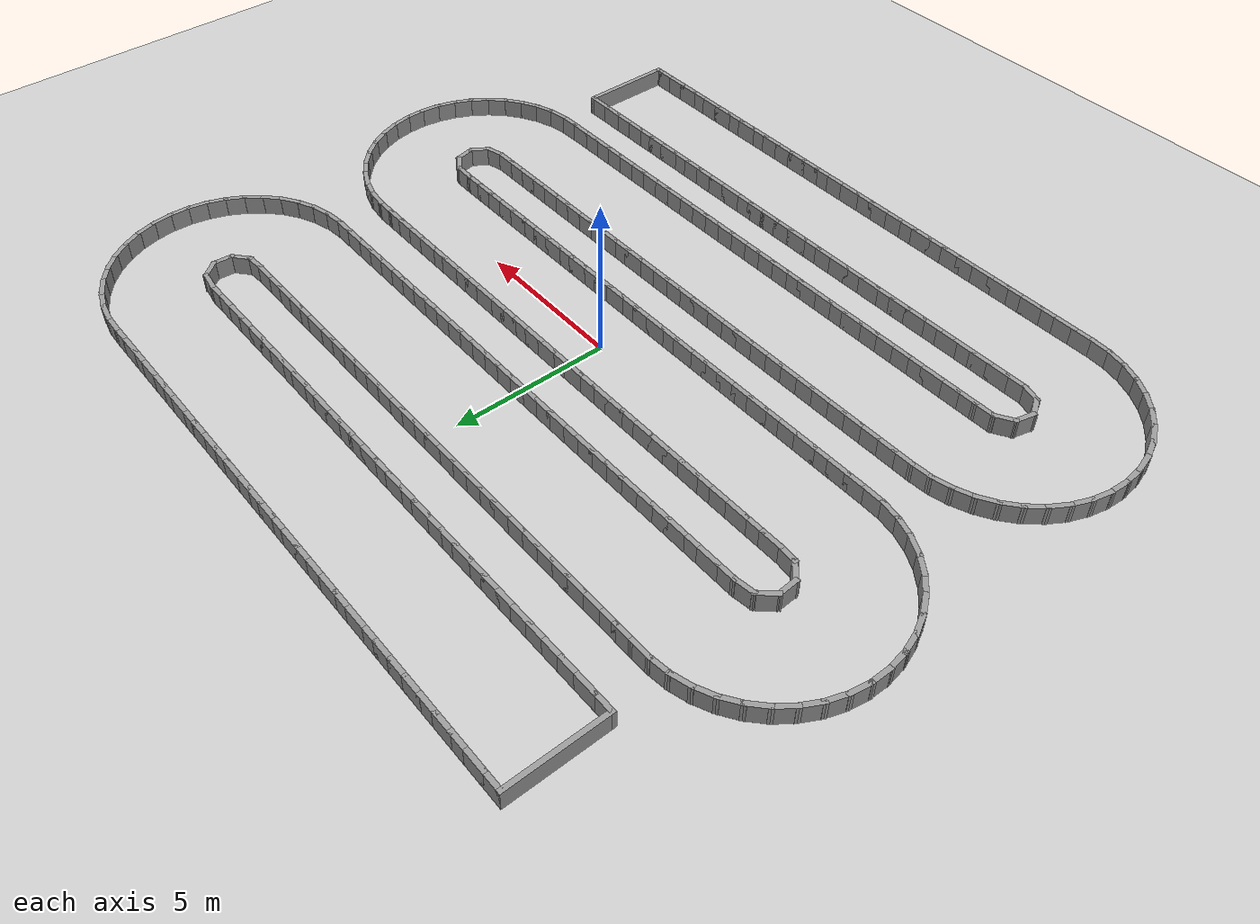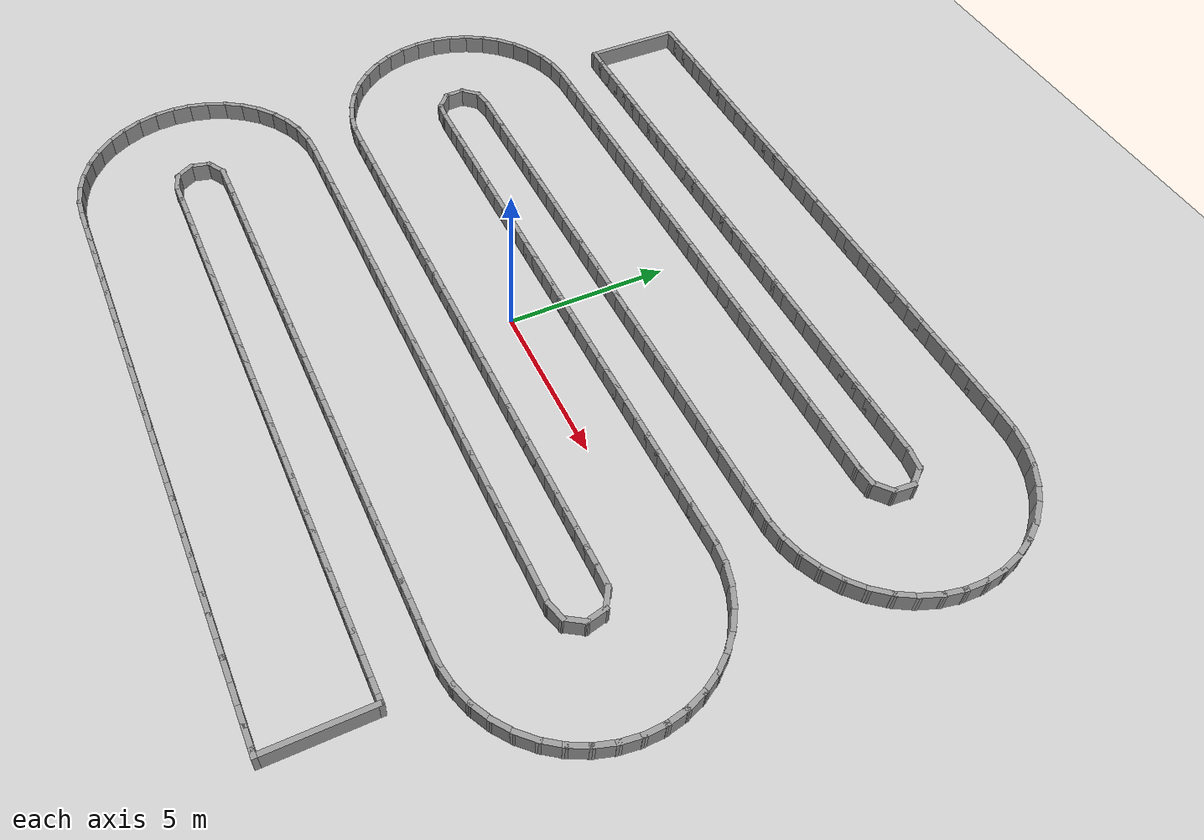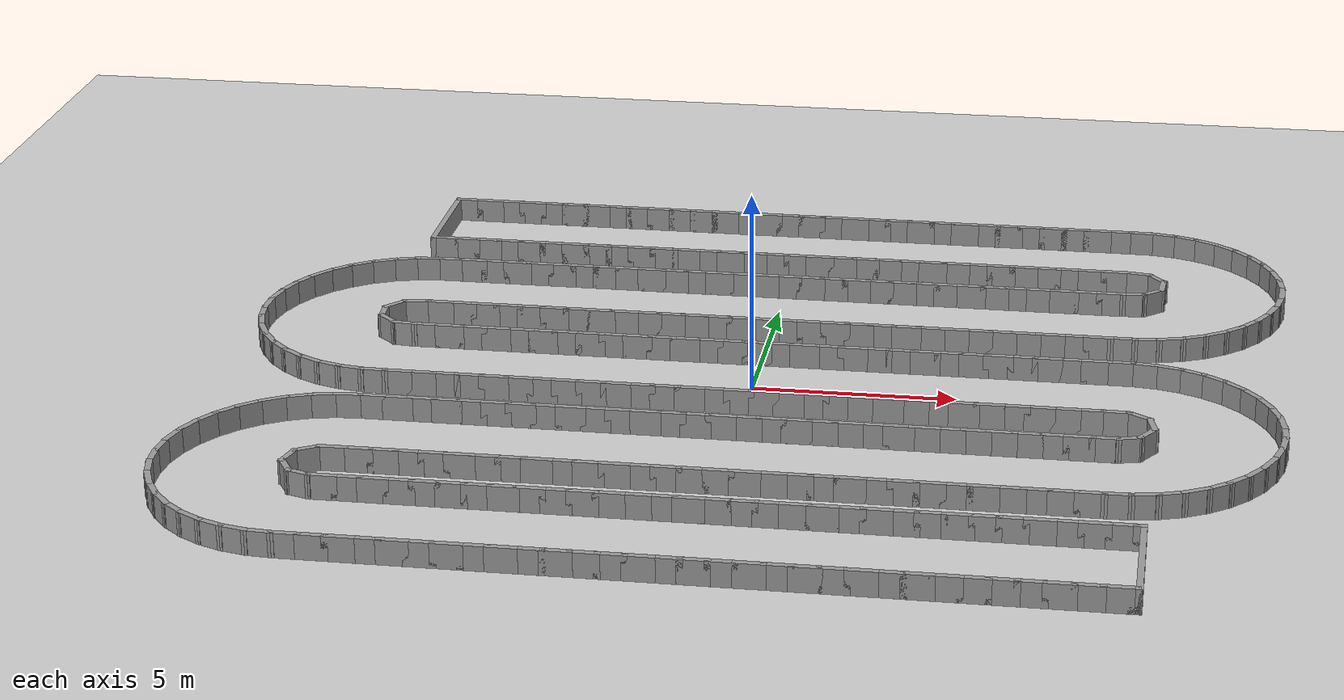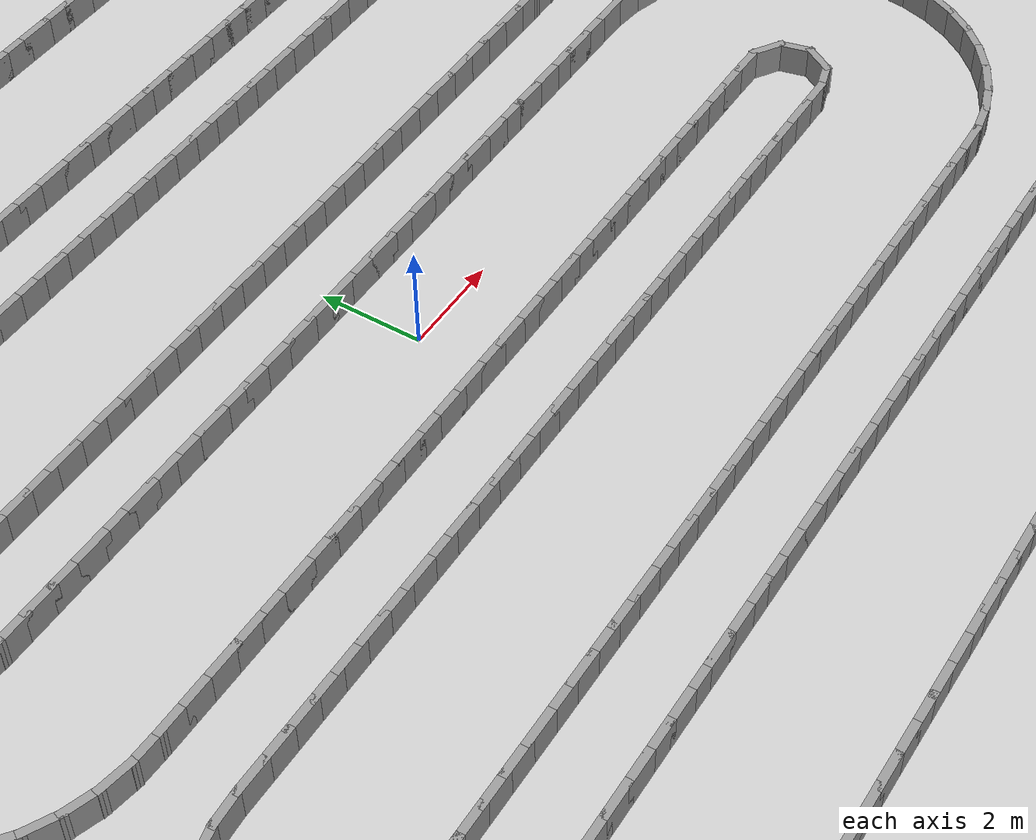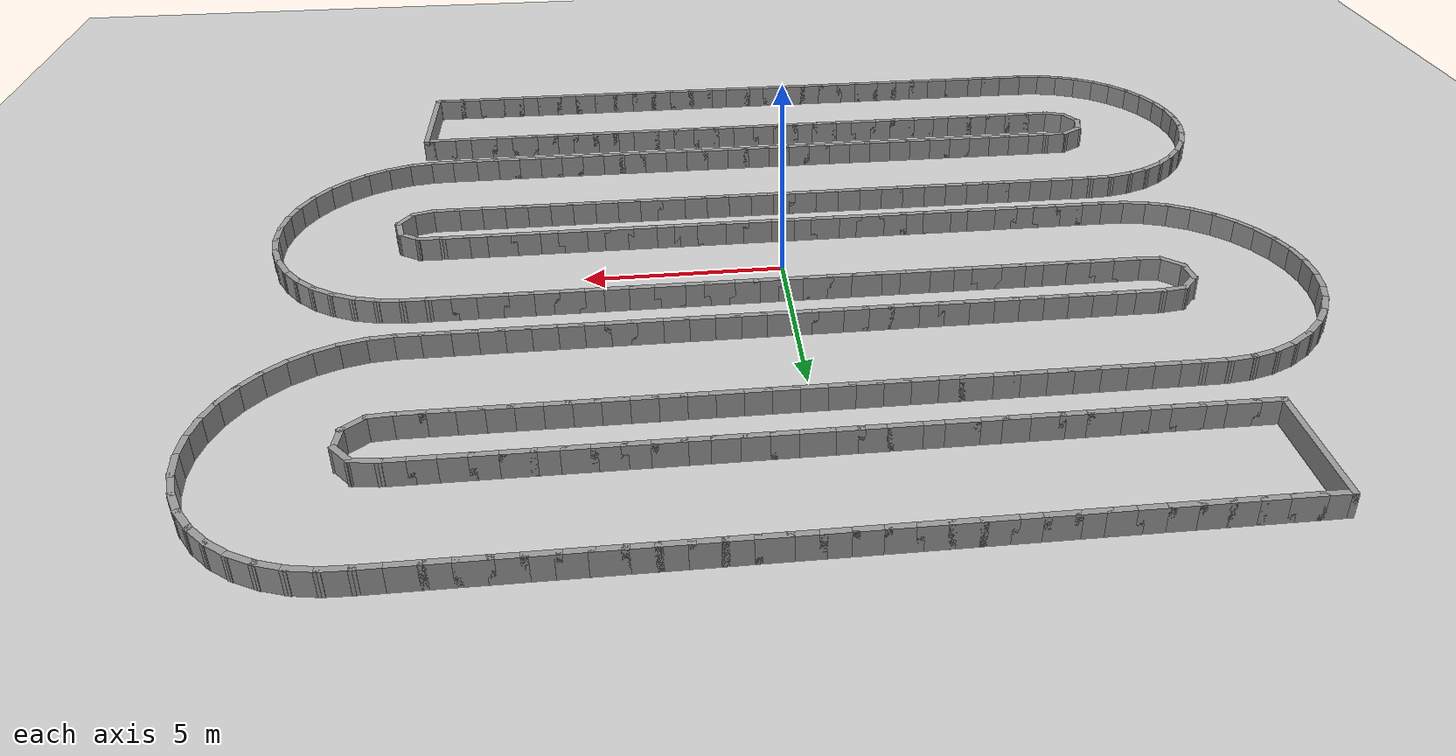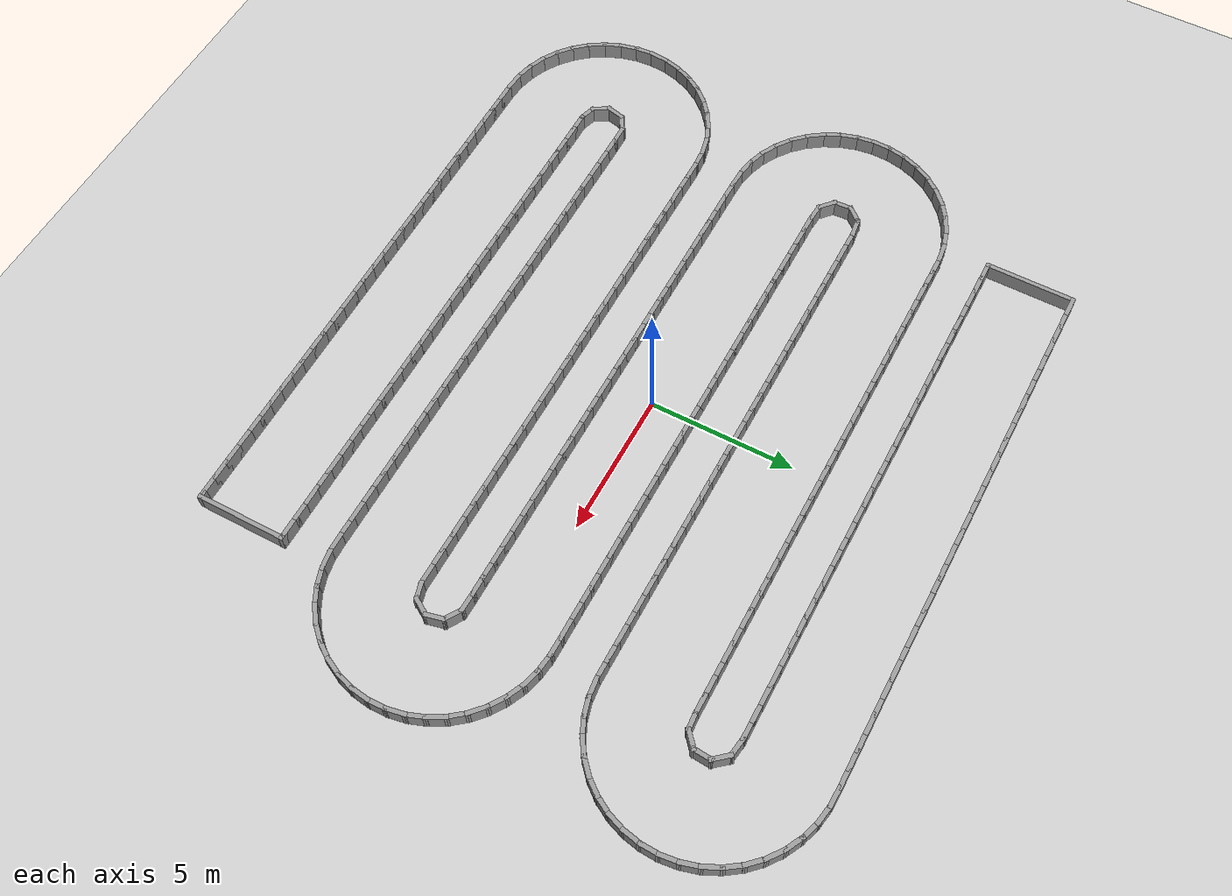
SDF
<?xml version="1.0" ?>
<sdf version='1.7'>
  <world name='default'>
    <plugin name='gazebo_ros_state' filename='libgazebo_ros_state.so'>
      <ros>
        <namespace>/</namespace>
      </ros>
      <update_rate>1000.0</update_rate>
    </plugin>

    <light name='sun' type='directional'>
      <cast_shadows>1</cast_shadows>
      <pose>0 0 10 0 -0 0</pose>
      <diffuse>0.8 0.8 0.8 1</diffuse>
      <specular>0.2 0.2 0.2 1</specular>
      <attenuation>
        <range>1000</range>
        <constant>0.9</constant>
        <linear>0.01</linear>
        <quadratic>0.001</quadratic>
      </attenuation>
      <direction>-0.5 0.1 -0.9</direction>
      <spot>
        <inner_angle>0</inner_angle>
        <outer_angle>0</outer_angle>
        <falloff>0</falloff>
      </spot>
    </light>
    <model name='ground_plane'>
      <static>1</static>
      <link name='link'>
        <collision name='collision'>
          <geometry>
            <plane>
              <normal>0 0 1</normal>
              <size>100 100</size>
            </plane>
          </geometry>
          <surface>
            <friction>
              <ode>
                <mu>100</mu>
                <mu2>50</mu2>
              </ode>
              <torsional>
                <ode/>
              </torsional>
            </friction>
            <contact>
              <ode/>
            </contact>
            <bounce/>
          </surface>
          <max_contacts>10</max_contacts>
        </collision>
        <visual name='visual'>
          <cast_shadows>0</cast_shadows>
          <geometry>
            <plane>
              <normal>0 0 1</normal>
              <size>100 100</size>
            </plane>
          </geometry>
          <material>
            <script>
              <uri>file://media/materials/scripts/gazebo.material</uri>
              <name>Gazebo/Grey</name>
            </script>
          </material>
        </visual>
        <self_collide>0</self_collide>
        <enable_wind>0</enable_wind>
        <kinematic>0</kinematic>
      </link>
    </model>
    <gravity>0 0 -9.8</gravity>
    <magnetic_field>6e-06 2.3e-05 -4.2e-05</magnetic_field>
    <atmosphere type='adiabatic'/>
    <physics type='ode'>
      <max_step_size>0.001</max_step_size>
      <real_time_factor>1</real_time_factor>
      <real_time_update_rate>1000</real_time_update_rate>
    </physics>
    <scene>
      <ambient>0.4 0.4 0.4 1</ambient>
      <background>0.7 0.7 0.7 1</background>
      <shadows>1</shadows>
    </scene>
    <audio>
      <device>default</device>
    </audio>
    <wind/>
    <spherical_coordinates>
      <surface_model>EARTH_WGS84</surface_model>
      <latitude_deg>0</latitude_deg>
      <longitude_deg>0</longitude_deg>
      <elevation>0</elevation>
      <heading_deg>0</heading_deg>
    </spherical_coordinates>
  <model name='rand_serp_02'>
    <pose>0 0 0 0 -0 0</pose>
    <link name='Wall_0'>
      <collision name='Wall_0_Collision'>
        <geometry><box><size>0.7500 0.1500 0.6000</size></box></geometry>
        <pose>0 0 0.3000 0 -0 0</pose>
      </collision>
      <visual name='Wall_0_Visual'>
        <pose>0 0 0.3000 0 -0 0</pose>
        <geometry><box><size>0.7500 0.1500 0.6000</size></box></geometry>
        <material>
          <script>
            <uri>file://media/materials/scripts/gazebo.material</uri>
            <name>Gazebo/Grey</name>
          </script>
          <ambient>1 1 1 1</ambient>
        </material>
      </visual>
      <pose>-9.4659 10.6147 0 0 -0 0.00000</pose>
    </link>
    <link name='Wall_1'>
      <collision name='Wall_1_Collision'>
        <geometry><box><size>0.7500 0.1500 0.6000</size></box></geometry>
        <pose>0 0 0.3000 0 -0 0</pose>
      </collision>
      <visual name='Wall_1_Visual'>
        <pose>0 0 0.3000 0 -0 0</pose>
        <geometry><box><size>0.7500 0.1500 0.6000</size></box></geometry>
        <material>
          <script>
            <uri>file://media/materials/scripts/gazebo.material</uri>
            <name>Gazebo/Grey</name>
          </script>
          <ambient>1 1 1 1</ambient>
        </material>
      </visual>
      <pose>-8.8659 10.6147 0 0 -0 0.00000</pose>
    </link>
    <link name='Wall_2'>
      <collision name='Wall_2_Collision'>
        <geometry><box><size>0.7500 0.1500 0.6000</size></box></geometry>
        <pose>0 0 0.3000 0 -0 0</pose>
      </collision>
      <visual name='Wall_2_Visual'>
        <pose>0 0 0.3000 0 -0 0</pose>
        <geometry><box><size>0.7500 0.1500 0.6000</size></box></geometry>
        <material>
          <script>
            <uri>file://media/materials/scripts/gazebo.material</uri>
            <name>Gazebo/Grey</name>
          </script>
          <ambient>1 1 1 1</ambient>
        </material>
      </visual>
      <pose>-8.2659 10.6147 0 0 -0 0.00000</pose>
    </link>
    <link name='Wall_3'>
      <collision name='Wall_3_Collision'>
        <geometry><box><size>0.7500 0.1500 0.6000</size></box></geometry>
        <pose>0 0 0.3000 0 -0 0</pose>
      </collision>
      <visual name='Wall_3_Visual'>
        <pose>0 0 0.3000 0 -0 0</pose>
        <geometry><box><size>0.7500 0.1500 0.6000</size></box></geometry>
        <material>
          <script>
            <uri>file://media/materials/scripts/gazebo.material</uri>
            <name>Gazebo/Grey</name>
          </script>
          <ambient>1 1 1 1</ambient>
        </material>
      </visual>
      <pose>-7.6659 10.6147 0 0 -0 0.00000</pose>
    </link>
    <link name='Wall_4'>
      <collision name='Wall_4_Collision'>
        <geometry><box><size>0.7500 0.1500 0.6000</size></box></geometry>
        <pose>0 0 0.3000 0 -0 0</pose>
      </collision>
      <visual name='Wall_4_Visual'>
        <pose>0 0 0.3000 0 -0 0</pose>
        <geometry><box><size>0.7500 0.1500 0.6000</size></box></geometry>
        <material>
          <script>
            <uri>file://media/materials/scripts/gazebo.material</uri>
            <name>Gazebo/Grey</name>
          </script>
          <ambient>1 1 1 1</ambient>
        </material>
      </visual>
      <pose>-7.0659 10.6147 0 0 -0 0.00000</pose>
    </link>
    <link name='Wall_5'>
      <collision name='Wall_5_Collision'>
        <geometry><box><size>0.7500 0.1500 0.6000</size></box></geometry>
        <pose>0 0 0.3000 0 -0 0</pose>
      </collision>
      <visual name='Wall_5_Visual'>
        <pose>0 0 0.3000 0 -0 0</pose>
        <geometry><box><size>0.7500 0.1500 0.6000</size></box></geometry>
        <material>
          <script>
            <uri>file://media/materials/scripts/gazebo.material</uri>
            <name>Gazebo/Grey</name>
          </script>
          <ambient>1 1 1 1</ambient>
        </material>
      </visual>
      <pose>-6.4659 10.6147 0 0 -0 0.00000</pose>
    </link>
    <link name='Wall_6'>
      <collision name='Wall_6_Collision'>
        <geometry><box><size>0.7500 0.1500 0.6000</size></box></geometry>
        <pose>0 0 0.3000 0 -0 0</pose>
      </collision>
      <visual name='Wall_6_Visual'>
        <pose>0 0 0.3000 0 -0 0</pose>
        <geometry><box><size>0.7500 0.1500 0.6000</size></box></geometry>
        <material>
          <script>
            <uri>file://media/materials/scripts/gazebo.material</uri>
            <name>Gazebo/Grey</name>
          </script>
          <ambient>1 1 1 1</ambient>
        </material>
      </visual>
      <pose>-5.8659 10.6147 0 0 -0 0.00000</pose>
    </link>
    <link name='Wall_7'>
      <collision name='Wall_7_Collision'>
        <geometry><box><size>0.7500 0.1500 0.6000</size></box></geometry>
        <pose>0 0 0.3000 0 -0 0</pose>
      </collision>
      <visual name='Wall_7_Visual'>
        <pose>0 0 0.3000 0 -0 0</pose>
        <geometry><box><size>0.7500 0.1500 0.6000</size></box></geometry>
        <material>
          <script>
            <uri>file://media/materials/scripts/gazebo.material</uri>
            <name>Gazebo/Grey</name>
          </script>
          <ambient>1 1 1 1</ambient>
        </material>
      </visual>
      <pose>-5.2659 10.6147 0 0 -0 0.00000</pose>
    </link>
    <link name='Wall_8'>
      <collision name='Wall_8_Collision'>
        <geometry><box><size>0.7500 0.1500 0.6000</size></box></geometry>
        <pose>0 0 0.3000 0 -0 0</pose>
      </collision>
      <visual name='Wall_8_Visual'>
        <pose>0 0 0.3000 0 -0 0</pose>
        <geometry><box><size>0.7500 0.1500 0.6000</size></box></geometry>
        <material>
          <script>
            <uri>file://media/materials/scripts/gazebo.material</uri>
            <name>Gazebo/Grey</name>
          </script>
          <ambient>1 1 1 1</ambient>
        </material>
      </visual>
      <pose>-4.6659 10.6147 0 0 -0 0.00000</pose>
    </link>
    <link name='Wall_9'>
      <collision name='Wall_9_Collision'>
        <geometry><box><size>0.7500 0.1500 0.6000</size></box></geometry>
        <pose>0 0 0.3000 0 -0 0</pose>
      </collision>
      <visual name='Wall_9_Visual'>
        <pose>0 0 0.3000 0 -0 0</pose>
        <geometry><box><size>0.7500 0.1500 0.6000</size></box></geometry>
        <material>
          <script>
            <uri>file://media/materials/scripts/gazebo.material</uri>
            <name>Gazebo/Grey</name>
          </script>
          <ambient>1 1 1 1</ambient>
        </material>
      </visual>
      <pose>-4.0659 10.6147 0 0 -0 0.00000</pose>
    </link>
    <link name='Wall_10'>
      <collision name='Wall_10_Collision'>
        <geometry><box><size>0.7500 0.1500 0.6000</size></box></geometry>
        <pose>0 0 0.3000 0 -0 0</pose>
      </collision>
      <visual name='Wall_10_Visual'>
        <pose>0 0 0.3000 0 -0 0</pose>
        <geometry><box><size>0.7500 0.1500 0.6000</size></box></geometry>
        <material>
          <script>
            <uri>file://media/materials/scripts/gazebo.material</uri>
            <name>Gazebo/Grey</name>
          </script>
          <ambient>1 1 1 1</ambient>
        </material>
      </visual>
      <pose>-3.4659 10.6147 0 0 -0 0.00000</pose>
    </link>
    <link name='Wall_11'>
      <collision name='Wall_11_Collision'>
        <geometry><box><size>0.7500 0.1500 0.6000</size></box></geometry>
        <pose>0 0 0.3000 0 -0 0</pose>
      </collision>
      <visual name='Wall_11_Visual'>
        <pose>0 0 0.3000 0 -0 0</pose>
        <geometry><box><size>0.7500 0.1500 0.6000</size></box></geometry>
        <material>
          <script>
            <uri>file://media/materials/scripts/gazebo.material</uri>
            <name>Gazebo/Grey</name>
          </script>
          <ambient>1 1 1 1</ambient>
        </material>
      </visual>
      <pose>-2.8659 10.6147 0 0 -0 0.00000</pose>
    </link>
    <link name='Wall_12'>
      <collision name='Wall_12_Collision'>
        <geometry><box><size>0.7500 0.1500 0.6000</size></box></geometry>
        <pose>0 0 0.3000 0 -0 0</pose>
      </collision>
      <visual name='Wall_12_Visual'>
        <pose>0 0 0.3000 0 -0 0</pose>
        <geometry><box><size>0.7500 0.1500 0.6000</size></box></geometry>
        <material>
          <script>
            <uri>file://media/materials/scripts/gazebo.material</uri>
            <name>Gazebo/Grey</name>
          </script>
          <ambient>1 1 1 1</ambient>
        </material>
      </visual>
      <pose>-2.2659 10.6147 0 0 -0 0.00000</pose>
    </link>
    <link name='Wall_13'>
      <collision name='Wall_13_Collision'>
        <geometry><box><size>0.7500 0.1500 0.6000</size></box></geometry>
        <pose>0 0 0.3000 0 -0 0</pose>
      </collision>
      <visual name='Wall_13_Visual'>
        <pose>0 0 0.3000 0 -0 0</pose>
        <geometry><box><size>0.7500 0.1500 0.6000</size></box></geometry>
        <material>
          <script>
            <uri>file://media/materials/scripts/gazebo.material</uri>
            <name>Gazebo/Grey</name>
          </script>
          <ambient>1 1 1 1</ambient>
        </material>
      </visual>
      <pose>-1.6659 10.6147 0 0 -0 0.00000</pose>
    </link>
    <link name='Wall_14'>
      <collision name='Wall_14_Collision'>
        <geometry><box><size>0.7500 0.1500 0.6000</size></box></geometry>
        <pose>0 0 0.3000 0 -0 0</pose>
      </collision>
      <visual name='Wall_14_Visual'>
        <pose>0 0 0.3000 0 -0 0</pose>
        <geometry><box><size>0.7500 0.1500 0.6000</size></box></geometry>
        <material>
          <script>
            <uri>file://media/materials/scripts/gazebo.material</uri>
            <name>Gazebo/Grey</name>
          </script>
          <ambient>1 1 1 1</ambient>
        </material>
      </visual>
      <pose>-1.0659 10.6147 0 0 -0 0.00000</pose>
    </link>
    <link name='Wall_15'>
      <collision name='Wall_15_Collision'>
        <geometry><box><size>0.7500 0.1500 0.6000</size></box></geometry>
        <pose>0 0 0.3000 0 -0 0</pose>
      </collision>
      <visual name='Wall_15_Visual'>
        <pose>0 0 0.3000 0 -0 0</pose>
        <geometry><box><size>0.7500 0.1500 0.6000</size></box></geometry>
        <material>
          <script>
            <uri>file://media/materials/scripts/gazebo.material</uri>
            <name>Gazebo/Grey</name>
          </script>
          <ambient>1 1 1 1</ambient>
        </material>
      </visual>
      <pose>-0.4659 10.6147 0 0 -0 0.00000</pose>
    </link>
    <link name='Wall_16'>
      <collision name='Wall_16_Collision'>
        <geometry><box><size>0.7500 0.1500 0.6000</size></box></geometry>
        <pose>0 0 0.3000 0 -0 0</pose>
      </collision>
      <visual name='Wall_16_Visual'>
        <pose>0 0 0.3000 0 -0 0</pose>
        <geometry><box><size>0.7500 0.1500 0.6000</size></box></geometry>
        <material>
          <script>
            <uri>file://media/materials/scripts/gazebo.material</uri>
            <name>Gazebo/Grey</name>
          </script>
          <ambient>1 1 1 1</ambient>
        </material>
      </visual>
      <pose>0.1341 10.6147 0 0 -0 0.00000</pose>
    </link>
    <link name='Wall_17'>
      <collision name='Wall_17_Collision'>
        <geometry><box><size>0.7500 0.1500 0.6000</size></box></geometry>
        <pose>0 0 0.3000 0 -0 0</pose>
      </collision>
      <visual name='Wall_17_Visual'>
        <pose>0 0 0.3000 0 -0 0</pose>
        <geometry><box><size>0.7500 0.1500 0.6000</size></box></geometry>
        <material>
          <script>
            <uri>file://media/materials/scripts/gazebo.material</uri>
            <name>Gazebo/Grey</name>
          </script>
          <ambient>1 1 1 1</ambient>
        </material>
      </visual>
      <pose>0.7341 10.6147 0 0 -0 0.00000</pose>
    </link>
    <link name='Wall_18'>
      <collision name='Wall_18_Collision'>
        <geometry><box><size>0.7500 0.1500 0.6000</size></box></geometry>
        <pose>0 0 0.3000 0 -0 0</pose>
      </collision>
      <visual name='Wall_18_Visual'>
        <pose>0 0 0.3000 0 -0 0</pose>
        <geometry><box><size>0.7500 0.1500 0.6000</size></box></geometry>
        <material>
          <script>
            <uri>file://media/materials/scripts/gazebo.material</uri>
            <name>Gazebo/Grey</name>
          </script>
          <ambient>1 1 1 1</ambient>
        </material>
      </visual>
      <pose>1.3341 10.6147 0 0 -0 0.00000</pose>
    </link>
    <link name='Wall_19'>
      <collision name='Wall_19_Collision'>
        <geometry><box><size>0.7500 0.1500 0.6000</size></box></geometry>
        <pose>0 0 0.3000 0 -0 0</pose>
      </collision>
      <visual name='Wall_19_Visual'>
        <pose>0 0 0.3000 0 -0 0</pose>
        <geometry><box><size>0.7500 0.1500 0.6000</size></box></geometry>
        <material>
          <script>
            <uri>file://media/materials/scripts/gazebo.material</uri>
            <name>Gazebo/Grey</name>
          </script>
          <ambient>1 1 1 1</ambient>
        </material>
      </visual>
      <pose>1.9341 10.6147 0 0 -0 0.00000</pose>
    </link>
    <link name='Wall_20'>
      <collision name='Wall_20_Collision'>
        <geometry><box><size>0.7500 0.1500 0.6000</size></box></geometry>
        <pose>0 0 0.3000 0 -0 0</pose>
      </collision>
      <visual name='Wall_20_Visual'>
        <pose>0 0 0.3000 0 -0 0</pose>
        <geometry><box><size>0.7500 0.1500 0.6000</size></box></geometry>
        <material>
          <script>
            <uri>file://media/materials/scripts/gazebo.material</uri>
            <name>Gazebo/Grey</name>
          </script>
          <ambient>1 1 1 1</ambient>
        </material>
      </visual>
      <pose>2.5341 10.6147 0 0 -0 0.00000</pose>
    </link>
    <link name='Wall_21'>
      <collision name='Wall_21_Collision'>
        <geometry><box><size>0.7500 0.1500 0.6000</size></box></geometry>
        <pose>0 0 0.3000 0 -0 0</pose>
      </collision>
      <visual name='Wall_21_Visual'>
        <pose>0 0 0.3000 0 -0 0</pose>
        <geometry><box><size>0.7500 0.1500 0.6000</size></box></geometry>
        <material>
          <script>
            <uri>file://media/materials/scripts/gazebo.material</uri>
            <name>Gazebo/Grey</name>
          </script>
          <ambient>1 1 1 1</ambient>
        </material>
      </visual>
      <pose>3.1341 10.6147 0 0 -0 0.00000</pose>
    </link>
    <link name='Wall_22'>
      <collision name='Wall_22_Collision'>
        <geometry><box><size>0.7500 0.1500 0.6000</size></box></geometry>
        <pose>0 0 0.3000 0 -0 0</pose>
      </collision>
      <visual name='Wall_22_Visual'>
        <pose>0 0 0.3000 0 -0 0</pose>
        <geometry><box><size>0.7500 0.1500 0.6000</size></box></geometry>
        <material>
          <script>
            <uri>file://media/materials/scripts/gazebo.material</uri>
            <name>Gazebo/Grey</name>
          </script>
          <ambient>1 1 1 1</ambient>
        </material>
      </visual>
      <pose>3.7341 10.6147 0 0 -0 0.00000</pose>
    </link>
    <link name='Wall_23'>
      <collision name='Wall_23_Collision'>
        <geometry><box><size>0.7500 0.1500 0.6000</size></box></geometry>
        <pose>0 0 0.3000 0 -0 0</pose>
      </collision>
      <visual name='Wall_23_Visual'>
        <pose>0 0 0.3000 0 -0 0</pose>
        <geometry><box><size>0.7500 0.1500 0.6000</size></box></geometry>
        <material>
          <script>
            <uri>file://media/materials/scripts/gazebo.material</uri>
            <name>Gazebo/Grey</name>
          </script>
          <ambient>1 1 1 1</ambient>
        </material>
      </visual>
      <pose>4.3341 10.6147 0 0 -0 0.00000</pose>
    </link>
    <link name='Wall_24'>
      <collision name='Wall_24_Collision'>
        <geometry><box><size>0.7500 0.1500 0.6000</size></box></geometry>
        <pose>0 0 0.3000 0 -0 0</pose>
      </collision>
      <visual name='Wall_24_Visual'>
        <pose>0 0 0.3000 0 -0 0</pose>
        <geometry><box><size>0.7500 0.1500 0.6000</size></box></geometry>
        <material>
          <script>
            <uri>file://media/materials/scripts/gazebo.material</uri>
            <name>Gazebo/Grey</name>
          </script>
          <ambient>1 1 1 1</ambient>
        </material>
      </visual>
      <pose>4.9341 10.6147 0 0 -0 0.00000</pose>
    </link>
    <link name='Wall_25'>
      <collision name='Wall_25_Collision'>
        <geometry><box><size>0.7500 0.1500 0.6000</size></box></geometry>
        <pose>0 0 0.3000 0 -0 0</pose>
      </collision>
      <visual name='Wall_25_Visual'>
        <pose>0 0 0.3000 0 -0 0</pose>
        <geometry><box><size>0.7500 0.1500 0.6000</size></box></geometry>
        <material>
          <script>
            <uri>file://media/materials/scripts/gazebo.material</uri>
            <name>Gazebo/Grey</name>
          </script>
          <ambient>1 1 1 1</ambient>
        </material>
      </visual>
      <pose>5.5341 10.6147 0 0 -0 0.00000</pose>
    </link>
    <link name='Wall_26'>
      <collision name='Wall_26_Collision'>
        <geometry><box><size>0.7500 0.1500 0.6000</size></box></geometry>
        <pose>0 0 0.3000 0 -0 0</pose>
      </collision>
      <visual name='Wall_26_Visual'>
        <pose>0 0 0.3000 0 -0 0</pose>
        <geometry><box><size>0.7500 0.1500 0.6000</size></box></geometry>
        <material>
          <script>
            <uri>file://media/materials/scripts/gazebo.material</uri>
            <name>Gazebo/Grey</name>
          </script>
          <ambient>1 1 1 1</ambient>
        </material>
      </visual>
      <pose>6.1341 10.6147 0 0 -0 0.00000</pose>
    </link>
    <link name='Wall_27'>
      <collision name='Wall_27_Collision'>
        <geometry><box><size>0.7500 0.1500 0.6000</size></box></geometry>
        <pose>0 0 0.3000 0 -0 0</pose>
      </collision>
      <visual name='Wall_27_Visual'>
        <pose>0 0 0.3000 0 -0 0</pose>
        <geometry><box><size>0.7500 0.1500 0.6000</size></box></geometry>
        <material>
          <script>
            <uri>file://media/materials/scripts/gazebo.material</uri>
            <name>Gazebo/Grey</name>
          </script>
          <ambient>1 1 1 1</ambient>
        </material>
      </visual>
      <pose>6.7341 10.6147 0 0 -0 0.00000</pose>
    </link>
    <link name='Wall_28'>
      <collision name='Wall_28_Collision'>
        <geometry><box><size>0.7500 0.1500 0.6000</size></box></geometry>
        <pose>0 0 0.3000 0 -0 0</pose>
      </collision>
      <visual name='Wall_28_Visual'>
        <pose>0 0 0.3000 0 -0 0</pose>
        <geometry><box><size>0.7500 0.1500 0.6000</size></box></geometry>
        <material>
          <script>
            <uri>file://media/materials/scripts/gazebo.material</uri>
            <name>Gazebo/Grey</name>
          </script>
          <ambient>1 1 1 1</ambient>
        </material>
      </visual>
      <pose>7.3341 10.6147 0 0 -0 0.00000</pose>
    </link>
    <link name='Wall_29'>
      <collision name='Wall_29_Collision'>
        <geometry><box><size>0.7500 0.1500 0.6000</size></box></geometry>
        <pose>0 0 0.3000 0 -0 0</pose>
      </collision>
      <visual name='Wall_29_Visual'>
        <pose>0 0 0.3000 0 -0 0</pose>
        <geometry><box><size>0.7500 0.1500 0.6000</size></box></geometry>
        <material>
          <script>
            <uri>file://media/materials/scripts/gazebo.material</uri>
            <name>Gazebo/Grey</name>
          </script>
          <ambient>1 1 1 1</ambient>
        </material>
      </visual>
      <pose>7.9341 10.6147 0 0 -0 0.00000</pose>
    </link>
    <link name='Wall_30'>
      <collision name='Wall_30_Collision'>
        <geometry><box><size>0.7500 0.1500 0.6000</size></box></geometry>
        <pose>0 0 0.3000 0 -0 0</pose>
      </collision>
      <visual name='Wall_30_Visual'>
        <pose>0 0 0.3000 0 -0 0</pose>
        <geometry><box><size>0.7500 0.1500 0.6000</size></box></geometry>
        <material>
          <script>
            <uri>file://media/materials/scripts/gazebo.material</uri>
            <name>Gazebo/Grey</name>
          </script>
          <ambient>1 1 1 1</ambient>
        </material>
      </visual>
      <pose>8.5341 10.6147 0 0 -0 0.00000</pose>
    </link>
    <link name='Wall_31'>
      <collision name='Wall_31_Collision'>
        <geometry><box><size>0.7497 0.1500 0.6000</size></box></geometry>
        <pose>0 0 0.3000 0 -0 0</pose>
      </collision>
      <visual name='Wall_31_Visual'>
        <pose>0 0 0.3000 0 -0 0</pose>
        <geometry><box><size>0.7497 0.1500 0.6000</size></box></geometry>
        <material>
          <script>
            <uri>file://media/materials/scripts/gazebo.material</uri>
            <name>Gazebo/Grey</name>
          </script>
          <ambient>1 1 1 1</ambient>
        </material>
      </visual>
      <pose>9.1338 10.6053 0 0 -0 -0.03110</pose>
    </link>
    <link name='Wall_32'>
      <collision name='Wall_32_Collision'>
        <geometry><box><size>0.7493 0.1500 0.6000</size></box></geometry>
        <pose>0 0 0.3000 0 -0 0</pose>
      </collision>
      <visual name='Wall_32_Visual'>
        <pose>0 0 0.3000 0 -0 0</pose>
        <geometry><box><size>0.7493 0.1500 0.6000</size></box></geometry>
        <material>
          <script>
            <uri>file://media/materials/scripts/gazebo.material</uri>
            <name>Gazebo/Grey</name>
          </script>
          <ambient>1 1 1 1</ambient>
        </material>
      </visual>
      <pose>9.7285 10.5434 0 0 -0 -0.17663</pose>
    </link>
    <link name='Wall_33'>
      <collision name='Wall_33_Collision'>
        <geometry><box><size>0.7493 0.1500 0.6000</size></box></geometry>
        <pose>0 0 0.3000 0 -0 0</pose>
      </collision>
      <visual name='Wall_33_Visual'>
        <pose>0 0 0.3000 0 -0 0</pose>
        <geometry><box><size>0.7493 0.1500 0.6000</size></box></geometry>
        <material>
          <script>
            <uri>file://media/materials/scripts/gazebo.material</uri>
            <name>Gazebo/Grey</name>
          </script>
          <ambient>1 1 1 1</ambient>
        </material>
      </visual>
      <pose>10.3064 10.3921 0 0 -0 -0.33521</pose>
    </link>
    <link name='Wall_34'>
      <collision name='Wall_34_Collision'>
        <geometry><box><size>0.7493 0.1500 0.6000</size></box></geometry>
        <pose>0 0 0.3000 0 -0 0</pose>
      </collision>
      <visual name='Wall_34_Visual'>
        <pose>0 0 0.3000 0 -0 0</pose>
        <geometry><box><size>0.7493 0.1500 0.6000</size></box></geometry>
        <material>
          <script>
            <uri>file://media/materials/scripts/gazebo.material</uri>
            <name>Gazebo/Grey</name>
          </script>
          <ambient>1 1 1 1</ambient>
        </material>
      </visual>
      <pose>10.8533 10.1515 0 0 -0 -0.49380</pose>
    </link>
    <link name='Wall_35'>
      <collision name='Wall_35_Collision'>
        <geometry><box><size>0.7493 0.1500 0.6000</size></box></geometry>
        <pose>0 0 0.3000 0 -0 0</pose>
      </collision>
      <visual name='Wall_35_Visual'>
        <pose>0 0 0.3000 0 -0 0</pose>
        <geometry><box><size>0.7493 0.1500 0.6000</size></box></geometry>
        <material>
          <script>
            <uri>file://media/materials/scripts/gazebo.material</uri>
            <name>Gazebo/Grey</name>
          </script>
          <ambient>1 1 1 1</ambient>
        </material>
      </visual>
      <pose>11.3552 9.8276 0 0 -0 -0.65239</pose>
    </link>
    <link name='Wall_36'>
      <collision name='Wall_36_Collision'>
        <geometry><box><size>0.7493 0.1500 0.6000</size></box></geometry>
        <pose>0 0 0.3000 0 -0 0</pose>
      </collision>
      <visual name='Wall_36_Visual'>
        <pose>0 0 0.3000 0 -0 0</pose>
        <geometry><box><size>0.7493 0.1500 0.6000</size></box></geometry>
        <material>
          <script>
            <uri>file://media/materials/scripts/gazebo.material</uri>
            <name>Gazebo/Grey</name>
          </script>
          <ambient>1 1 1 1</ambient>
        </material>
      </visual>
      <pose>11.7997 9.4284 0 0 -0 -0.81098</pose>
    </link>
    <link name='Wall_37'>
      <collision name='Wall_37_Collision'>
        <geometry><box><size>0.7493 0.1500 0.6000</size></box></geometry>
        <pose>0 0 0.3000 0 -0 0</pose>
      </collision>
      <visual name='Wall_37_Visual'>
        <pose>0 0 0.3000 0 -0 0</pose>
        <geometry><box><size>0.7493 0.1500 0.6000</size></box></geometry>
        <material>
          <script>
            <uri>file://media/materials/scripts/gazebo.material</uri>
            <name>Gazebo/Grey</name>
          </script>
          <ambient>1 1 1 1</ambient>
        </material>
      </visual>
      <pose>12.1756 8.9641 0 0 -0 -0.96957</pose>
    </link>
    <link name='Wall_38'>
      <collision name='Wall_38_Collision'>
        <geometry><box><size>0.7493 0.1500 0.6000</size></box></geometry>
        <pose>0 0 0.3000 0 -0 0</pose>
      </collision>
      <visual name='Wall_38_Visual'>
        <pose>0 0 0.3000 0 -0 0</pose>
        <geometry><box><size>0.7493 0.1500 0.6000</size></box></geometry>
        <material>
          <script>
            <uri>file://media/materials/scripts/gazebo.material</uri>
            <name>Gazebo/Grey</name>
          </script>
          <ambient>1 1 1 1</ambient>
        </material>
      </visual>
      <pose>12.4735 8.4462 0 0 -0 -1.12815</pose>
    </link>
    <link name='Wall_39'>
      <collision name='Wall_39_Collision'>
        <geometry><box><size>0.7493 0.1500 0.6000</size></box></geometry>
        <pose>0 0 0.3000 0 -0 0</pose>
      </collision>
      <visual name='Wall_39_Visual'>
        <pose>0 0 0.3000 0 -0 0</pose>
        <geometry><box><size>0.7493 0.1500 0.6000</size></box></geometry>
        <material>
          <script>
            <uri>file://media/materials/scripts/gazebo.material</uri>
            <name>Gazebo/Grey</name>
          </script>
          <ambient>1 1 1 1</ambient>
        </material>
      </visual>
      <pose>12.6858 7.8878 0 0 -0 -1.28674</pose>
    </link>
    <link name='Wall_40'>
      <collision name='Wall_40_Collision'>
        <geometry><box><size>0.7493 0.1500 0.6000</size></box></geometry>
        <pose>0 0 0.3000 0 -0 0</pose>
      </collision>
      <visual name='Wall_40_Visual'>
        <pose>0 0 0.3000 0 -0 0</pose>
        <geometry><box><size>0.7493 0.1500 0.6000</size></box></geometry>
        <material>
          <script>
            <uri>file://media/materials/scripts/gazebo.material</uri>
            <name>Gazebo/Grey</name>
          </script>
          <ambient>1 1 1 1</ambient>
        </material>
      </visual>
      <pose>12.8073 7.3029 0 0 -0 -1.44533</pose>
    </link>
    <link name='Wall_41'>
      <collision name='Wall_41_Collision'>
        <geometry><box><size>0.7493 0.1500 0.6000</size></box></geometry>
        <pose>0 0 0.3000 0 -0 0</pose>
      </collision>
      <visual name='Wall_41_Visual'>
        <pose>0 0 0.3000 0 -0 0</pose>
        <geometry><box><size>0.7493 0.1500 0.6000</size></box></geometry>
        <material>
          <script>
            <uri>file://media/materials/scripts/gazebo.material</uri>
            <name>Gazebo/Grey</name>
          </script>
          <ambient>1 1 1 1</ambient>
        </material>
      </visual>
      <pose>12.8348 6.7061 0 0 -0 -1.60392</pose>
    </link>
    <link name='Wall_42'>
      <collision name='Wall_42_Collision'>
        <geometry><box><size>0.7493 0.1500 0.6000</size></box></geometry>
        <pose>0 0 0.3000 0 -0 0</pose>
      </collision>
      <visual name='Wall_42_Visual'>
        <pose>0 0 0.3000 0 -0 0</pose>
        <geometry><box><size>0.7493 0.1500 0.6000</size></box></geometry>
        <material>
          <script>
            <uri>file://media/materials/scripts/gazebo.material</uri>
            <name>Gazebo/Grey</name>
          </script>
          <ambient>1 1 1 1</ambient>
        </material>
      </visual>
      <pose>12.7678 6.1124 0 0 -0 -1.76251</pose>
    </link>
    <link name='Wall_43'>
      <collision name='Wall_43_Collision'>
        <geometry><box><size>0.7493 0.1500 0.6000</size></box></geometry>
        <pose>0 0 0.3000 0 -0 0</pose>
      </collision>
      <visual name='Wall_43_Visual'>
        <pose>0 0 0.3000 0 -0 0</pose>
        <geometry><box><size>0.7493 0.1500 0.6000</size></box></geometry>
        <material>
          <script>
            <uri>file://media/materials/scripts/gazebo.material</uri>
            <name>Gazebo/Grey</name>
          </script>
          <ambient>1 1 1 1</ambient>
        </material>
      </visual>
      <pose>12.6079 5.5368 0 0 -0 -1.92110</pose>
    </link>
    <link name='Wall_44'>
      <collision name='Wall_44_Collision'>
        <geometry><box><size>0.7493 0.1500 0.6000</size></box></geometry>
        <pose>0 0 0.3000 0 -0 0</pose>
      </collision>
      <visual name='Wall_44_Visual'>
        <pose>0 0 0.3000 0 -0 0</pose>
        <geometry><box><size>0.7493 0.1500 0.6000</size></box></geometry>
        <material>
          <script>
            <uri>file://media/materials/scripts/gazebo.material</uri>
            <name>Gazebo/Grey</name>
          </script>
          <ambient>1 1 1 1</ambient>
        </material>
      </visual>
      <pose>12.3591 4.9937 0 0 -0 -2.07968</pose>
    </link>
    <link name='Wall_45'>
      <collision name='Wall_45_Collision'>
        <geometry><box><size>0.7493 0.1500 0.6000</size></box></geometry>
        <pose>0 0 0.3000 0 -0 0</pose>
      </collision>
      <visual name='Wall_45_Visual'>
        <pose>0 0 0.3000 0 -0 0</pose>
        <geometry><box><size>0.7493 0.1500 0.6000</size></box></geometry>
        <material>
          <script>
            <uri>file://media/materials/scripts/gazebo.material</uri>
            <name>Gazebo/Grey</name>
          </script>
          <ambient>1 1 1 1</ambient>
        </material>
      </visual>
      <pose>12.0276 4.4967 0 0 -0 -2.23827</pose>
    </link>
    <link name='Wall_46'>
      <collision name='Wall_46_Collision'>
        <geometry><box><size>0.7493 0.1500 0.6000</size></box></geometry>
        <pose>0 0 0.3000 0 -0 0</pose>
      </collision>
      <visual name='Wall_46_Visual'>
        <pose>0 0 0.3000 0 -0 0</pose>
        <geometry><box><size>0.7493 0.1500 0.6000</size></box></geometry>
        <material>
          <script>
            <uri>file://media/materials/scripts/gazebo.material</uri>
            <name>Gazebo/Grey</name>
          </script>
          <ambient>1 1 1 1</ambient>
        </material>
      </visual>
      <pose>11.6218 4.0582 0 0 -0 -2.39686</pose>
    </link>
    <link name='Wall_47'>
      <collision name='Wall_47_Collision'>
        <geometry><box><size>0.7493 0.1500 0.6000</size></box></geometry>
        <pose>0 0 0.3000 0 -0 0</pose>
      </collision>
      <visual name='Wall_47_Visual'>
        <pose>0 0 0.3000 0 -0 0</pose>
        <geometry><box><size>0.7493 0.1500 0.6000</size></box></geometry>
        <material>
          <script>
            <uri>file://media/materials/scripts/gazebo.material</uri>
            <name>Gazebo/Grey</name>
          </script>
          <ambient>1 1 1 1</ambient>
        </material>
      </visual>
      <pose>11.1518 3.6893 0 0 -0 -2.55545</pose>
    </link>
    <link name='Wall_48'>
      <collision name='Wall_48_Collision'>
        <geometry><box><size>0.7493 0.1500 0.6000</size></box></geometry>
        <pose>0 0 0.3000 0 -0 0</pose>
      </collision>
      <visual name='Wall_48_Visual'>
        <pose>0 0 0.3000 0 -0 0</pose>
        <geometry><box><size>0.7493 0.1500 0.6000</size></box></geometry>
        <material>
          <script>
            <uri>file://media/materials/scripts/gazebo.material</uri>
            <name>Gazebo/Grey</name>
          </script>
          <ambient>1 1 1 1</ambient>
        </material>
      </visual>
      <pose>10.6295 3.3993 0 0 -0 -2.71404</pose>
    </link>
    <link name='Wall_49'>
      <collision name='Wall_49_Collision'>
        <geometry><box><size>0.7493 0.1500 0.6000</size></box></geometry>
        <pose>0 0 0.3000 0 -0 0</pose>
      </collision>
      <visual name='Wall_49_Visual'>
        <pose>0 0 0.3000 0 -0 0</pose>
        <geometry><box><size>0.7493 0.1500 0.6000</size></box></geometry>
        <material>
          <script>
            <uri>file://media/materials/scripts/gazebo.material</uri>
            <name>Gazebo/Grey</name>
          </script>
          <ambient>1 1 1 1</ambient>
        </material>
      </visual>
      <pose>10.0679 3.1954 0 0 -0 -2.87262</pose>
    </link>
    <link name='Wall_50'>
      <collision name='Wall_50_Collision'>
        <geometry><box><size>0.7493 0.1500 0.6000</size></box></geometry>
        <pose>0 0 0.3000 0 -0 0</pose>
      </collision>
      <visual name='Wall_50_Visual'>
        <pose>0 0 0.3000 0 -0 0</pose>
        <geometry><box><size>0.7493 0.1500 0.6000</size></box></geometry>
        <material>
          <script>
            <uri>file://media/materials/scripts/gazebo.material</uri>
            <name>Gazebo/Grey</name>
          </script>
          <ambient>1 1 1 1</ambient>
        </material>
      </visual>
      <pose>9.4812 3.0828 0 0 -0 -3.03108</pose>
    </link>
    <link name='Wall_51'>
      <collision name='Wall_51_Collision'>
        <geometry><box><size>0.7500 0.1500 0.6000</size></box></geometry>
        <pose>0 0 0.3000 0 -0 0</pose>
      </collision>
      <visual name='Wall_51_Visual'>
        <pose>0 0 0.3000 0 -0 0</pose>
        <geometry><box><size>0.7500 0.1500 0.6000</size></box></geometry>
        <material>
          <script>
            <uri>file://media/materials/scripts/gazebo.material</uri>
            <name>Gazebo/Grey</name>
          </script>
          <ambient>1 1 1 1</ambient>
        </material>
      </visual>
      <pose>8.8833 3.0486 0 0 -0 -3.13784</pose>
    </link>
    <link name='Wall_52'>
      <collision name='Wall_52_Collision'>
        <geometry><box><size>0.7500 0.1500 0.6000</size></box></geometry>
        <pose>0 0 0.3000 0 -0 0</pose>
      </collision>
      <visual name='Wall_52_Visual'>
        <pose>0 0 0.3000 0 -0 0</pose>
        <geometry><box><size>0.7500 0.1500 0.6000</size></box></geometry>
        <material>
          <script>
            <uri>file://media/materials/scripts/gazebo.material</uri>
            <name>Gazebo/Grey</name>
          </script>
          <ambient>1 1 1 1</ambient>
        </material>
      </visual>
      <pose>8.2833 3.0475 0 0 -0 3.14159</pose>
    </link>
    <link name='Wall_53'>
      <collision name='Wall_53_Collision'>
        <geometry><box><size>0.7500 0.1500 0.6000</size></box></geometry>
        <pose>0 0 0.3000 0 -0 0</pose>
      </collision>
      <visual name='Wall_53_Visual'>
        <pose>0 0 0.3000 0 -0 0</pose>
        <geometry><box><size>0.7500 0.1500 0.6000</size></box></geometry>
        <material>
          <script>
            <uri>file://media/materials/scripts/gazebo.material</uri>
            <name>Gazebo/Grey</name>
          </script>
          <ambient>1 1 1 1</ambient>
        </material>
      </visual>
      <pose>7.6833 3.0475 0 0 -0 3.14159</pose>
    </link>
    <link name='Wall_54'>
      <collision name='Wall_54_Collision'>
        <geometry><box><size>0.7500 0.1500 0.6000</size></box></geometry>
        <pose>0 0 0.3000 0 -0 0</pose>
      </collision>
      <visual name='Wall_54_Visual'>
        <pose>0 0 0.3000 0 -0 0</pose>
        <geometry><box><size>0.7500 0.1500 0.6000</size></box></geometry>
        <material>
          <script>
            <uri>file://media/materials/scripts/gazebo.material</uri>
            <name>Gazebo/Grey</name>
          </script>
          <ambient>1 1 1 1</ambient>
        </material>
      </visual>
      <pose>7.0833 3.0475 0 0 -0 3.14159</pose>
    </link>
    <link name='Wall_55'>
      <collision name='Wall_55_Collision'>
        <geometry><box><size>0.7500 0.1500 0.6000</size></box></geometry>
        <pose>0 0 0.3000 0 -0 0</pose>
      </collision>
      <visual name='Wall_55_Visual'>
        <pose>0 0 0.3000 0 -0 0</pose>
        <geometry><box><size>0.7500 0.1500 0.6000</size></box></geometry>
        <material>
          <script>
            <uri>file://media/materials/scripts/gazebo.material</uri>
            <name>Gazebo/Grey</name>
          </script>
          <ambient>1 1 1 1</ambient>
        </material>
      </visual>
      <pose>6.4833 3.0475 0 0 -0 3.14159</pose>
    </link>
    <link name='Wall_56'>
      <collision name='Wall_56_Collision'>
        <geometry><box><size>0.7500 0.1500 0.6000</size></box></geometry>
        <pose>0 0 0.3000 0 -0 0</pose>
      </collision>
      <visual name='Wall_56_Visual'>
        <pose>0 0 0.3000 0 -0 0</pose>
        <geometry><box><size>0.7500 0.1500 0.6000</size></box></geometry>
        <material>
          <script>
            <uri>file://media/materials/scripts/gazebo.material</uri>
            <name>Gazebo/Grey</name>
          </script>
          <ambient>1 1 1 1</ambient>
        </material>
      </visual>
      <pose>5.8833 3.0475 0 0 -0 3.14159</pose>
    </link>
    <link name='Wall_57'>
      <collision name='Wall_57_Collision'>
        <geometry><box><size>0.7500 0.1500 0.6000</size></box></geometry>
        <pose>0 0 0.3000 0 -0 0</pose>
      </collision>
      <visual name='Wall_57_Visual'>
        <pose>0 0 0.3000 0 -0 0</pose>
        <geometry><box><size>0.7500 0.1500 0.6000</size></box></geometry>
        <material>
          <script>
            <uri>file://media/materials/scripts/gazebo.material</uri>
            <name>Gazebo/Grey</name>
          </script>
          <ambient>1 1 1 1</ambient>
        </material>
      </visual>
      <pose>5.2833 3.0475 0 0 -0 3.14159</pose>
    </link>
    <link name='Wall_58'>
      <collision name='Wall_58_Collision'>
        <geometry><box><size>0.7500 0.1500 0.6000</size></box></geometry>
        <pose>0 0 0.3000 0 -0 0</pose>
      </collision>
      <visual name='Wall_58_Visual'>
        <pose>0 0 0.3000 0 -0 0</pose>
        <geometry><box><size>0.7500 0.1500 0.6000</size></box></geometry>
        <material>
          <script>
            <uri>file://media/materials/scripts/gazebo.material</uri>
            <name>Gazebo/Grey</name>
          </script>
          <ambient>1 1 1 1</ambient>
        </material>
      </visual>
      <pose>4.6833 3.0475 0 0 -0 3.14159</pose>
    </link>
    <link name='Wall_59'>
      <collision name='Wall_59_Collision'>
        <geometry><box><size>0.7500 0.1500 0.6000</size></box></geometry>
        <pose>0 0 0.3000 0 -0 0</pose>
      </collision>
      <visual name='Wall_59_Visual'>
        <pose>0 0 0.3000 0 -0 0</pose>
        <geometry><box><size>0.7500 0.1500 0.6000</size></box></geometry>
        <material>
          <script>
            <uri>file://media/materials/scripts/gazebo.material</uri>
            <name>Gazebo/Grey</name>
          </script>
          <ambient>1 1 1 1</ambient>
        </material>
      </visual>
      <pose>4.0833 3.0475 0 0 -0 3.14159</pose>
    </link>
    <link name='Wall_60'>
      <collision name='Wall_60_Collision'>
        <geometry><box><size>0.7500 0.1500 0.6000</size></box></geometry>
        <pose>0 0 0.3000 0 -0 0</pose>
      </collision>
      <visual name='Wall_60_Visual'>
        <pose>0 0 0.3000 0 -0 0</pose>
        <geometry><box><size>0.7500 0.1500 0.6000</size></box></geometry>
        <material>
          <script>
            <uri>file://media/materials/scripts/gazebo.material</uri>
            <name>Gazebo/Grey</name>
          </script>
          <ambient>1 1 1 1</ambient>
        </material>
      </visual>
      <pose>3.4833 3.0475 0 0 -0 3.14159</pose>
    </link>
    <link name='Wall_61'>
      <collision name='Wall_61_Collision'>
        <geometry><box><size>0.7500 0.1500 0.6000</size></box></geometry>
        <pose>0 0 0.3000 0 -0 0</pose>
      </collision>
      <visual name='Wall_61_Visual'>
        <pose>0 0 0.3000 0 -0 0</pose>
        <geometry><box><size>0.7500 0.1500 0.6000</size></box></geometry>
        <material>
          <script>
            <uri>file://media/materials/scripts/gazebo.material</uri>
            <name>Gazebo/Grey</name>
          </script>
          <ambient>1 1 1 1</ambient>
        </material>
      </visual>
      <pose>2.8833 3.0475 0 0 -0 3.14159</pose>
    </link>
    <link name='Wall_62'>
      <collision name='Wall_62_Collision'>
        <geometry><box><size>0.7500 0.1500 0.6000</size></box></geometry>
        <pose>0 0 0.3000 0 -0 0</pose>
      </collision>
      <visual name='Wall_62_Visual'>
        <pose>0 0 0.3000 0 -0 0</pose>
        <geometry><box><size>0.7500 0.1500 0.6000</size></box></geometry>
        <material>
          <script>
            <uri>file://media/materials/scripts/gazebo.material</uri>
            <name>Gazebo/Grey</name>
          </script>
          <ambient>1 1 1 1</ambient>
        </material>
      </visual>
      <pose>2.2833 3.0475 0 0 -0 3.14159</pose>
    </link>
    <link name='Wall_63'>
      <collision name='Wall_63_Collision'>
        <geometry><box><size>0.7500 0.1500 0.6000</size></box></geometry>
        <pose>0 0 0.3000 0 -0 0</pose>
      </collision>
      <visual name='Wall_63_Visual'>
        <pose>0 0 0.3000 0 -0 0</pose>
        <geometry><box><size>0.7500 0.1500 0.6000</size></box></geometry>
        <material>
          <script>
            <uri>file://media/materials/scripts/gazebo.material</uri>
            <name>Gazebo/Grey</name>
          </script>
          <ambient>1 1 1 1</ambient>
        </material>
      </visual>
      <pose>1.6833 3.0475 0 0 -0 3.14159</pose>
    </link>
    <link name='Wall_64'>
      <collision name='Wall_64_Collision'>
        <geometry><box><size>0.7500 0.1500 0.6000</size></box></geometry>
        <pose>0 0 0.3000 0 -0 0</pose>
      </collision>
      <visual name='Wall_64_Visual'>
        <pose>0 0 0.3000 0 -0 0</pose>
        <geometry><box><size>0.7500 0.1500 0.6000</size></box></geometry>
        <material>
          <script>
            <uri>file://media/materials/scripts/gazebo.material</uri>
            <name>Gazebo/Grey</name>
          </script>
          <ambient>1 1 1 1</ambient>
        </material>
      </visual>
      <pose>1.0833 3.0475 0 0 -0 3.14159</pose>
    </link>
    <link name='Wall_65'>
      <collision name='Wall_65_Collision'>
        <geometry><box><size>0.7500 0.1500 0.6000</size></box></geometry>
        <pose>0 0 0.3000 0 -0 0</pose>
      </collision>
      <visual name='Wall_65_Visual'>
        <pose>0 0 0.3000 0 -0 0</pose>
        <geometry><box><size>0.7500 0.1500 0.6000</size></box></geometry>
        <material>
          <script>
            <uri>file://media/materials/scripts/gazebo.material</uri>
            <name>Gazebo/Grey</name>
          </script>
          <ambient>1 1 1 1</ambient>
        </material>
      </visual>
      <pose>0.4833 3.0475 0 0 -0 3.14159</pose>
    </link>
    <link name='Wall_66'>
      <collision name='Wall_66_Collision'>
        <geometry><box><size>0.7500 0.1500 0.6000</size></box></geometry>
        <pose>0 0 0.3000 0 -0 0</pose>
      </collision>
      <visual name='Wall_66_Visual'>
        <pose>0 0 0.3000 0 -0 0</pose>
        <geometry><box><size>0.7500 0.1500 0.6000</size></box></geometry>
        <material>
          <script>
            <uri>file://media/materials/scripts/gazebo.material</uri>
            <name>Gazebo/Grey</name>
          </script>
          <ambient>1 1 1 1</ambient>
        </material>
      </visual>
      <pose>-0.1167 3.0475 0 0 -0 3.14159</pose>
    </link>
    <link name='Wall_67'>
      <collision name='Wall_67_Collision'>
        <geometry><box><size>0.7500 0.1500 0.6000</size></box></geometry>
        <pose>0 0 0.3000 0 -0 0</pose>
      </collision>
      <visual name='Wall_67_Visual'>
        <pose>0 0 0.3000 0 -0 0</pose>
        <geometry><box><size>0.7500 0.1500 0.6000</size></box></geometry>
        <material>
          <script>
            <uri>file://media/materials/scripts/gazebo.material</uri>
            <name>Gazebo/Grey</name>
          </script>
          <ambient>1 1 1 1</ambient>
        </material>
      </visual>
      <pose>-0.7167 3.0475 0 0 -0 3.14159</pose>
    </link>
    <link name='Wall_68'>
      <collision name='Wall_68_Collision'>
        <geometry><box><size>0.7500 0.1500 0.6000</size></box></geometry>
        <pose>0 0 0.3000 0 -0 0</pose>
      </collision>
      <visual name='Wall_68_Visual'>
        <pose>0 0 0.3000 0 -0 0</pose>
        <geometry><box><size>0.7500 0.1500 0.6000</size></box></geometry>
        <material>
          <script>
            <uri>file://media/materials/scripts/gazebo.material</uri>
            <name>Gazebo/Grey</name>
          </script>
          <ambient>1 1 1 1</ambient>
        </material>
      </visual>
      <pose>-1.3167 3.0475 0 0 -0 3.14159</pose>
    </link>
    <link name='Wall_69'>
      <collision name='Wall_69_Collision'>
        <geometry><box><size>0.7500 0.1500 0.6000</size></box></geometry>
        <pose>0 0 0.3000 0 -0 0</pose>
      </collision>
      <visual name='Wall_69_Visual'>
        <pose>0 0 0.3000 0 -0 0</pose>
        <geometry><box><size>0.7500 0.1500 0.6000</size></box></geometry>
        <material>
          <script>
            <uri>file://media/materials/scripts/gazebo.material</uri>
            <name>Gazebo/Grey</name>
          </script>
          <ambient>1 1 1 1</ambient>
        </material>
      </visual>
      <pose>-1.9167 3.0475 0 0 -0 3.14159</pose>
    </link>
    <link name='Wall_70'>
      <collision name='Wall_70_Collision'>
        <geometry><box><size>0.7500 0.1500 0.6000</size></box></geometry>
        <pose>0 0 0.3000 0 -0 0</pose>
      </collision>
      <visual name='Wall_70_Visual'>
        <pose>0 0 0.3000 0 -0 0</pose>
        <geometry><box><size>0.7500 0.1500 0.6000</size></box></geometry>
        <material>
          <script>
            <uri>file://media/materials/scripts/gazebo.material</uri>
            <name>Gazebo/Grey</name>
          </script>
          <ambient>1 1 1 1</ambient>
        </material>
      </visual>
      <pose>-2.5167 3.0475 0 0 -0 3.14159</pose>
    </link>
    <link name='Wall_71'>
      <collision name='Wall_71_Collision'>
        <geometry><box><size>0.7500 0.1500 0.6000</size></box></geometry>
        <pose>0 0 0.3000 0 -0 0</pose>
      </collision>
      <visual name='Wall_71_Visual'>
        <pose>0 0 0.3000 0 -0 0</pose>
        <geometry><box><size>0.7500 0.1500 0.6000</size></box></geometry>
        <material>
          <script>
            <uri>file://media/materials/scripts/gazebo.material</uri>
            <name>Gazebo/Grey</name>
          </script>
          <ambient>1 1 1 1</ambient>
        </material>
      </visual>
      <pose>-3.1167 3.0475 0 0 -0 3.14159</pose>
    </link>
    <link name='Wall_72'>
      <collision name='Wall_72_Collision'>
        <geometry><box><size>0.7500 0.1500 0.6000</size></box></geometry>
        <pose>0 0 0.3000 0 -0 0</pose>
      </collision>
      <visual name='Wall_72_Visual'>
        <pose>0 0 0.3000 0 -0 0</pose>
        <geometry><box><size>0.7500 0.1500 0.6000</size></box></geometry>
        <material>
          <script>
            <uri>file://media/materials/scripts/gazebo.material</uri>
            <name>Gazebo/Grey</name>
          </script>
          <ambient>1 1 1 1</ambient>
        </material>
      </visual>
      <pose>-3.7167 3.0475 0 0 -0 3.14159</pose>
    </link>
    <link name='Wall_73'>
      <collision name='Wall_73_Collision'>
        <geometry><box><size>0.7500 0.1500 0.6000</size></box></geometry>
        <pose>0 0 0.3000 0 -0 0</pose>
      </collision>
      <visual name='Wall_73_Visual'>
        <pose>0 0 0.3000 0 -0 0</pose>
        <geometry><box><size>0.7500 0.1500 0.6000</size></box></geometry>
        <material>
          <script>
            <uri>file://media/materials/scripts/gazebo.material</uri>
            <name>Gazebo/Grey</name>
          </script>
          <ambient>1 1 1 1</ambient>
        </material>
      </visual>
      <pose>-4.3167 3.0475 0 0 -0 3.14159</pose>
    </link>
    <link name='Wall_74'>
      <collision name='Wall_74_Collision'>
        <geometry><box><size>0.7500 0.1500 0.6000</size></box></geometry>
        <pose>0 0 0.3000 0 -0 0</pose>
      </collision>
      <visual name='Wall_74_Visual'>
        <pose>0 0 0.3000 0 -0 0</pose>
        <geometry><box><size>0.7500 0.1500 0.6000</size></box></geometry>
        <material>
          <script>
            <uri>file://media/materials/scripts/gazebo.material</uri>
            <name>Gazebo/Grey</name>
          </script>
          <ambient>1 1 1 1</ambient>
        </material>
      </visual>
      <pose>-4.9167 3.0475 0 0 -0 3.14159</pose>
    </link>
    <link name='Wall_75'>
      <collision name='Wall_75_Collision'>
        <geometry><box><size>0.7500 0.1500 0.6000</size></box></geometry>
        <pose>0 0 0.3000 0 -0 0</pose>
      </collision>
      <visual name='Wall_75_Visual'>
        <pose>0 0 0.3000 0 -0 0</pose>
        <geometry><box><size>0.7500 0.1500 0.6000</size></box></geometry>
        <material>
          <script>
            <uri>file://media/materials/scripts/gazebo.material</uri>
            <name>Gazebo/Grey</name>
          </script>
          <ambient>1 1 1 1</ambient>
        </material>
      </visual>
      <pose>-5.5167 3.0475 0 0 -0 3.14159</pose>
    </link>
    <link name='Wall_76'>
      <collision name='Wall_76_Collision'>
        <geometry><box><size>0.7500 0.1500 0.6000</size></box></geometry>
        <pose>0 0 0.3000 0 -0 0</pose>
      </collision>
      <visual name='Wall_76_Visual'>
        <pose>0 0 0.3000 0 -0 0</pose>
        <geometry><box><size>0.7500 0.1500 0.6000</size></box></geometry>
        <material>
          <script>
            <uri>file://media/materials/scripts/gazebo.material</uri>
            <name>Gazebo/Grey</name>
          </script>
          <ambient>1 1 1 1</ambient>
        </material>
      </visual>
      <pose>-6.1167 3.0475 0 0 -0 3.14159</pose>
    </link>
    <link name='Wall_77'>
      <collision name='Wall_77_Collision'>
        <geometry><box><size>0.7500 0.1500 0.6000</size></box></geometry>
        <pose>0 0 0.3000 0 -0 0</pose>
      </collision>
      <visual name='Wall_77_Visual'>
        <pose>0 0 0.3000 0 -0 0</pose>
        <geometry><box><size>0.7500 0.1500 0.6000</size></box></geometry>
        <material>
          <script>
            <uri>file://media/materials/scripts/gazebo.material</uri>
            <name>Gazebo/Grey</name>
          </script>
          <ambient>1 1 1 1</ambient>
        </material>
      </visual>
      <pose>-6.7167 3.0475 0 0 -0 3.14159</pose>
    </link>
    <link name='Wall_78'>
      <collision name='Wall_78_Collision'>
        <geometry><box><size>0.7500 0.1500 0.6000</size></box></geometry>
        <pose>0 0 0.3000 0 -0 0</pose>
      </collision>
      <visual name='Wall_78_Visual'>
        <pose>0 0 0.3000 0 -0 0</pose>
        <geometry><box><size>0.7500 0.1500 0.6000</size></box></geometry>
        <material>
          <script>
            <uri>file://media/materials/scripts/gazebo.material</uri>
            <name>Gazebo/Grey</name>
          </script>
          <ambient>1 1 1 1</ambient>
        </material>
      </visual>
      <pose>-7.3167 3.0475 0 0 -0 3.14159</pose>
    </link>
    <link name='Wall_79'>
      <collision name='Wall_79_Collision'>
        <geometry><box><size>0.7500 0.1500 0.6000</size></box></geometry>
        <pose>0 0 0.3000 0 -0 0</pose>
      </collision>
      <visual name='Wall_79_Visual'>
        <pose>0 0 0.3000 0 -0 0</pose>
        <geometry><box><size>0.7500 0.1500 0.6000</size></box></geometry>
        <material>
          <script>
            <uri>file://media/materials/scripts/gazebo.material</uri>
            <name>Gazebo/Grey</name>
          </script>
          <ambient>1 1 1 1</ambient>
        </material>
      </visual>
      <pose>-7.9167 3.0475 0 0 -0 3.14159</pose>
    </link>
    <link name='Wall_80'>
      <collision name='Wall_80_Collision'>
        <geometry><box><size>0.7500 0.1500 0.6000</size></box></geometry>
        <pose>0 0 0.3000 0 -0 0</pose>
      </collision>
      <visual name='Wall_80_Visual'>
        <pose>0 0 0.3000 0 -0 0</pose>
        <geometry><box><size>0.7500 0.1500 0.6000</size></box></geometry>
        <material>
          <script>
            <uri>file://media/materials/scripts/gazebo.material</uri>
            <name>Gazebo/Grey</name>
          </script>
          <ambient>1 1 1 1</ambient>
        </material>
      </visual>
      <pose>-8.5167 3.0475 0 0 -0 3.14159</pose>
    </link>
    <link name='Wall_81'>
      <collision name='Wall_81_Collision'>
        <geometry><box><size>0.7432 0.1500 0.6000</size></box></geometry>
        <pose>0 0 0.3000 0 -0 0</pose>
      </collision>
      <visual name='Wall_81_Visual'>
        <pose>0 0 0.3000 0 -0 0</pose>
        <geometry><box><size>0.7432 0.1500 0.6000</size></box></geometry>
        <material>
          <script>
            <uri>file://media/materials/scripts/gazebo.material</uri>
            <name>Gazebo/Grey</name>
          </script>
          <ambient>1 1 1 1</ambient>
        </material>
      </visual>
      <pose>-9.1106 3.0081 0 0 -0 -3.00864</pose>
    </link>
    <link name='Wall_82'>
      <collision name='Wall_82_Collision'>
        <geometry><box><size>0.7349 0.1500 0.6000</size></box></geometry>
        <pose>0 0 0.3000 0 -0 0</pose>
      </collision>
      <visual name='Wall_82_Visual'>
        <pose>0 0 0.3000 0 -0 0</pose>
        <geometry><box><size>0.7349 0.1500 0.6000</size></box></geometry>
        <material>
          <script>
            <uri>file://media/materials/scripts/gazebo.material</uri>
            <name>Gazebo/Grey</name>
          </script>
          <ambient>1 1 1 1</ambient>
        </material>
      </visual>
      <pose>-9.5988 2.7502 0 0 -0 -2.29705</pose>
    </link>
    <link name='Wall_83'>
      <collision name='Wall_83_Collision'>
        <geometry><box><size>0.7349 0.1500 0.6000</size></box></geometry>
        <pose>0 0 0.3000 0 -0 0</pose>
      </collision>
      <visual name='Wall_83_Visual'>
        <pose>0 0 0.3000 0 -0 0</pose>
        <geometry><box><size>0.7349 0.1500 0.6000</size></box></geometry>
        <material>
          <script>
            <uri>file://media/materials/scripts/gazebo.material</uri>
            <name>Gazebo/Grey</name>
          </script>
          <ambient>1 1 1 1</ambient>
        </material>
      </visual>
      <pose>-9.7776 2.2394 0 0 -0 -1.51783</pose>
    </link>
    <link name='Wall_84'>
      <collision name='Wall_84_Collision'>
        <geometry><box><size>0.7349 0.1500 0.6000</size></box></geometry>
        <pose>0 0 0.3000 0 -0 0</pose>
      </collision>
      <visual name='Wall_84_Visual'>
        <pose>0 0 0.3000 0 -0 0</pose>
        <geometry><box><size>0.7349 0.1500 0.6000</size></box></geometry>
        <material>
          <script>
            <uri>file://media/materials/scripts/gazebo.material</uri>
            <name>Gazebo/Grey</name>
          </script>
          <ambient>1 1 1 1</ambient>
        </material>
      </visual>
      <pose>-9.5460 1.7504 0 0 -0 -0.73927</pose>
    </link>
    <link name='Wall_85'>
      <collision name='Wall_85_Collision'>
        <geometry><box><size>0.6867 0.1500 0.6000</size></box></geometry>
        <pose>0 0 0.3000 0 -0 0</pose>
      </collision>
      <visual name='Wall_85_Visual'>
        <pose>0 0 0.3000 0 -0 0</pose>
        <geometry><box><size>0.6867 0.1500 0.6000</size></box></geometry>
        <material>
          <script>
            <uri>file://media/materials/scripts/gazebo.material</uri>
            <name>Gazebo/Grey</name>
          </script>
          <ambient>1 1 1 1</ambient>
        </material>
      </visual>
      <pose>-9.0626 1.5300 0 0 -0 -0.08722</pose>
    </link>
    <link name='Wall_86'>
      <collision name='Wall_86_Collision'>
        <geometry><box><size>0.7500 0.1500 0.6000</size></box></geometry>
        <pose>0 0 0.3000 0 -0 0</pose>
      </collision>
      <visual name='Wall_86_Visual'>
        <pose>0 0 0.3000 0 -0 0</pose>
        <geometry><box><size>0.7500 0.1500 0.6000</size></box></geometry>
        <material>
          <script>
            <uri>file://media/materials/scripts/gazebo.material</uri>
            <name>Gazebo/Grey</name>
          </script>
          <ambient>1 1 1 1</ambient>
        </material>
      </visual>
      <pose>-8.4952 1.5066 0 0 -0 0.00000</pose>
    </link>
    <link name='Wall_87'>
      <collision name='Wall_87_Collision'>
        <geometry><box><size>0.7500 0.1500 0.6000</size></box></geometry>
        <pose>0 0 0.3000 0 -0 0</pose>
      </collision>
      <visual name='Wall_87_Visual'>
        <pose>0 0 0.3000 0 -0 0</pose>
        <geometry><box><size>0.7500 0.1500 0.6000</size></box></geometry>
        <material>
          <script>
            <uri>file://media/materials/scripts/gazebo.material</uri>
            <name>Gazebo/Grey</name>
          </script>
          <ambient>1 1 1 1</ambient>
        </material>
      </visual>
      <pose>-7.8952 1.5066 0 0 -0 0.00000</pose>
    </link>
    <link name='Wall_88'>
      <collision name='Wall_88_Collision'>
        <geometry><box><size>0.7500 0.1500 0.6000</size></box></geometry>
        <pose>0 0 0.3000 0 -0 0</pose>
      </collision>
      <visual name='Wall_88_Visual'>
        <pose>0 0 0.3000 0 -0 0</pose>
        <geometry><box><size>0.7500 0.1500 0.6000</size></box></geometry>
        <material>
          <script>
            <uri>file://media/materials/scripts/gazebo.material</uri>
            <name>Gazebo/Grey</name>
          </script>
          <ambient>1 1 1 1</ambient>
        </material>
      </visual>
      <pose>-7.2952 1.5066 0 0 -0 0.00000</pose>
    </link>
    <link name='Wall_89'>
      <collision name='Wall_89_Collision'>
        <geometry><box><size>0.7500 0.1500 0.6000</size></box></geometry>
        <pose>0 0 0.3000 0 -0 0</pose>
      </collision>
      <visual name='Wall_89_Visual'>
        <pose>0 0 0.3000 0 -0 0</pose>
        <geometry><box><size>0.7500 0.1500 0.6000</size></box></geometry>
        <material>
          <script>
            <uri>file://media/materials/scripts/gazebo.material</uri>
            <name>Gazebo/Grey</name>
          </script>
          <ambient>1 1 1 1</ambient>
        </material>
      </visual>
      <pose>-6.6952 1.5066 0 0 -0 0.00000</pose>
    </link>
    <link name='Wall_90'>
      <collision name='Wall_90_Collision'>
        <geometry><box><size>0.7500 0.1500 0.6000</size></box></geometry>
        <pose>0 0 0.3000 0 -0 0</pose>
      </collision>
      <visual name='Wall_90_Visual'>
        <pose>0 0 0.3000 0 -0 0</pose>
        <geometry><box><size>0.7500 0.1500 0.6000</size></box></geometry>
        <material>
          <script>
            <uri>file://media/materials/scripts/gazebo.material</uri>
            <name>Gazebo/Grey</name>
          </script>
          <ambient>1 1 1 1</ambient>
        </material>
      </visual>
      <pose>-6.0952 1.5066 0 0 -0 0.00000</pose>
    </link>
    <link name='Wall_91'>
      <collision name='Wall_91_Collision'>
        <geometry><box><size>0.7500 0.1500 0.6000</size></box></geometry>
        <pose>0 0 0.3000 0 -0 0</pose>
      </collision>
      <visual name='Wall_91_Visual'>
        <pose>0 0 0.3000 0 -0 0</pose>
        <geometry><box><size>0.7500 0.1500 0.6000</size></box></geometry>
        <material>
          <script>
            <uri>file://media/materials/scripts/gazebo.material</uri>
            <name>Gazebo/Grey</name>
          </script>
          <ambient>1 1 1 1</ambient>
        </material>
      </visual>
      <pose>-5.4952 1.5066 0 0 -0 0.00000</pose>
    </link>
    <link name='Wall_92'>
      <collision name='Wall_92_Collision'>
        <geometry><box><size>0.7500 0.1500 0.6000</size></box></geometry>
        <pose>0 0 0.3000 0 -0 0</pose>
      </collision>
      <visual name='Wall_92_Visual'>
        <pose>0 0 0.3000 0 -0 0</pose>
        <geometry><box><size>0.7500 0.1500 0.6000</size></box></geometry>
        <material>
          <script>
            <uri>file://media/materials/scripts/gazebo.material</uri>
            <name>Gazebo/Grey</name>
          </script>
          <ambient>1 1 1 1</ambient>
        </material>
      </visual>
      <pose>-4.8952 1.5066 0 0 -0 0.00000</pose>
    </link>
    <link name='Wall_93'>
      <collision name='Wall_93_Collision'>
        <geometry><box><size>0.7500 0.1500 0.6000</size></box></geometry>
        <pose>0 0 0.3000 0 -0 0</pose>
      </collision>
      <visual name='Wall_93_Visual'>
        <pose>0 0 0.3000 0 -0 0</pose>
        <geometry><box><size>0.7500 0.1500 0.6000</size></box></geometry>
        <material>
          <script>
            <uri>file://media/materials/scripts/gazebo.material</uri>
            <name>Gazebo/Grey</name>
          </script>
          <ambient>1 1 1 1</ambient>
        </material>
      </visual>
      <pose>-4.2952 1.5066 0 0 -0 0.00000</pose>
    </link>
    <link name='Wall_94'>
      <collision name='Wall_94_Collision'>
        <geometry><box><size>0.7500 0.1500 0.6000</size></box></geometry>
        <pose>0 0 0.3000 0 -0 0</pose>
      </collision>
      <visual name='Wall_94_Visual'>
        <pose>0 0 0.3000 0 -0 0</pose>
        <geometry><box><size>0.7500 0.1500 0.6000</size></box></geometry>
        <material>
          <script>
            <uri>file://media/materials/scripts/gazebo.material</uri>
            <name>Gazebo/Grey</name>
          </script>
          <ambient>1 1 1 1</ambient>
        </material>
      </visual>
      <pose>-3.6952 1.5066 0 0 -0 0.00000</pose>
    </link>
    <link name='Wall_95'>
      <collision name='Wall_95_Collision'>
        <geometry><box><size>0.7500 0.1500 0.6000</size></box></geometry>
        <pose>0 0 0.3000 0 -0 0</pose>
      </collision>
      <visual name='Wall_95_Visual'>
        <pose>0 0 0.3000 0 -0 0</pose>
        <geometry><box><size>0.7500 0.1500 0.6000</size></box></geometry>
        <material>
          <script>
            <uri>file://media/materials/scripts/gazebo.material</uri>
            <name>Gazebo/Grey</name>
          </script>
          <ambient>1 1 1 1</ambient>
        </material>
      </visual>
      <pose>-3.0952 1.5066 0 0 -0 0.00000</pose>
    </link>
    <link name='Wall_96'>
      <collision name='Wall_96_Collision'>
        <geometry><box><size>0.7500 0.1500 0.6000</size></box></geometry>
        <pose>0 0 0.3000 0 -0 0</pose>
      </collision>
      <visual name='Wall_96_Visual'>
        <pose>0 0 0.3000 0 -0 0</pose>
        <geometry><box><size>0.7500 0.1500 0.6000</size></box></geometry>
        <material>
          <script>
            <uri>file://media/materials/scripts/gazebo.material</uri>
            <name>Gazebo/Grey</name>
          </script>
          <ambient>1 1 1 1</ambient>
        </material>
      </visual>
      <pose>-2.4952 1.5066 0 0 -0 0.00000</pose>
    </link>
    <link name='Wall_97'>
      <collision name='Wall_97_Collision'>
        <geometry><box><size>0.7500 0.1500 0.6000</size></box></geometry>
        <pose>0 0 0.3000 0 -0 0</pose>
      </collision>
      <visual name='Wall_97_Visual'>
        <pose>0 0 0.3000 0 -0 0</pose>
        <geometry><box><size>0.7500 0.1500 0.6000</size></box></geometry>
        <material>
          <script>
            <uri>file://media/materials/scripts/gazebo.material</uri>
            <name>Gazebo/Grey</name>
          </script>
          <ambient>1 1 1 1</ambient>
        </material>
      </visual>
      <pose>-1.8952 1.5066 0 0 -0 0.00000</pose>
    </link>
    <link name='Wall_98'>
      <collision name='Wall_98_Collision'>
        <geometry><box><size>0.7500 0.1500 0.6000</size></box></geometry>
        <pose>0 0 0.3000 0 -0 0</pose>
      </collision>
      <visual name='Wall_98_Visual'>
        <pose>0 0 0.3000 0 -0 0</pose>
        <geometry><box><size>0.7500 0.1500 0.6000</size></box></geometry>
        <material>
          <script>
            <uri>file://media/materials/scripts/gazebo.material</uri>
            <name>Gazebo/Grey</name>
          </script>
          <ambient>1 1 1 1</ambient>
        </material>
      </visual>
      <pose>-1.2952 1.5066 0 0 -0 0.00000</pose>
    </link>
    <link name='Wall_99'>
      <collision name='Wall_99_Collision'>
        <geometry><box><size>0.7500 0.1500 0.6000</size></box></geometry>
        <pose>0 0 0.3000 0 -0 0</pose>
      </collision>
      <visual name='Wall_99_Visual'>
        <pose>0 0 0.3000 0 -0 0</pose>
        <geometry><box><size>0.7500 0.1500 0.6000</size></box></geometry>
        <material>
          <script>
            <uri>file://media/materials/scripts/gazebo.material</uri>
            <name>Gazebo/Grey</name>
          </script>
          <ambient>1 1 1 1</ambient>
        </material>
      </visual>
      <pose>-0.6952 1.5066 0 0 -0 0.00000</pose>
    </link>
    <link name='Wall_100'>
      <collision name='Wall_100_Collision'>
        <geometry><box><size>0.7500 0.1500 0.6000</size></box></geometry>
        <pose>0 0 0.3000 0 -0 0</pose>
      </collision>
      <visual name='Wall_100_Visual'>
        <pose>0 0 0.3000 0 -0 0</pose>
        <geometry><box><size>0.7500 0.1500 0.6000</size></box></geometry>
        <material>
          <script>
            <uri>file://media/materials/scripts/gazebo.material</uri>
            <name>Gazebo/Grey</name>
          </script>
          <ambient>1 1 1 1</ambient>
        </material>
      </visual>
      <pose>-0.0952 1.5066 0 0 -0 0.00000</pose>
    </link>
    <link name='Wall_101'>
      <collision name='Wall_101_Collision'>
        <geometry><box><size>0.7500 0.1500 0.6000</size></box></geometry>
        <pose>0 0 0.3000 0 -0 0</pose>
      </collision>
      <visual name='Wall_101_Visual'>
        <pose>0 0 0.3000 0 -0 0</pose>
        <geometry><box><size>0.7500 0.1500 0.6000</size></box></geometry>
        <material>
          <script>
            <uri>file://media/materials/scripts/gazebo.material</uri>
            <name>Gazebo/Grey</name>
          </script>
          <ambient>1 1 1 1</ambient>
        </material>
      </visual>
      <pose>0.5048 1.5066 0 0 -0 0.00000</pose>
    </link>
    <link name='Wall_102'>
      <collision name='Wall_102_Collision'>
        <geometry><box><size>0.7500 0.1500 0.6000</size></box></geometry>
        <pose>0 0 0.3000 0 -0 0</pose>
      </collision>
      <visual name='Wall_102_Visual'>
        <pose>0 0 0.3000 0 -0 0</pose>
        <geometry><box><size>0.7500 0.1500 0.6000</size></box></geometry>
        <material>
          <script>
            <uri>file://media/materials/scripts/gazebo.material</uri>
            <name>Gazebo/Grey</name>
          </script>
          <ambient>1 1 1 1</ambient>
        </material>
      </visual>
      <pose>1.1048 1.5066 0 0 -0 0.00000</pose>
    </link>
    <link name='Wall_103'>
      <collision name='Wall_103_Collision'>
        <geometry><box><size>0.7500 0.1500 0.6000</size></box></geometry>
        <pose>0 0 0.3000 0 -0 0</pose>
      </collision>
      <visual name='Wall_103_Visual'>
        <pose>0 0 0.3000 0 -0 0</pose>
        <geometry><box><size>0.7500 0.1500 0.6000</size></box></geometry>
        <material>
          <script>
            <uri>file://media/materials/scripts/gazebo.material</uri>
            <name>Gazebo/Grey</name>
          </script>
          <ambient>1 1 1 1</ambient>
        </material>
      </visual>
      <pose>1.7048 1.5066 0 0 -0 0.00000</pose>
    </link>
    <link name='Wall_104'>
      <collision name='Wall_104_Collision'>
        <geometry><box><size>0.7500 0.1500 0.6000</size></box></geometry>
        <pose>0 0 0.3000 0 -0 0</pose>
      </collision>
      <visual name='Wall_104_Visual'>
        <pose>0 0 0.3000 0 -0 0</pose>
        <geometry><box><size>0.7500 0.1500 0.6000</size></box></geometry>
        <material>
          <script>
            <uri>file://media/materials/scripts/gazebo.material</uri>
            <name>Gazebo/Grey</name>
          </script>
          <ambient>1 1 1 1</ambient>
        </material>
      </visual>
      <pose>2.3048 1.5066 0 0 -0 0.00000</pose>
    </link>
    <link name='Wall_105'>
      <collision name='Wall_105_Collision'>
        <geometry><box><size>0.7500 0.1500 0.6000</size></box></geometry>
        <pose>0 0 0.3000 0 -0 0</pose>
      </collision>
      <visual name='Wall_105_Visual'>
        <pose>0 0 0.3000 0 -0 0</pose>
        <geometry><box><size>0.7500 0.1500 0.6000</size></box></geometry>
        <material>
          <script>
            <uri>file://media/materials/scripts/gazebo.material</uri>
            <name>Gazebo/Grey</name>
          </script>
          <ambient>1 1 1 1</ambient>
        </material>
      </visual>
      <pose>2.9048 1.5066 0 0 -0 0.00000</pose>
    </link>
    <link name='Wall_106'>
      <collision name='Wall_106_Collision'>
        <geometry><box><size>0.7500 0.1500 0.6000</size></box></geometry>
        <pose>0 0 0.3000 0 -0 0</pose>
      </collision>
      <visual name='Wall_106_Visual'>
        <pose>0 0 0.3000 0 -0 0</pose>
        <geometry><box><size>0.7500 0.1500 0.6000</size></box></geometry>
        <material>
          <script>
            <uri>file://media/materials/scripts/gazebo.material</uri>
            <name>Gazebo/Grey</name>
          </script>
          <ambient>1 1 1 1</ambient>
        </material>
      </visual>
      <pose>3.5048 1.5066 0 0 -0 0.00000</pose>
    </link>
    <link name='Wall_107'>
      <collision name='Wall_107_Collision'>
        <geometry><box><size>0.7500 0.1500 0.6000</size></box></geometry>
        <pose>0 0 0.3000 0 -0 0</pose>
      </collision>
      <visual name='Wall_107_Visual'>
        <pose>0 0 0.3000 0 -0 0</pose>
        <geometry><box><size>0.7500 0.1500 0.6000</size></box></geometry>
        <material>
          <script>
            <uri>file://media/materials/scripts/gazebo.material</uri>
            <name>Gazebo/Grey</name>
          </script>
          <ambient>1 1 1 1</ambient>
        </material>
      </visual>
      <pose>4.1048 1.5066 0 0 -0 0.00000</pose>
    </link>
    <link name='Wall_108'>
      <collision name='Wall_108_Collision'>
        <geometry><box><size>0.7500 0.1500 0.6000</size></box></geometry>
        <pose>0 0 0.3000 0 -0 0</pose>
      </collision>
      <visual name='Wall_108_Visual'>
        <pose>0 0 0.3000 0 -0 0</pose>
        <geometry><box><size>0.7500 0.1500 0.6000</size></box></geometry>
        <material>
          <script>
            <uri>file://media/materials/scripts/gazebo.material</uri>
            <name>Gazebo/Grey</name>
          </script>
          <ambient>1 1 1 1</ambient>
        </material>
      </visual>
      <pose>4.7048 1.5066 0 0 -0 0.00000</pose>
    </link>
    <link name='Wall_109'>
      <collision name='Wall_109_Collision'>
        <geometry><box><size>0.7500 0.1500 0.6000</size></box></geometry>
        <pose>0 0 0.3000 0 -0 0</pose>
      </collision>
      <visual name='Wall_109_Visual'>
        <pose>0 0 0.3000 0 -0 0</pose>
        <geometry><box><size>0.7500 0.1500 0.6000</size></box></geometry>
        <material>
          <script>
            <uri>file://media/materials/scripts/gazebo.material</uri>
            <name>Gazebo/Grey</name>
          </script>
          <ambient>1 1 1 1</ambient>
        </material>
      </visual>
      <pose>5.3048 1.5066 0 0 -0 0.00000</pose>
    </link>
    <link name='Wall_110'>
      <collision name='Wall_110_Collision'>
        <geometry><box><size>0.7500 0.1500 0.6000</size></box></geometry>
        <pose>0 0 0.3000 0 -0 0</pose>
      </collision>
      <visual name='Wall_110_Visual'>
        <pose>0 0 0.3000 0 -0 0</pose>
        <geometry><box><size>0.7500 0.1500 0.6000</size></box></geometry>
        <material>
          <script>
            <uri>file://media/materials/scripts/gazebo.material</uri>
            <name>Gazebo/Grey</name>
          </script>
          <ambient>1 1 1 1</ambient>
        </material>
      </visual>
      <pose>5.9048 1.5066 0 0 -0 0.00000</pose>
    </link>
    <link name='Wall_111'>
      <collision name='Wall_111_Collision'>
        <geometry><box><size>0.7500 0.1500 0.6000</size></box></geometry>
        <pose>0 0 0.3000 0 -0 0</pose>
      </collision>
      <visual name='Wall_111_Visual'>
        <pose>0 0 0.3000 0 -0 0</pose>
        <geometry><box><size>0.7500 0.1500 0.6000</size></box></geometry>
        <material>
          <script>
            <uri>file://media/materials/scripts/gazebo.material</uri>
            <name>Gazebo/Grey</name>
          </script>
          <ambient>1 1 1 1</ambient>
        </material>
      </visual>
      <pose>6.5048 1.5066 0 0 -0 0.00000</pose>
    </link>
    <link name='Wall_112'>
      <collision name='Wall_112_Collision'>
        <geometry><box><size>0.7500 0.1500 0.6000</size></box></geometry>
        <pose>0 0 0.3000 0 -0 0</pose>
      </collision>
      <visual name='Wall_112_Visual'>
        <pose>0 0 0.3000 0 -0 0</pose>
        <geometry><box><size>0.7500 0.1500 0.6000</size></box></geometry>
        <material>
          <script>
            <uri>file://media/materials/scripts/gazebo.material</uri>
            <name>Gazebo/Grey</name>
          </script>
          <ambient>1 1 1 1</ambient>
        </material>
      </visual>
      <pose>7.1048 1.5066 0 0 -0 0.00000</pose>
    </link>
    <link name='Wall_113'>
      <collision name='Wall_113_Collision'>
        <geometry><box><size>0.7500 0.1500 0.6000</size></box></geometry>
        <pose>0 0 0.3000 0 -0 0</pose>
      </collision>
      <visual name='Wall_113_Visual'>
        <pose>0 0 0.3000 0 -0 0</pose>
        <geometry><box><size>0.7500 0.1500 0.6000</size></box></geometry>
        <material>
          <script>
            <uri>file://media/materials/scripts/gazebo.material</uri>
            <name>Gazebo/Grey</name>
          </script>
          <ambient>1 1 1 1</ambient>
        </material>
      </visual>
      <pose>7.7048 1.5066 0 0 -0 0.00000</pose>
    </link>
    <link name='Wall_114'>
      <collision name='Wall_114_Collision'>
        <geometry><box><size>0.7500 0.1500 0.6000</size></box></geometry>
        <pose>0 0 0.3000 0 -0 0</pose>
      </collision>
      <visual name='Wall_114_Visual'>
        <pose>0 0 0.3000 0 -0 0</pose>
        <geometry><box><size>0.7500 0.1500 0.6000</size></box></geometry>
        <material>
          <script>
            <uri>file://media/materials/scripts/gazebo.material</uri>
            <name>Gazebo/Grey</name>
          </script>
          <ambient>1 1 1 1</ambient>
        </material>
      </visual>
      <pose>8.3048 1.5066 0 0 -0 0.00000</pose>
    </link>
    <link name='Wall_115'>
      <collision name='Wall_115_Collision'>
        <geometry><box><size>0.7500 0.1500 0.6000</size></box></geometry>
        <pose>0 0 0.3000 0 -0 0</pose>
      </collision>
      <visual name='Wall_115_Visual'>
        <pose>0 0 0.3000 0 -0 0</pose>
        <geometry><box><size>0.7500 0.1500 0.6000</size></box></geometry>
        <material>
          <script>
            <uri>file://media/materials/scripts/gazebo.material</uri>
            <name>Gazebo/Grey</name>
          </script>
          <ambient>1 1 1 1</ambient>
        </material>
      </visual>
      <pose>8.9047 1.5052 0 0 -0 -0.00456</pose>
    </link>
    <link name='Wall_116'>
      <collision name='Wall_116_Collision'>
        <geometry><box><size>0.7494 0.1500 0.6000</size></box></geometry>
        <pose>0 0 0.3000 0 -0 0</pose>
      </collision>
      <visual name='Wall_116_Visual'>
        <pose>0 0 0.3000 0 -0 0</pose>
        <geometry><box><size>0.7494 0.1500 0.6000</size></box></geometry>
        <material>
          <script>
            <uri>file://media/materials/scripts/gazebo.material</uri>
            <name>Gazebo/Grey</name>
          </script>
          <ambient>1 1 1 1</ambient>
        </material>
      </visual>
      <pose>9.5024 1.4691 0 0 -0 -0.11610</pose>
    </link>
    <link name='Wall_117'>
      <collision name='Wall_117_Collision'>
        <geometry><box><size>0.7494 0.1500 0.6000</size></box></geometry>
        <pose>0 0 0.3000 0 -0 0</pose>
      </collision>
      <visual name='Wall_117_Visual'>
        <pose>0 0 0.3000 0 -0 0</pose>
        <geometry><box><size>0.7494 0.1500 0.6000</size></box></geometry>
        <material>
          <script>
            <uri>file://media/materials/scripts/gazebo.material</uri>
            <name>Gazebo/Grey</name>
          </script>
          <ambient>1 1 1 1</ambient>
        </material>
      </visual>
      <pose>10.0885 1.3531 0 0 -0 -0.27464</pose>
    </link>
    <link name='Wall_118'>
      <collision name='Wall_118_Collision'>
        <geometry><box><size>0.7494 0.1500 0.6000</size></box></geometry>
        <pose>0 0 0.3000 0 -0 0</pose>
      </collision>
      <visual name='Wall_118_Visual'>
        <pose>0 0 0.3000 0 -0 0</pose>
        <geometry><box><size>0.7494 0.1500 0.6000</size></box></geometry>
        <material>
          <script>
            <uri>file://media/materials/scripts/gazebo.material</uri>
            <name>Gazebo/Grey</name>
          </script>
          <ambient>1 1 1 1</ambient>
        </material>
      </visual>
      <pose>10.6490 1.1461 0 0 -0 -0.43323</pose>
    </link>
    <link name='Wall_119'>
      <collision name='Wall_119_Collision'>
        <geometry><box><size>0.7494 0.1500 0.6000</size></box></geometry>
        <pose>0 0 0.3000 0 -0 0</pose>
      </collision>
      <visual name='Wall_119_Visual'>
        <pose>0 0 0.3000 0 -0 0</pose>
        <geometry><box><size>0.7494 0.1500 0.6000</size></box></geometry>
        <material>
          <script>
            <uri>file://media/materials/scripts/gazebo.material</uri>
            <name>Gazebo/Grey</name>
          </script>
          <ambient>1 1 1 1</ambient>
        </material>
      </visual>
      <pose>11.1697 0.8531 0 0 -0 -0.59182</pose>
    </link>
    <link name='Wall_120'>
      <collision name='Wall_120_Collision'>
        <geometry><box><size>0.7494 0.1500 0.6000</size></box></geometry>
        <pose>0 0 0.3000 0 -0 0</pose>
      </collision>
      <visual name='Wall_120_Visual'>
        <pose>0 0 0.3000 0 -0 0</pose>
        <geometry><box><size>0.7494 0.1500 0.6000</size></box></geometry>
        <material>
          <script>
            <uri>file://media/materials/scripts/gazebo.material</uri>
            <name>Gazebo/Grey</name>
          </script>
          <ambient>1 1 1 1</ambient>
        </material>
      </visual>
      <pose>11.6376 0.4815 0 0 -0 -0.75041</pose>
    </link>
    <link name='Wall_121'>
      <collision name='Wall_121_Collision'>
        <geometry><box><size>0.7494 0.1500 0.6000</size></box></geometry>
        <pose>0 0 0.3000 0 -0 0</pose>
      </collision>
      <visual name='Wall_121_Visual'>
        <pose>0 0 0.3000 0 -0 0</pose>
        <geometry><box><size>0.7494 0.1500 0.6000</size></box></geometry>
        <material>
          <script>
            <uri>file://media/materials/scripts/gazebo.material</uri>
            <name>Gazebo/Grey</name>
          </script>
          <ambient>1 1 1 1</ambient>
        </material>
      </visual>
      <pose>12.0409 0.0407 0 0 -0 -0.90900</pose>
    </link>
    <link name='Wall_122'>
      <collision name='Wall_122_Collision'>
        <geometry><box><size>0.7493 0.1500 0.6000</size></box></geometry>
        <pose>0 0 0.3000 0 -0 0</pose>
      </collision>
      <visual name='Wall_122_Visual'>
        <pose>0 0 0.3000 0 -0 0</pose>
        <geometry><box><size>0.7493 0.1500 0.6000</size></box></geometry>
        <material>
          <script>
            <uri>file://media/materials/scripts/gazebo.material</uri>
            <name>Gazebo/Grey</name>
          </script>
          <ambient>1 1 1 1</ambient>
        </material>
      </visual>
      <pose>12.3696 -0.4582 0 0 -0 -1.06758</pose>
    </link>
    <link name='Wall_123'>
      <collision name='Wall_123_Collision'>
        <geometry><box><size>0.7493 0.1500 0.6000</size></box></geometry>
        <pose>0 0 0.3000 0 -0 0</pose>
      </collision>
      <visual name='Wall_123_Visual'>
        <pose>0 0 0.3000 0 -0 0</pose>
        <geometry><box><size>0.7493 0.1500 0.6000</size></box></geometry>
        <material>
          <script>
            <uri>file://media/materials/scripts/gazebo.material</uri>
            <name>Gazebo/Grey</name>
          </script>
          <ambient>1 1 1 1</ambient>
        </material>
      </visual>
      <pose>12.6154 -1.0028 0 0 -0 -1.22617</pose>
    </link>
    <link name='Wall_124'>
      <collision name='Wall_124_Collision'>
        <geometry><box><size>0.7493 0.1500 0.6000</size></box></geometry>
        <pose>0 0 0.3000 0 -0 0</pose>
      </collision>
      <visual name='Wall_124_Visual'>
        <pose>0 0 0.3000 0 -0 0</pose>
        <geometry><box><size>0.7493 0.1500 0.6000</size></box></geometry>
        <material>
          <script>
            <uri>file://media/materials/scripts/gazebo.material</uri>
            <name>Gazebo/Grey</name>
          </script>
          <ambient>1 1 1 1</ambient>
        </material>
      </visual>
      <pose>12.7720 -1.5793 0 0 -0 -1.38476</pose>
    </link>
    <link name='Wall_125'>
      <collision name='Wall_125_Collision'>
        <geometry><box><size>0.7493 0.1500 0.6000</size></box></geometry>
        <pose>0 0 0.3000 0 -0 0</pose>
      </collision>
      <visual name='Wall_125_Visual'>
        <pose>0 0 0.3000 0 -0 0</pose>
        <geometry><box><size>0.7493 0.1500 0.6000</size></box></geometry>
        <material>
          <script>
            <uri>file://media/materials/scripts/gazebo.material</uri>
            <name>Gazebo/Grey</name>
          </script>
          <ambient>1 1 1 1</ambient>
        </material>
      </visual>
      <pose>12.8357 -2.1734 0 0 -0 -1.54335</pose>
    </link>
    <link name='Wall_126'>
      <collision name='Wall_126_Collision'>
        <geometry><box><size>0.7493 0.1500 0.6000</size></box></geometry>
        <pose>0 0 0.3000 0 -0 0</pose>
      </collision>
      <visual name='Wall_126_Visual'>
        <pose>0 0 0.3000 0 -0 0</pose>
        <geometry><box><size>0.7493 0.1500 0.6000</size></box></geometry>
        <material>
          <script>
            <uri>file://media/materials/scripts/gazebo.material</uri>
            <name>Gazebo/Grey</name>
          </script>
          <ambient>1 1 1 1</ambient>
        </material>
      </visual>
      <pose>12.8047 -2.7700 0 0 -0 -1.70194</pose>
    </link>
    <link name='Wall_127'>
      <collision name='Wall_127_Collision'>
        <geometry><box><size>0.7493 0.1500 0.6000</size></box></geometry>
        <pose>0 0 0.3000 0 -0 0</pose>
      </collision>
      <visual name='Wall_127_Visual'>
        <pose>0 0 0.3000 0 -0 0</pose>
        <geometry><box><size>0.7493 0.1500 0.6000</size></box></geometry>
        <material>
          <script>
            <uri>file://media/materials/scripts/gazebo.material</uri>
            <name>Gazebo/Grey</name>
          </script>
          <ambient>1 1 1 1</ambient>
        </material>
      </visual>
      <pose>12.6799 -3.3543 0 0 -0 -1.86052</pose>
    </link>
    <link name='Wall_128'>
      <collision name='Wall_128_Collision'>
        <geometry><box><size>0.7493 0.1500 0.6000</size></box></geometry>
        <pose>0 0 0.3000 0 -0 0</pose>
      </collision>
      <visual name='Wall_128_Visual'>
        <pose>0 0 0.3000 0 -0 0</pose>
        <geometry><box><size>0.7493 0.1500 0.6000</size></box></geometry>
        <material>
          <script>
            <uri>file://media/materials/scripts/gazebo.material</uri>
            <name>Gazebo/Grey</name>
          </script>
          <ambient>1 1 1 1</ambient>
        </material>
      </visual>
      <pose>12.4644 -3.9115 0 0 -0 -2.01911</pose>
    </link>
    <link name='Wall_129'>
      <collision name='Wall_129_Collision'>
        <geometry><box><size>0.7493 0.1500 0.6000</size></box></geometry>
        <pose>0 0 0.3000 0 -0 0</pose>
      </collision>
      <visual name='Wall_129_Visual'>
        <pose>0 0 0.3000 0 -0 0</pose>
        <geometry><box><size>0.7493 0.1500 0.6000</size></box></geometry>
        <material>
          <script>
            <uri>file://media/materials/scripts/gazebo.material</uri>
            <name>Gazebo/Grey</name>
          </script>
          <ambient>1 1 1 1</ambient>
        </material>
      </visual>
      <pose>12.1636 -4.4277 0 0 -0 -2.17770</pose>
    </link>
    <link name='Wall_130'>
      <collision name='Wall_130_Collision'>
        <geometry><box><size>0.7493 0.1500 0.6000</size></box></geometry>
        <pose>0 0 0.3000 0 -0 0</pose>
      </collision>
      <visual name='Wall_130_Visual'>
        <pose>0 0 0.3000 0 -0 0</pose>
        <geometry><box><size>0.7493 0.1500 0.6000</size></box></geometry>
        <material>
          <script>
            <uri>file://media/materials/scripts/gazebo.material</uri>
            <name>Gazebo/Grey</name>
          </script>
          <ambient>1 1 1 1</ambient>
        </material>
      </visual>
      <pose>11.7851 -4.8899 0 0 -0 -2.33629</pose>
    </link>
    <link name='Wall_131'>
      <collision name='Wall_131_Collision'>
        <geometry><box><size>0.7493 0.1500 0.6000</size></box></geometry>
        <pose>0 0 0.3000 0 -0 0</pose>
      </collision>
      <visual name='Wall_131_Visual'>
        <pose>0 0 0.3000 0 -0 0</pose>
        <geometry><box><size>0.7493 0.1500 0.6000</size></box></geometry>
        <material>
          <script>
            <uri>file://media/materials/scripts/gazebo.material</uri>
            <name>Gazebo/Grey</name>
          </script>
          <ambient>1 1 1 1</ambient>
        </material>
      </visual>
      <pose>11.3383 -5.2866 0 0 -0 -2.49488</pose>
    </link>
    <link name='Wall_132'>
      <collision name='Wall_132_Collision'>
        <geometry><box><size>0.7493 0.1500 0.6000</size></box></geometry>
        <pose>0 0 0.3000 0 -0 0</pose>
      </collision>
      <visual name='Wall_132_Visual'>
        <pose>0 0 0.3000 0 -0 0</pose>
        <geometry><box><size>0.7493 0.1500 0.6000</size></box></geometry>
        <material>
          <script>
            <uri>file://media/materials/scripts/gazebo.material</uri>
            <name>Gazebo/Grey</name>
          </script>
          <ambient>1 1 1 1</ambient>
        </material>
      </visual>
      <pose>10.8345 -5.6077 0 0 -0 -2.65347</pose>
    </link>
    <link name='Wall_133'>
      <collision name='Wall_133_Collision'>
        <geometry><box><size>0.7493 0.1500 0.6000</size></box></geometry>
        <pose>0 0 0.3000 0 -0 0</pose>
      </collision>
      <visual name='Wall_133_Visual'>
        <pose>0 0 0.3000 0 -0 0</pose>
        <geometry><box><size>0.7493 0.1500 0.6000</size></box></geometry>
        <material>
          <script>
            <uri>file://media/materials/scripts/gazebo.material</uri>
            <name>Gazebo/Grey</name>
          </script>
          <ambient>1 1 1 1</ambient>
        </material>
      </visual>
      <pose>10.2863 -5.8452 0 0 -0 -2.81205</pose>
    </link>
    <link name='Wall_134'>
      <collision name='Wall_134_Collision'>
        <geometry><box><size>0.7493 0.1500 0.6000</size></box></geometry>
        <pose>0 0 0.3000 0 -0 0</pose>
      </collision>
      <visual name='Wall_134_Visual'>
        <pose>0 0 0.3000 0 -0 0</pose>
        <geometry><box><size>0.7493 0.1500 0.6000</size></box></geometry>
        <material>
          <script>
            <uri>file://media/materials/scripts/gazebo.material</uri>
            <name>Gazebo/Grey</name>
          </script>
          <ambient>1 1 1 1</ambient>
        </material>
      </visual>
      <pose>9.7075 -5.9931 0 0 -0 -2.97064</pose>
    </link>
    <link name='Wall_135'>
      <collision name='Wall_135_Collision'>
        <geometry><box><size>0.7497 0.1500 0.6000</size></box></geometry>
        <pose>0 0 0.3000 0 -0 0</pose>
      </collision>
      <visual name='Wall_135_Visual'>
        <pose>0 0 0.3000 0 -0 0</pose>
        <geometry><box><size>0.7497 0.1500 0.6000</size></box></geometry>
        <material>
          <script>
            <uri>file://media/materials/scripts/gazebo.material</uri>
            <name>Gazebo/Grey</name>
          </script>
          <ambient>1 1 1 1</ambient>
        </material>
      </visual>
      <pose>9.1125 -6.0524 0 0 -0 -3.11404</pose>
    </link>
    <link name='Wall_136'>
      <collision name='Wall_136_Collision'>
        <geometry><box><size>0.7500 0.1500 0.6000</size></box></geometry>
        <pose>0 0 0.3000 0 -0 0</pose>
      </collision>
      <visual name='Wall_136_Visual'>
        <pose>0 0 0.3000 0 -0 0</pose>
        <geometry><box><size>0.7500 0.1500 0.6000</size></box></geometry>
        <material>
          <script>
            <uri>file://media/materials/scripts/gazebo.material</uri>
            <name>Gazebo/Grey</name>
          </script>
          <ambient>1 1 1 1</ambient>
        </material>
      </visual>
      <pose>8.5127 -6.0606 0 0 -0 3.14159</pose>
    </link>
    <link name='Wall_137'>
      <collision name='Wall_137_Collision'>
        <geometry><box><size>0.7500 0.1500 0.6000</size></box></geometry>
        <pose>0 0 0.3000 0 -0 0</pose>
      </collision>
      <visual name='Wall_137_Visual'>
        <pose>0 0 0.3000 0 -0 0</pose>
        <geometry><box><size>0.7500 0.1500 0.6000</size></box></geometry>
        <material>
          <script>
            <uri>file://media/materials/scripts/gazebo.material</uri>
            <name>Gazebo/Grey</name>
          </script>
          <ambient>1 1 1 1</ambient>
        </material>
      </visual>
      <pose>7.9127 -6.0606 0 0 -0 3.14159</pose>
    </link>
    <link name='Wall_138'>
      <collision name='Wall_138_Collision'>
        <geometry><box><size>0.7500 0.1500 0.6000</size></box></geometry>
        <pose>0 0 0.3000 0 -0 0</pose>
      </collision>
      <visual name='Wall_138_Visual'>
        <pose>0 0 0.3000 0 -0 0</pose>
        <geometry><box><size>0.7500 0.1500 0.6000</size></box></geometry>
        <material>
          <script>
            <uri>file://media/materials/scripts/gazebo.material</uri>
            <name>Gazebo/Grey</name>
          </script>
          <ambient>1 1 1 1</ambient>
        </material>
      </visual>
      <pose>7.3127 -6.0606 0 0 -0 3.14159</pose>
    </link>
    <link name='Wall_139'>
      <collision name='Wall_139_Collision'>
        <geometry><box><size>0.7500 0.1500 0.6000</size></box></geometry>
        <pose>0 0 0.3000 0 -0 0</pose>
      </collision>
      <visual name='Wall_139_Visual'>
        <pose>0 0 0.3000 0 -0 0</pose>
        <geometry><box><size>0.7500 0.1500 0.6000</size></box></geometry>
        <material>
          <script>
            <uri>file://media/materials/scripts/gazebo.material</uri>
            <name>Gazebo/Grey</name>
          </script>
          <ambient>1 1 1 1</ambient>
        </material>
      </visual>
      <pose>6.7127 -6.0606 0 0 -0 3.14159</pose>
    </link>
    <link name='Wall_140'>
      <collision name='Wall_140_Collision'>
        <geometry><box><size>0.7500 0.1500 0.6000</size></box></geometry>
        <pose>0 0 0.3000 0 -0 0</pose>
      </collision>
      <visual name='Wall_140_Visual'>
        <pose>0 0 0.3000 0 -0 0</pose>
        <geometry><box><size>0.7500 0.1500 0.6000</size></box></geometry>
        <material>
          <script>
            <uri>file://media/materials/scripts/gazebo.material</uri>
            <name>Gazebo/Grey</name>
          </script>
          <ambient>1 1 1 1</ambient>
        </material>
      </visual>
      <pose>6.1127 -6.0606 0 0 -0 3.14159</pose>
    </link>
    <link name='Wall_141'>
      <collision name='Wall_141_Collision'>
        <geometry><box><size>0.7500 0.1500 0.6000</size></box></geometry>
        <pose>0 0 0.3000 0 -0 0</pose>
      </collision>
      <visual name='Wall_141_Visual'>
        <pose>0 0 0.3000 0 -0 0</pose>
        <geometry><box><size>0.7500 0.1500 0.6000</size></box></geometry>
        <material>
          <script>
            <uri>file://media/materials/scripts/gazebo.material</uri>
            <name>Gazebo/Grey</name>
          </script>
          <ambient>1 1 1 1</ambient>
        </material>
      </visual>
      <pose>5.5127 -6.0606 0 0 -0 3.14159</pose>
    </link>
    <link name='Wall_142'>
      <collision name='Wall_142_Collision'>
        <geometry><box><size>0.7500 0.1500 0.6000</size></box></geometry>
        <pose>0 0 0.3000 0 -0 0</pose>
      </collision>
      <visual name='Wall_142_Visual'>
        <pose>0 0 0.3000 0 -0 0</pose>
        <geometry><box><size>0.7500 0.1500 0.6000</size></box></geometry>
        <material>
          <script>
            <uri>file://media/materials/scripts/gazebo.material</uri>
            <name>Gazebo/Grey</name>
          </script>
          <ambient>1 1 1 1</ambient>
        </material>
      </visual>
      <pose>4.9127 -6.0606 0 0 -0 3.14159</pose>
    </link>
    <link name='Wall_143'>
      <collision name='Wall_143_Collision'>
        <geometry><box><size>0.7500 0.1500 0.6000</size></box></geometry>
        <pose>0 0 0.3000 0 -0 0</pose>
      </collision>
      <visual name='Wall_143_Visual'>
        <pose>0 0 0.3000 0 -0 0</pose>
        <geometry><box><size>0.7500 0.1500 0.6000</size></box></geometry>
        <material>
          <script>
            <uri>file://media/materials/scripts/gazebo.material</uri>
            <name>Gazebo/Grey</name>
          </script>
          <ambient>1 1 1 1</ambient>
        </material>
      </visual>
      <pose>4.3127 -6.0606 0 0 -0 3.14159</pose>
    </link>
    <link name='Wall_144'>
      <collision name='Wall_144_Collision'>
        <geometry><box><size>0.7500 0.1500 0.6000</size></box></geometry>
        <pose>0 0 0.3000 0 -0 0</pose>
      </collision>
      <visual name='Wall_144_Visual'>
        <pose>0 0 0.3000 0 -0 0</pose>
        <geometry><box><size>0.7500 0.1500 0.6000</size></box></geometry>
        <material>
          <script>
            <uri>file://media/materials/scripts/gazebo.material</uri>
            <name>Gazebo/Grey</name>
          </script>
          <ambient>1 1 1 1</ambient>
        </material>
      </visual>
      <pose>3.7127 -6.0606 0 0 -0 3.14159</pose>
    </link>
    <link name='Wall_145'>
      <collision name='Wall_145_Collision'>
        <geometry><box><size>0.7500 0.1500 0.6000</size></box></geometry>
        <pose>0 0 0.3000 0 -0 0</pose>
      </collision>
      <visual name='Wall_145_Visual'>
        <pose>0 0 0.3000 0 -0 0</pose>
        <geometry><box><size>0.7500 0.1500 0.6000</size></box></geometry>
        <material>
          <script>
            <uri>file://media/materials/scripts/gazebo.material</uri>
            <name>Gazebo/Grey</name>
          </script>
          <ambient>1 1 1 1</ambient>
        </material>
      </visual>
      <pose>3.1127 -6.0606 0 0 -0 3.14159</pose>
    </link>
    <link name='Wall_146'>
      <collision name='Wall_146_Collision'>
        <geometry><box><size>0.7500 0.1500 0.6000</size></box></geometry>
        <pose>0 0 0.3000 0 -0 0</pose>
      </collision>
      <visual name='Wall_146_Visual'>
        <pose>0 0 0.3000 0 -0 0</pose>
        <geometry><box><size>0.7500 0.1500 0.6000</size></box></geometry>
        <material>
          <script>
            <uri>file://media/materials/scripts/gazebo.material</uri>
            <name>Gazebo/Grey</name>
          </script>
          <ambient>1 1 1 1</ambient>
        </material>
      </visual>
      <pose>2.5127 -6.0606 0 0 -0 3.14159</pose>
    </link>
    <link name='Wall_147'>
      <collision name='Wall_147_Collision'>
        <geometry><box><size>0.7500 0.1500 0.6000</size></box></geometry>
        <pose>0 0 0.3000 0 -0 0</pose>
      </collision>
      <visual name='Wall_147_Visual'>
        <pose>0 0 0.3000 0 -0 0</pose>
        <geometry><box><size>0.7500 0.1500 0.6000</size></box></geometry>
        <material>
          <script>
            <uri>file://media/materials/scripts/gazebo.material</uri>
            <name>Gazebo/Grey</name>
          </script>
          <ambient>1 1 1 1</ambient>
        </material>
      </visual>
      <pose>1.9127 -6.0606 0 0 -0 3.14159</pose>
    </link>
    <link name='Wall_148'>
      <collision name='Wall_148_Collision'>
        <geometry><box><size>0.7500 0.1500 0.6000</size></box></geometry>
        <pose>0 0 0.3000 0 -0 0</pose>
      </collision>
      <visual name='Wall_148_Visual'>
        <pose>0 0 0.3000 0 -0 0</pose>
        <geometry><box><size>0.7500 0.1500 0.6000</size></box></geometry>
        <material>
          <script>
            <uri>file://media/materials/scripts/gazebo.material</uri>
            <name>Gazebo/Grey</name>
          </script>
          <ambient>1 1 1 1</ambient>
        </material>
      </visual>
      <pose>1.3127 -6.0606 0 0 -0 3.14159</pose>
    </link>
    <link name='Wall_149'>
      <collision name='Wall_149_Collision'>
        <geometry><box><size>0.7500 0.1500 0.6000</size></box></geometry>
        <pose>0 0 0.3000 0 -0 0</pose>
      </collision>
      <visual name='Wall_149_Visual'>
        <pose>0 0 0.3000 0 -0 0</pose>
        <geometry><box><size>0.7500 0.1500 0.6000</size></box></geometry>
        <material>
          <script>
            <uri>file://media/materials/scripts/gazebo.material</uri>
            <name>Gazebo/Grey</name>
          </script>
          <ambient>1 1 1 1</ambient>
        </material>
      </visual>
      <pose>0.7127 -6.0606 0 0 -0 3.14159</pose>
    </link>
    <link name='Wall_150'>
      <collision name='Wall_150_Collision'>
        <geometry><box><size>0.7500 0.1500 0.6000</size></box></geometry>
        <pose>0 0 0.3000 0 -0 0</pose>
      </collision>
      <visual name='Wall_150_Visual'>
        <pose>0 0 0.3000 0 -0 0</pose>
        <geometry><box><size>0.7500 0.1500 0.6000</size></box></geometry>
        <material>
          <script>
            <uri>file://media/materials/scripts/gazebo.material</uri>
            <name>Gazebo/Grey</name>
          </script>
          <ambient>1 1 1 1</ambient>
        </material>
      </visual>
      <pose>0.1127 -6.0606 0 0 -0 3.14159</pose>
    </link>
    <link name='Wall_151'>
      <collision name='Wall_151_Collision'>
        <geometry><box><size>0.7500 0.1500 0.6000</size></box></geometry>
        <pose>0 0 0.3000 0 -0 0</pose>
      </collision>
      <visual name='Wall_151_Visual'>
        <pose>0 0 0.3000 0 -0 0</pose>
        <geometry><box><size>0.7500 0.1500 0.6000</size></box></geometry>
        <material>
          <script>
            <uri>file://media/materials/scripts/gazebo.material</uri>
            <name>Gazebo/Grey</name>
          </script>
          <ambient>1 1 1 1</ambient>
        </material>
      </visual>
      <pose>-0.4873 -6.0606 0 0 -0 3.14159</pose>
    </link>
    <link name='Wall_152'>
      <collision name='Wall_152_Collision'>
        <geometry><box><size>0.7500 0.1500 0.6000</size></box></geometry>
        <pose>0 0 0.3000 0 -0 0</pose>
      </collision>
      <visual name='Wall_152_Visual'>
        <pose>0 0 0.3000 0 -0 0</pose>
        <geometry><box><size>0.7500 0.1500 0.6000</size></box></geometry>
        <material>
          <script>
            <uri>file://media/materials/scripts/gazebo.material</uri>
            <name>Gazebo/Grey</name>
          </script>
          <ambient>1 1 1 1</ambient>
        </material>
      </visual>
      <pose>-1.0873 -6.0606 0 0 -0 3.14159</pose>
    </link>
    <link name='Wall_153'>
      <collision name='Wall_153_Collision'>
        <geometry><box><size>0.7500 0.1500 0.6000</size></box></geometry>
        <pose>0 0 0.3000 0 -0 0</pose>
      </collision>
      <visual name='Wall_153_Visual'>
        <pose>0 0 0.3000 0 -0 0</pose>
        <geometry><box><size>0.7500 0.1500 0.6000</size></box></geometry>
        <material>
          <script>
            <uri>file://media/materials/scripts/gazebo.material</uri>
            <name>Gazebo/Grey</name>
          </script>
          <ambient>1 1 1 1</ambient>
        </material>
      </visual>
      <pose>-1.6873 -6.0606 0 0 -0 3.14159</pose>
    </link>
    <link name='Wall_154'>
      <collision name='Wall_154_Collision'>
        <geometry><box><size>0.7500 0.1500 0.6000</size></box></geometry>
        <pose>0 0 0.3000 0 -0 0</pose>
      </collision>
      <visual name='Wall_154_Visual'>
        <pose>0 0 0.3000 0 -0 0</pose>
        <geometry><box><size>0.7500 0.1500 0.6000</size></box></geometry>
        <material>
          <script>
            <uri>file://media/materials/scripts/gazebo.material</uri>
            <name>Gazebo/Grey</name>
          </script>
          <ambient>1 1 1 1</ambient>
        </material>
      </visual>
      <pose>-2.2873 -6.0606 0 0 -0 3.14159</pose>
    </link>
    <link name='Wall_155'>
      <collision name='Wall_155_Collision'>
        <geometry><box><size>0.7500 0.1500 0.6000</size></box></geometry>
        <pose>0 0 0.3000 0 -0 0</pose>
      </collision>
      <visual name='Wall_155_Visual'>
        <pose>0 0 0.3000 0 -0 0</pose>
        <geometry><box><size>0.7500 0.1500 0.6000</size></box></geometry>
        <material>
          <script>
            <uri>file://media/materials/scripts/gazebo.material</uri>
            <name>Gazebo/Grey</name>
          </script>
          <ambient>1 1 1 1</ambient>
        </material>
      </visual>
      <pose>-2.8873 -6.0606 0 0 -0 3.14159</pose>
    </link>
    <link name='Wall_156'>
      <collision name='Wall_156_Collision'>
        <geometry><box><size>0.7500 0.1500 0.6000</size></box></geometry>
        <pose>0 0 0.3000 0 -0 0</pose>
      </collision>
      <visual name='Wall_156_Visual'>
        <pose>0 0 0.3000 0 -0 0</pose>
        <geometry><box><size>0.7500 0.1500 0.6000</size></box></geometry>
        <material>
          <script>
            <uri>file://media/materials/scripts/gazebo.material</uri>
            <name>Gazebo/Grey</name>
          </script>
          <ambient>1 1 1 1</ambient>
        </material>
      </visual>
      <pose>-3.4873 -6.0606 0 0 -0 3.14159</pose>
    </link>
    <link name='Wall_157'>
      <collision name='Wall_157_Collision'>
        <geometry><box><size>0.7500 0.1500 0.6000</size></box></geometry>
        <pose>0 0 0.3000 0 -0 0</pose>
      </collision>
      <visual name='Wall_157_Visual'>
        <pose>0 0 0.3000 0 -0 0</pose>
        <geometry><box><size>0.7500 0.1500 0.6000</size></box></geometry>
        <material>
          <script>
            <uri>file://media/materials/scripts/gazebo.material</uri>
            <name>Gazebo/Grey</name>
          </script>
          <ambient>1 1 1 1</ambient>
        </material>
      </visual>
      <pose>-4.0873 -6.0606 0 0 -0 3.14159</pose>
    </link>
    <link name='Wall_158'>
      <collision name='Wall_158_Collision'>
        <geometry><box><size>0.7500 0.1500 0.6000</size></box></geometry>
        <pose>0 0 0.3000 0 -0 0</pose>
      </collision>
      <visual name='Wall_158_Visual'>
        <pose>0 0 0.3000 0 -0 0</pose>
        <geometry><box><size>0.7500 0.1500 0.6000</size></box></geometry>
        <material>
          <script>
            <uri>file://media/materials/scripts/gazebo.material</uri>
            <name>Gazebo/Grey</name>
          </script>
          <ambient>1 1 1 1</ambient>
        </material>
      </visual>
      <pose>-4.6873 -6.0606 0 0 -0 3.14159</pose>
    </link>
    <link name='Wall_159'>
      <collision name='Wall_159_Collision'>
        <geometry><box><size>0.7500 0.1500 0.6000</size></box></geometry>
        <pose>0 0 0.3000 0 -0 0</pose>
      </collision>
      <visual name='Wall_159_Visual'>
        <pose>0 0 0.3000 0 -0 0</pose>
        <geometry><box><size>0.7500 0.1500 0.6000</size></box></geometry>
        <material>
          <script>
            <uri>file://media/materials/scripts/gazebo.material</uri>
            <name>Gazebo/Grey</name>
          </script>
          <ambient>1 1 1 1</ambient>
        </material>
      </visual>
      <pose>-5.2873 -6.0606 0 0 -0 3.14159</pose>
    </link>
    <link name='Wall_160'>
      <collision name='Wall_160_Collision'>
        <geometry><box><size>0.7500 0.1500 0.6000</size></box></geometry>
        <pose>0 0 0.3000 0 -0 0</pose>
      </collision>
      <visual name='Wall_160_Visual'>
        <pose>0 0 0.3000 0 -0 0</pose>
        <geometry><box><size>0.7500 0.1500 0.6000</size></box></geometry>
        <material>
          <script>
            <uri>file://media/materials/scripts/gazebo.material</uri>
            <name>Gazebo/Grey</name>
          </script>
          <ambient>1 1 1 1</ambient>
        </material>
      </visual>
      <pose>-5.8873 -6.0606 0 0 -0 3.14159</pose>
    </link>
    <link name='Wall_161'>
      <collision name='Wall_161_Collision'>
        <geometry><box><size>0.7500 0.1500 0.6000</size></box></geometry>
        <pose>0 0 0.3000 0 -0 0</pose>
      </collision>
      <visual name='Wall_161_Visual'>
        <pose>0 0 0.3000 0 -0 0</pose>
        <geometry><box><size>0.7500 0.1500 0.6000</size></box></geometry>
        <material>
          <script>
            <uri>file://media/materials/scripts/gazebo.material</uri>
            <name>Gazebo/Grey</name>
          </script>
          <ambient>1 1 1 1</ambient>
        </material>
      </visual>
      <pose>-6.4873 -6.0606 0 0 -0 3.14159</pose>
    </link>
    <link name='Wall_162'>
      <collision name='Wall_162_Collision'>
        <geometry><box><size>0.7500 0.1500 0.6000</size></box></geometry>
        <pose>0 0 0.3000 0 -0 0</pose>
      </collision>
      <visual name='Wall_162_Visual'>
        <pose>0 0 0.3000 0 -0 0</pose>
        <geometry><box><size>0.7500 0.1500 0.6000</size></box></geometry>
        <material>
          <script>
            <uri>file://media/materials/scripts/gazebo.material</uri>
            <name>Gazebo/Grey</name>
          </script>
          <ambient>1 1 1 1</ambient>
        </material>
      </visual>
      <pose>-7.0873 -6.0606 0 0 -0 3.14159</pose>
    </link>
    <link name='Wall_163'>
      <collision name='Wall_163_Collision'>
        <geometry><box><size>0.7500 0.1500 0.6000</size></box></geometry>
        <pose>0 0 0.3000 0 -0 0</pose>
      </collision>
      <visual name='Wall_163_Visual'>
        <pose>0 0 0.3000 0 -0 0</pose>
        <geometry><box><size>0.7500 0.1500 0.6000</size></box></geometry>
        <material>
          <script>
            <uri>file://media/materials/scripts/gazebo.material</uri>
            <name>Gazebo/Grey</name>
          </script>
          <ambient>1 1 1 1</ambient>
        </material>
      </visual>
      <pose>-7.6873 -6.0606 0 0 -0 3.14159</pose>
    </link>
    <link name='Wall_164'>
      <collision name='Wall_164_Collision'>
        <geometry><box><size>0.7500 0.1500 0.6000</size></box></geometry>
        <pose>0 0 0.3000 0 -0 0</pose>
      </collision>
      <visual name='Wall_164_Visual'>
        <pose>0 0 0.3000 0 -0 0</pose>
        <geometry><box><size>0.7500 0.1500 0.6000</size></box></geometry>
        <material>
          <script>
            <uri>file://media/materials/scripts/gazebo.material</uri>
            <name>Gazebo/Grey</name>
          </script>
          <ambient>1 1 1 1</ambient>
        </material>
      </visual>
      <pose>-8.2873 -6.0606 0 0 -0 3.14159</pose>
    </link>
    <link name='Wall_165'>
      <collision name='Wall_165_Collision'>
        <geometry><box><size>0.7496 0.1500 0.6000</size></box></geometry>
        <pose>0 0 0.3000 0 -0 0</pose>
      </collision>
      <visual name='Wall_165_Visual'>
        <pose>0 0 0.3000 0 -0 0</pose>
        <geometry><box><size>0.7496 0.1500 0.6000</size></box></geometry>
        <material>
          <script>
            <uri>file://media/materials/scripts/gazebo.material</uri>
            <name>Gazebo/Grey</name>
          </script>
          <ambient>1 1 1 1</ambient>
        </material>
      </visual>
      <pose>-8.8870 -6.0654 0 0 -0 -3.12563</pose>
    </link>
    <link name='Wall_166'>
      <collision name='Wall_166_Collision'>
        <geometry><box><size>0.7349 0.1500 0.6000</size></box></geometry>
        <pose>0 0 0.3000 0 -0 0</pose>
      </collision>
      <visual name='Wall_166_Visual'>
        <pose>0 0 0.3000 0 -0 0</pose>
        <geometry><box><size>0.7349 0.1500 0.6000</size></box></geometry>
        <material>
          <script>
            <uri>file://media/materials/scripts/gazebo.material</uri>
            <name>Gazebo/Grey</name>
          </script>
          <ambient>1 1 1 1</ambient>
        </material>
      </visual>
      <pose>-9.4365 -6.2224 0 0 -0 -2.59439</pose>
    </link>
    <link name='Wall_167'>
      <collision name='Wall_167_Collision'>
        <geometry><box><size>0.7349 0.1500 0.6000</size></box></geometry>
        <pose>0 0 0.3000 0 -0 0</pose>
      </collision>
      <visual name='Wall_167_Visual'>
        <pose>0 0 0.3000 0 -0 0</pose>
        <geometry><box><size>0.7349 0.1500 0.6000</size></box></geometry>
        <material>
          <script>
            <uri>file://media/materials/scripts/gazebo.material</uri>
            <name>Gazebo/Grey</name>
          </script>
          <ambient>1 1 1 1</ambient>
        </material>
      </visual>
      <pose>-9.7573 -6.6582 0 0 -0 -1.81590</pose>
    </link>
    <link name='Wall_168'>
      <collision name='Wall_168_Collision'>
        <geometry><box><size>0.7349 0.1500 0.6000</size></box></geometry>
        <pose>0 0 0.3000 0 -0 0</pose>
      </collision>
      <visual name='Wall_168_Visual'>
        <pose>0 0 0.3000 0 -0 0</pose>
        <geometry><box><size>0.7349 0.1500 0.6000</size></box></geometry>
        <material>
          <script>
            <uri>file://media/materials/scripts/gazebo.material</uri>
            <name>Gazebo/Grey</name>
          </script>
          <ambient>1 1 1 1</ambient>
        </material>
      </visual>
      <pose>-9.6794 -7.1937 0 0 -0 -1.03686</pose>
    </link>
    <link name='Wall_169'>
      <collision name='Wall_169_Collision'>
        <geometry><box><size>0.6794 0.1500 0.6000</size></box></geometry>
        <pose>0 0 0.3000 0 -0 0</pose>
      </collision>
      <visual name='Wall_169_Visual'>
        <pose>0 0 0.3000 0 -0 0</pose>
        <geometry><box><size>0.6794 0.1500 0.6000</size></box></geometry>
        <material>
          <script>
            <uri>file://media/materials/scripts/gazebo.material</uri>
            <name>Gazebo/Grey</name>
          </script>
          <ambient>1 1 1 1</ambient>
        </material>
      </visual>
      <pose>-9.2776 -7.5235 0 0 -0 -0.29921</pose>
    </link>
    <link name='Wall_170'>
      <collision name='Wall_170_Collision'>
        <geometry><box><size>0.7500 0.1500 0.6000</size></box></geometry>
        <pose>0 0 0.3000 0 -0 0</pose>
      </collision>
      <visual name='Wall_170_Visual'>
        <pose>0 0 0.3000 0 -0 0</pose>
        <geometry><box><size>0.7500 0.1500 0.6000</size></box></geometry>
        <material>
          <script>
            <uri>file://media/materials/scripts/gazebo.material</uri>
            <name>Gazebo/Grey</name>
          </script>
          <ambient>1 1 1 1</ambient>
        </material>
      </visual>
      <pose>-8.7246 -7.6015 0 0 -0 0.00000</pose>
    </link>
    <link name='Wall_171'>
      <collision name='Wall_171_Collision'>
        <geometry><box><size>0.7500 0.1500 0.6000</size></box></geometry>
        <pose>0 0 0.3000 0 -0 0</pose>
      </collision>
      <visual name='Wall_171_Visual'>
        <pose>0 0 0.3000 0 -0 0</pose>
        <geometry><box><size>0.7500 0.1500 0.6000</size></box></geometry>
        <material>
          <script>
            <uri>file://media/materials/scripts/gazebo.material</uri>
            <name>Gazebo/Grey</name>
          </script>
          <ambient>1 1 1 1</ambient>
        </material>
      </visual>
      <pose>-8.1246 -7.6015 0 0 -0 0.00000</pose>
    </link>
    <link name='Wall_172'>
      <collision name='Wall_172_Collision'>
        <geometry><box><size>0.7500 0.1500 0.6000</size></box></geometry>
        <pose>0 0 0.3000 0 -0 0</pose>
      </collision>
      <visual name='Wall_172_Visual'>
        <pose>0 0 0.3000 0 -0 0</pose>
        <geometry><box><size>0.7500 0.1500 0.6000</size></box></geometry>
        <material>
          <script>
            <uri>file://media/materials/scripts/gazebo.material</uri>
            <name>Gazebo/Grey</name>
          </script>
          <ambient>1 1 1 1</ambient>
        </material>
      </visual>
      <pose>-7.5246 -7.6015 0 0 -0 0.00000</pose>
    </link>
    <link name='Wall_173'>
      <collision name='Wall_173_Collision'>
        <geometry><box><size>0.7500 0.1500 0.6000</size></box></geometry>
        <pose>0 0 0.3000 0 -0 0</pose>
      </collision>
      <visual name='Wall_173_Visual'>
        <pose>0 0 0.3000 0 -0 0</pose>
        <geometry><box><size>0.7500 0.1500 0.6000</size></box></geometry>
        <material>
          <script>
            <uri>file://media/materials/scripts/gazebo.material</uri>
            <name>Gazebo/Grey</name>
          </script>
          <ambient>1 1 1 1</ambient>
        </material>
      </visual>
      <pose>-6.9246 -7.6015 0 0 -0 0.00000</pose>
    </link>
    <link name='Wall_174'>
      <collision name='Wall_174_Collision'>
        <geometry><box><size>0.7500 0.1500 0.6000</size></box></geometry>
        <pose>0 0 0.3000 0 -0 0</pose>
      </collision>
      <visual name='Wall_174_Visual'>
        <pose>0 0 0.3000 0 -0 0</pose>
        <geometry><box><size>0.7500 0.1500 0.6000</size></box></geometry>
        <material>
          <script>
            <uri>file://media/materials/scripts/gazebo.material</uri>
            <name>Gazebo/Grey</name>
          </script>
          <ambient>1 1 1 1</ambient>
        </material>
      </visual>
      <pose>-6.3246 -7.6015 0 0 -0 0.00000</pose>
    </link>
    <link name='Wall_175'>
      <collision name='Wall_175_Collision'>
        <geometry><box><size>0.7500 0.1500 0.6000</size></box></geometry>
        <pose>0 0 0.3000 0 -0 0</pose>
      </collision>
      <visual name='Wall_175_Visual'>
        <pose>0 0 0.3000 0 -0 0</pose>
        <geometry><box><size>0.7500 0.1500 0.6000</size></box></geometry>
        <material>
          <script>
            <uri>file://media/materials/scripts/gazebo.material</uri>
            <name>Gazebo/Grey</name>
          </script>
          <ambient>1 1 1 1</ambient>
        </material>
      </visual>
      <pose>-5.7246 -7.6015 0 0 -0 0.00000</pose>
    </link>
    <link name='Wall_176'>
      <collision name='Wall_176_Collision'>
        <geometry><box><size>0.7500 0.1500 0.6000</size></box></geometry>
        <pose>0 0 0.3000 0 -0 0</pose>
      </collision>
      <visual name='Wall_176_Visual'>
        <pose>0 0 0.3000 0 -0 0</pose>
        <geometry><box><size>0.7500 0.1500 0.6000</size></box></geometry>
        <material>
          <script>
            <uri>file://media/materials/scripts/gazebo.material</uri>
            <name>Gazebo/Grey</name>
          </script>
          <ambient>1 1 1 1</ambient>
        </material>
      </visual>
      <pose>-5.1246 -7.6015 0 0 -0 0.00000</pose>
    </link>
    <link name='Wall_177'>
      <collision name='Wall_177_Collision'>
        <geometry><box><size>0.7500 0.1500 0.6000</size></box></geometry>
        <pose>0 0 0.3000 0 -0 0</pose>
      </collision>
      <visual name='Wall_177_Visual'>
        <pose>0 0 0.3000 0 -0 0</pose>
        <geometry><box><size>0.7500 0.1500 0.6000</size></box></geometry>
        <material>
          <script>
            <uri>file://media/materials/scripts/gazebo.material</uri>
            <name>Gazebo/Grey</name>
          </script>
          <ambient>1 1 1 1</ambient>
        </material>
      </visual>
      <pose>-4.5246 -7.6015 0 0 -0 0.00000</pose>
    </link>
    <link name='Wall_178'>
      <collision name='Wall_178_Collision'>
        <geometry><box><size>0.7500 0.1500 0.6000</size></box></geometry>
        <pose>0 0 0.3000 0 -0 0</pose>
      </collision>
      <visual name='Wall_178_Visual'>
        <pose>0 0 0.3000 0 -0 0</pose>
        <geometry><box><size>0.7500 0.1500 0.6000</size></box></geometry>
        <material>
          <script>
            <uri>file://media/materials/scripts/gazebo.material</uri>
            <name>Gazebo/Grey</name>
          </script>
          <ambient>1 1 1 1</ambient>
        </material>
      </visual>
      <pose>-3.9246 -7.6015 0 0 -0 0.00000</pose>
    </link>
    <link name='Wall_179'>
      <collision name='Wall_179_Collision'>
        <geometry><box><size>0.7500 0.1500 0.6000</size></box></geometry>
        <pose>0 0 0.3000 0 -0 0</pose>
      </collision>
      <visual name='Wall_179_Visual'>
        <pose>0 0 0.3000 0 -0 0</pose>
        <geometry><box><size>0.7500 0.1500 0.6000</size></box></geometry>
        <material>
          <script>
            <uri>file://media/materials/scripts/gazebo.material</uri>
            <name>Gazebo/Grey</name>
          </script>
          <ambient>1 1 1 1</ambient>
        </material>
      </visual>
      <pose>-3.3246 -7.6015 0 0 -0 0.00000</pose>
    </link>
    <link name='Wall_180'>
      <collision name='Wall_180_Collision'>
        <geometry><box><size>0.7500 0.1500 0.6000</size></box></geometry>
        <pose>0 0 0.3000 0 -0 0</pose>
      </collision>
      <visual name='Wall_180_Visual'>
        <pose>0 0 0.3000 0 -0 0</pose>
        <geometry><box><size>0.7500 0.1500 0.6000</size></box></geometry>
        <material>
          <script>
            <uri>file://media/materials/scripts/gazebo.material</uri>
            <name>Gazebo/Grey</name>
          </script>
          <ambient>1 1 1 1</ambient>
        </material>
      </visual>
      <pose>-2.7246 -7.6015 0 0 -0 0.00000</pose>
    </link>
    <link name='Wall_181'>
      <collision name='Wall_181_Collision'>
        <geometry><box><size>0.7500 0.1500 0.6000</size></box></geometry>
        <pose>0 0 0.3000 0 -0 0</pose>
      </collision>
      <visual name='Wall_181_Visual'>
        <pose>0 0 0.3000 0 -0 0</pose>
        <geometry><box><size>0.7500 0.1500 0.6000</size></box></geometry>
        <material>
          <script>
            <uri>file://media/materials/scripts/gazebo.material</uri>
            <name>Gazebo/Grey</name>
          </script>
          <ambient>1 1 1 1</ambient>
        </material>
      </visual>
      <pose>-2.1246 -7.6015 0 0 -0 0.00000</pose>
    </link>
    <link name='Wall_182'>
      <collision name='Wall_182_Collision'>
        <geometry><box><size>0.7500 0.1500 0.6000</size></box></geometry>
        <pose>0 0 0.3000 0 -0 0</pose>
      </collision>
      <visual name='Wall_182_Visual'>
        <pose>0 0 0.3000 0 -0 0</pose>
        <geometry><box><size>0.7500 0.1500 0.6000</size></box></geometry>
        <material>
          <script>
            <uri>file://media/materials/scripts/gazebo.material</uri>
            <name>Gazebo/Grey</name>
          </script>
          <ambient>1 1 1 1</ambient>
        </material>
      </visual>
      <pose>-1.5246 -7.6015 0 0 -0 0.00000</pose>
    </link>
    <link name='Wall_183'>
      <collision name='Wall_183_Collision'>
        <geometry><box><size>0.7500 0.1500 0.6000</size></box></geometry>
        <pose>0 0 0.3000 0 -0 0</pose>
      </collision>
      <visual name='Wall_183_Visual'>
        <pose>0 0 0.3000 0 -0 0</pose>
        <geometry><box><size>0.7500 0.1500 0.6000</size></box></geometry>
        <material>
          <script>
            <uri>file://media/materials/scripts/gazebo.material</uri>
            <name>Gazebo/Grey</name>
          </script>
          <ambient>1 1 1 1</ambient>
        </material>
      </visual>
      <pose>-0.9246 -7.6015 0 0 -0 0.00000</pose>
    </link>
    <link name='Wall_184'>
      <collision name='Wall_184_Collision'>
        <geometry><box><size>0.7500 0.1500 0.6000</size></box></geometry>
        <pose>0 0 0.3000 0 -0 0</pose>
      </collision>
      <visual name='Wall_184_Visual'>
        <pose>0 0 0.3000 0 -0 0</pose>
        <geometry><box><size>0.7500 0.1500 0.6000</size></box></geometry>
        <material>
          <script>
            <uri>file://media/materials/scripts/gazebo.material</uri>
            <name>Gazebo/Grey</name>
          </script>
          <ambient>1 1 1 1</ambient>
        </material>
      </visual>
      <pose>-0.3246 -7.6015 0 0 -0 0.00000</pose>
    </link>
    <link name='Wall_185'>
      <collision name='Wall_185_Collision'>
        <geometry><box><size>0.7500 0.1500 0.6000</size></box></geometry>
        <pose>0 0 0.3000 0 -0 0</pose>
      </collision>
      <visual name='Wall_185_Visual'>
        <pose>0 0 0.3000 0 -0 0</pose>
        <geometry><box><size>0.7500 0.1500 0.6000</size></box></geometry>
        <material>
          <script>
            <uri>file://media/materials/scripts/gazebo.material</uri>
            <name>Gazebo/Grey</name>
          </script>
          <ambient>1 1 1 1</ambient>
        </material>
      </visual>
      <pose>0.2754 -7.6015 0 0 -0 0.00000</pose>
    </link>
    <link name='Wall_186'>
      <collision name='Wall_186_Collision'>
        <geometry><box><size>0.7500 0.1500 0.6000</size></box></geometry>
        <pose>0 0 0.3000 0 -0 0</pose>
      </collision>
      <visual name='Wall_186_Visual'>
        <pose>0 0 0.3000 0 -0 0</pose>
        <geometry><box><size>0.7500 0.1500 0.6000</size></box></geometry>
        <material>
          <script>
            <uri>file://media/materials/scripts/gazebo.material</uri>
            <name>Gazebo/Grey</name>
          </script>
          <ambient>1 1 1 1</ambient>
        </material>
      </visual>
      <pose>0.8754 -7.6015 0 0 -0 0.00000</pose>
    </link>
    <link name='Wall_187'>
      <collision name='Wall_187_Collision'>
        <geometry><box><size>0.7500 0.1500 0.6000</size></box></geometry>
        <pose>0 0 0.3000 0 -0 0</pose>
      </collision>
      <visual name='Wall_187_Visual'>
        <pose>0 0 0.3000 0 -0 0</pose>
        <geometry><box><size>0.7500 0.1500 0.6000</size></box></geometry>
        <material>
          <script>
            <uri>file://media/materials/scripts/gazebo.material</uri>
            <name>Gazebo/Grey</name>
          </script>
          <ambient>1 1 1 1</ambient>
        </material>
      </visual>
      <pose>1.4754 -7.6015 0 0 -0 0.00000</pose>
    </link>
    <link name='Wall_188'>
      <collision name='Wall_188_Collision'>
        <geometry><box><size>0.7500 0.1500 0.6000</size></box></geometry>
        <pose>0 0 0.3000 0 -0 0</pose>
      </collision>
      <visual name='Wall_188_Visual'>
        <pose>0 0 0.3000 0 -0 0</pose>
        <geometry><box><size>0.7500 0.1500 0.6000</size></box></geometry>
        <material>
          <script>
            <uri>file://media/materials/scripts/gazebo.material</uri>
            <name>Gazebo/Grey</name>
          </script>
          <ambient>1 1 1 1</ambient>
        </material>
      </visual>
      <pose>2.0754 -7.6015 0 0 -0 0.00000</pose>
    </link>
    <link name='Wall_189'>
      <collision name='Wall_189_Collision'>
        <geometry><box><size>0.7500 0.1500 0.6000</size></box></geometry>
        <pose>0 0 0.3000 0 -0 0</pose>
      </collision>
      <visual name='Wall_189_Visual'>
        <pose>0 0 0.3000 0 -0 0</pose>
        <geometry><box><size>0.7500 0.1500 0.6000</size></box></geometry>
        <material>
          <script>
            <uri>file://media/materials/scripts/gazebo.material</uri>
            <name>Gazebo/Grey</name>
          </script>
          <ambient>1 1 1 1</ambient>
        </material>
      </visual>
      <pose>2.6754 -7.6015 0 0 -0 0.00000</pose>
    </link>
    <link name='Wall_190'>
      <collision name='Wall_190_Collision'>
        <geometry><box><size>0.7500 0.1500 0.6000</size></box></geometry>
        <pose>0 0 0.3000 0 -0 0</pose>
      </collision>
      <visual name='Wall_190_Visual'>
        <pose>0 0 0.3000 0 -0 0</pose>
        <geometry><box><size>0.7500 0.1500 0.6000</size></box></geometry>
        <material>
          <script>
            <uri>file://media/materials/scripts/gazebo.material</uri>
            <name>Gazebo/Grey</name>
          </script>
          <ambient>1 1 1 1</ambient>
        </material>
      </visual>
      <pose>3.2754 -7.6015 0 0 -0 0.00000</pose>
    </link>
    <link name='Wall_191'>
      <collision name='Wall_191_Collision'>
        <geometry><box><size>0.7500 0.1500 0.6000</size></box></geometry>
        <pose>0 0 0.3000 0 -0 0</pose>
      </collision>
      <visual name='Wall_191_Visual'>
        <pose>0 0 0.3000 0 -0 0</pose>
        <geometry><box><size>0.7500 0.1500 0.6000</size></box></geometry>
        <material>
          <script>
            <uri>file://media/materials/scripts/gazebo.material</uri>
            <name>Gazebo/Grey</name>
          </script>
          <ambient>1 1 1 1</ambient>
        </material>
      </visual>
      <pose>3.8754 -7.6015 0 0 -0 0.00000</pose>
    </link>
    <link name='Wall_192'>
      <collision name='Wall_192_Collision'>
        <geometry><box><size>0.7500 0.1500 0.6000</size></box></geometry>
        <pose>0 0 0.3000 0 -0 0</pose>
      </collision>
      <visual name='Wall_192_Visual'>
        <pose>0 0 0.3000 0 -0 0</pose>
        <geometry><box><size>0.7500 0.1500 0.6000</size></box></geometry>
        <material>
          <script>
            <uri>file://media/materials/scripts/gazebo.material</uri>
            <name>Gazebo/Grey</name>
          </script>
          <ambient>1 1 1 1</ambient>
        </material>
      </visual>
      <pose>4.4754 -7.6015 0 0 -0 0.00000</pose>
    </link>
    <link name='Wall_193'>
      <collision name='Wall_193_Collision'>
        <geometry><box><size>0.7500 0.1500 0.6000</size></box></geometry>
        <pose>0 0 0.3000 0 -0 0</pose>
      </collision>
      <visual name='Wall_193_Visual'>
        <pose>0 0 0.3000 0 -0 0</pose>
        <geometry><box><size>0.7500 0.1500 0.6000</size></box></geometry>
        <material>
          <script>
            <uri>file://media/materials/scripts/gazebo.material</uri>
            <name>Gazebo/Grey</name>
          </script>
          <ambient>1 1 1 1</ambient>
        </material>
      </visual>
      <pose>5.0754 -7.6015 0 0 -0 0.00000</pose>
    </link>
    <link name='Wall_194'>
      <collision name='Wall_194_Collision'>
        <geometry><box><size>0.7500 0.1500 0.6000</size></box></geometry>
        <pose>0 0 0.3000 0 -0 0</pose>
      </collision>
      <visual name='Wall_194_Visual'>
        <pose>0 0 0.3000 0 -0 0</pose>
        <geometry><box><size>0.7500 0.1500 0.6000</size></box></geometry>
        <material>
          <script>
            <uri>file://media/materials/scripts/gazebo.material</uri>
            <name>Gazebo/Grey</name>
          </script>
          <ambient>1 1 1 1</ambient>
        </material>
      </visual>
      <pose>5.6754 -7.6015 0 0 -0 0.00000</pose>
    </link>
    <link name='Wall_195'>
      <collision name='Wall_195_Collision'>
        <geometry><box><size>0.7500 0.1500 0.6000</size></box></geometry>
        <pose>0 0 0.3000 0 -0 0</pose>
      </collision>
      <visual name='Wall_195_Visual'>
        <pose>0 0 0.3000 0 -0 0</pose>
        <geometry><box><size>0.7500 0.1500 0.6000</size></box></geometry>
        <material>
          <script>
            <uri>file://media/materials/scripts/gazebo.material</uri>
            <name>Gazebo/Grey</name>
          </script>
          <ambient>1 1 1 1</ambient>
        </material>
      </visual>
      <pose>6.2754 -7.6015 0 0 -0 0.00000</pose>
    </link>
    <link name='Wall_196'>
      <collision name='Wall_196_Collision'>
        <geometry><box><size>0.7500 0.1500 0.6000</size></box></geometry>
        <pose>0 0 0.3000 0 -0 0</pose>
      </collision>
      <visual name='Wall_196_Visual'>
        <pose>0 0 0.3000 0 -0 0</pose>
        <geometry><box><size>0.7500 0.1500 0.6000</size></box></geometry>
        <material>
          <script>
            <uri>file://media/materials/scripts/gazebo.material</uri>
            <name>Gazebo/Grey</name>
          </script>
          <ambient>1 1 1 1</ambient>
        </material>
      </visual>
      <pose>6.8754 -7.6015 0 0 -0 0.00000</pose>
    </link>
    <link name='Wall_197'>
      <collision name='Wall_197_Collision'>
        <geometry><box><size>0.7500 0.1500 0.6000</size></box></geometry>
        <pose>0 0 0.3000 0 -0 0</pose>
      </collision>
      <visual name='Wall_197_Visual'>
        <pose>0 0 0.3000 0 -0 0</pose>
        <geometry><box><size>0.7500 0.1500 0.6000</size></box></geometry>
        <material>
          <script>
            <uri>file://media/materials/scripts/gazebo.material</uri>
            <name>Gazebo/Grey</name>
          </script>
          <ambient>1 1 1 1</ambient>
        </material>
      </visual>
      <pose>7.4754 -7.6015 0 0 -0 0.00000</pose>
    </link>
    <link name='Wall_198'>
      <collision name='Wall_198_Collision'>
        <geometry><box><size>0.7500 0.1500 0.6000</size></box></geometry>
        <pose>0 0 0.3000 0 -0 0</pose>
      </collision>
      <visual name='Wall_198_Visual'>
        <pose>0 0 0.3000 0 -0 0</pose>
        <geometry><box><size>0.7500 0.1500 0.6000</size></box></geometry>
        <material>
          <script>
            <uri>file://media/materials/scripts/gazebo.material</uri>
            <name>Gazebo/Grey</name>
          </script>
          <ambient>1 1 1 1</ambient>
        </material>
      </visual>
      <pose>8.0754 -7.6015 0 0 -0 0.00000</pose>
    </link>
    <link name='Wall_199'>
      <collision name='Wall_199_Collision'>
        <geometry><box><size>0.7500 0.1500 0.6000</size></box></geometry>
        <pose>0 0 0.3000 0 -0 0</pose>
      </collision>
      <visual name='Wall_199_Visual'>
        <pose>0 0 0.3000 0 -0 0</pose>
        <geometry><box><size>0.7500 0.1500 0.6000</size></box></geometry>
        <material>
          <script>
            <uri>file://media/materials/scripts/gazebo.material</uri>
            <name>Gazebo/Grey</name>
          </script>
          <ambient>1 1 1 1</ambient>
        </material>
      </visual>
      <pose>8.6754 -7.6015 0 0 -0 0.00000</pose>
    </link>
    <link name='Wall_200'>
      <collision name='Wall_200_Collision'>
        <geometry><box><size>0.7500 0.1500 0.6000</size></box></geometry>
        <pose>0 0 0.3000 0 -0 0</pose>
      </collision>
      <visual name='Wall_200_Visual'>
        <pose>0 0 0.3000 0 -0 0</pose>
        <geometry><box><size>0.7500 0.1500 0.6000</size></box></geometry>
        <material>
          <script>
            <uri>file://media/materials/scripts/gazebo.material</uri>
            <name>Gazebo/Grey</name>
          </script>
          <ambient>1 1 1 1</ambient>
        </material>
      </visual>
      <pose>9.2754 -7.6015 0 0 -0 0.00000</pose>
    </link>
    <link name='Wall_201'>
      <collision name='Wall_201_Collision'>
        <geometry><box><size>0.3088 0.1500 0.6000</size></box></geometry>
        <pose>0 0 0.3000 0 -0 0</pose>
      </collision>
      <visual name='Wall_201_Visual'>
        <pose>0 0 0.3000 0 -0 0</pose>
        <geometry><box><size>0.3088 0.1500 0.6000</size></box></geometry>
        <material>
          <script>
            <uri>file://media/materials/scripts/gazebo.material</uri>
            <name>Gazebo/Grey</name>
          </script>
          <ambient>1 1 1 1</ambient>
        </material>
      </visual>
      <pose>9.6548 -7.6015 0 0 -0 0.00000</pose>
    </link>
    <link name='Wall_202'>
      <collision name='Wall_202_Collision'>
        <geometry><box><size>0.7500 0.1500 0.6000</size></box></geometry>
        <pose>0 0 0.3000 0 -0 0</pose>
      </collision>
      <visual name='Wall_202_Visual'>
        <pose>0 0 0.3000 0 -0 0</pose>
        <geometry><box><size>0.7500 0.1500 0.6000</size></box></geometry>
        <material>
          <script>
            <uri>file://media/materials/scripts/gazebo.material</uri>
            <name>Gazebo/Grey</name>
          </script>
          <ambient>1 1 1 1</ambient>
        </material>
      </visual>
      <pose>-9.4659 7.6015 0 0 -0 0.00000</pose>
    </link>
    <link name='Wall_203'>
      <collision name='Wall_203_Collision'>
        <geometry><box><size>0.7500 0.1500 0.6000</size></box></geometry>
        <pose>0 0 0.3000 0 -0 0</pose>
      </collision>
      <visual name='Wall_203_Visual'>
        <pose>0 0 0.3000 0 -0 0</pose>
        <geometry><box><size>0.7500 0.1500 0.6000</size></box></geometry>
        <material>
          <script>
            <uri>file://media/materials/scripts/gazebo.material</uri>
            <name>Gazebo/Grey</name>
          </script>
          <ambient>1 1 1 1</ambient>
        </material>
      </visual>
      <pose>-8.8659 7.6015 0 0 -0 0.00000</pose>
    </link>
    <link name='Wall_204'>
      <collision name='Wall_204_Collision'>
        <geometry><box><size>0.7500 0.1500 0.6000</size></box></geometry>
        <pose>0 0 0.3000 0 -0 0</pose>
      </collision>
      <visual name='Wall_204_Visual'>
        <pose>0 0 0.3000 0 -0 0</pose>
        <geometry><box><size>0.7500 0.1500 0.6000</size></box></geometry>
        <material>
          <script>
            <uri>file://media/materials/scripts/gazebo.material</uri>
            <name>Gazebo/Grey</name>
          </script>
          <ambient>1 1 1 1</ambient>
        </material>
      </visual>
      <pose>-8.2659 7.6015 0 0 -0 0.00000</pose>
    </link>
    <link name='Wall_205'>
      <collision name='Wall_205_Collision'>
        <geometry><box><size>0.7500 0.1500 0.6000</size></box></geometry>
        <pose>0 0 0.3000 0 -0 0</pose>
      </collision>
      <visual name='Wall_205_Visual'>
        <pose>0 0 0.3000 0 -0 0</pose>
        <geometry><box><size>0.7500 0.1500 0.6000</size></box></geometry>
        <material>
          <script>
            <uri>file://media/materials/scripts/gazebo.material</uri>
            <name>Gazebo/Grey</name>
          </script>
          <ambient>1 1 1 1</ambient>
        </material>
      </visual>
      <pose>-7.6659 7.6015 0 0 -0 0.00000</pose>
    </link>
    <link name='Wall_206'>
      <collision name='Wall_206_Collision'>
        <geometry><box><size>0.7500 0.1500 0.6000</size></box></geometry>
        <pose>0 0 0.3000 0 -0 0</pose>
      </collision>
      <visual name='Wall_206_Visual'>
        <pose>0 0 0.3000 0 -0 0</pose>
        <geometry><box><size>0.7500 0.1500 0.6000</size></box></geometry>
        <material>
          <script>
            <uri>file://media/materials/scripts/gazebo.material</uri>
            <name>Gazebo/Grey</name>
          </script>
          <ambient>1 1 1 1</ambient>
        </material>
      </visual>
      <pose>-7.0659 7.6015 0 0 -0 0.00000</pose>
    </link>
    <link name='Wall_207'>
      <collision name='Wall_207_Collision'>
        <geometry><box><size>0.7500 0.1500 0.6000</size></box></geometry>
        <pose>0 0 0.3000 0 -0 0</pose>
      </collision>
      <visual name='Wall_207_Visual'>
        <pose>0 0 0.3000 0 -0 0</pose>
        <geometry><box><size>0.7500 0.1500 0.6000</size></box></geometry>
        <material>
          <script>
            <uri>file://media/materials/scripts/gazebo.material</uri>
            <name>Gazebo/Grey</name>
          </script>
          <ambient>1 1 1 1</ambient>
        </material>
      </visual>
      <pose>-6.4659 7.6015 0 0 -0 0.00000</pose>
    </link>
    <link name='Wall_208'>
      <collision name='Wall_208_Collision'>
        <geometry><box><size>0.7500 0.1500 0.6000</size></box></geometry>
        <pose>0 0 0.3000 0 -0 0</pose>
      </collision>
      <visual name='Wall_208_Visual'>
        <pose>0 0 0.3000 0 -0 0</pose>
        <geometry><box><size>0.7500 0.1500 0.6000</size></box></geometry>
        <material>
          <script>
            <uri>file://media/materials/scripts/gazebo.material</uri>
            <name>Gazebo/Grey</name>
          </script>
          <ambient>1 1 1 1</ambient>
        </material>
      </visual>
      <pose>-5.8659 7.6015 0 0 -0 0.00000</pose>
    </link>
    <link name='Wall_209'>
      <collision name='Wall_209_Collision'>
        <geometry><box><size>0.7500 0.1500 0.6000</size></box></geometry>
        <pose>0 0 0.3000 0 -0 0</pose>
      </collision>
      <visual name='Wall_209_Visual'>
        <pose>0 0 0.3000 0 -0 0</pose>
        <geometry><box><size>0.7500 0.1500 0.6000</size></box></geometry>
        <material>
          <script>
            <uri>file://media/materials/scripts/gazebo.material</uri>
            <name>Gazebo/Grey</name>
          </script>
          <ambient>1 1 1 1</ambient>
        </material>
      </visual>
      <pose>-5.2659 7.6015 0 0 -0 0.00000</pose>
    </link>
    <link name='Wall_210'>
      <collision name='Wall_210_Collision'>
        <geometry><box><size>0.7500 0.1500 0.6000</size></box></geometry>
        <pose>0 0 0.3000 0 -0 0</pose>
      </collision>
      <visual name='Wall_210_Visual'>
        <pose>0 0 0.3000 0 -0 0</pose>
        <geometry><box><size>0.7500 0.1500 0.6000</size></box></geometry>
        <material>
          <script>
            <uri>file://media/materials/scripts/gazebo.material</uri>
            <name>Gazebo/Grey</name>
          </script>
          <ambient>1 1 1 1</ambient>
        </material>
      </visual>
      <pose>-4.6659 7.6015 0 0 -0 0.00000</pose>
    </link>
    <link name='Wall_211'>
      <collision name='Wall_211_Collision'>
        <geometry><box><size>0.7500 0.1500 0.6000</size></box></geometry>
        <pose>0 0 0.3000 0 -0 0</pose>
      </collision>
      <visual name='Wall_211_Visual'>
        <pose>0 0 0.3000 0 -0 0</pose>
        <geometry><box><size>0.7500 0.1500 0.6000</size></box></geometry>
        <material>
          <script>
            <uri>file://media/materials/scripts/gazebo.material</uri>
            <name>Gazebo/Grey</name>
          </script>
          <ambient>1 1 1 1</ambient>
        </material>
      </visual>
      <pose>-4.0659 7.6015 0 0 -0 0.00000</pose>
    </link>
    <link name='Wall_212'>
      <collision name='Wall_212_Collision'>
        <geometry><box><size>0.7500 0.1500 0.6000</size></box></geometry>
        <pose>0 0 0.3000 0 -0 0</pose>
      </collision>
      <visual name='Wall_212_Visual'>
        <pose>0 0 0.3000 0 -0 0</pose>
        <geometry><box><size>0.7500 0.1500 0.6000</size></box></geometry>
        <material>
          <script>
            <uri>file://media/materials/scripts/gazebo.material</uri>
            <name>Gazebo/Grey</name>
          </script>
          <ambient>1 1 1 1</ambient>
        </material>
      </visual>
      <pose>-3.4659 7.6015 0 0 -0 0.00000</pose>
    </link>
    <link name='Wall_213'>
      <collision name='Wall_213_Collision'>
        <geometry><box><size>0.7500 0.1500 0.6000</size></box></geometry>
        <pose>0 0 0.3000 0 -0 0</pose>
      </collision>
      <visual name='Wall_213_Visual'>
        <pose>0 0 0.3000 0 -0 0</pose>
        <geometry><box><size>0.7500 0.1500 0.6000</size></box></geometry>
        <material>
          <script>
            <uri>file://media/materials/scripts/gazebo.material</uri>
            <name>Gazebo/Grey</name>
          </script>
          <ambient>1 1 1 1</ambient>
        </material>
      </visual>
      <pose>-2.8659 7.6015 0 0 -0 0.00000</pose>
    </link>
    <link name='Wall_214'>
      <collision name='Wall_214_Collision'>
        <geometry><box><size>0.7500 0.1500 0.6000</size></box></geometry>
        <pose>0 0 0.3000 0 -0 0</pose>
      </collision>
      <visual name='Wall_214_Visual'>
        <pose>0 0 0.3000 0 -0 0</pose>
        <geometry><box><size>0.7500 0.1500 0.6000</size></box></geometry>
        <material>
          <script>
            <uri>file://media/materials/scripts/gazebo.material</uri>
            <name>Gazebo/Grey</name>
          </script>
          <ambient>1 1 1 1</ambient>
        </material>
      </visual>
      <pose>-2.2659 7.6015 0 0 -0 0.00000</pose>
    </link>
    <link name='Wall_215'>
      <collision name='Wall_215_Collision'>
        <geometry><box><size>0.7500 0.1500 0.6000</size></box></geometry>
        <pose>0 0 0.3000 0 -0 0</pose>
      </collision>
      <visual name='Wall_215_Visual'>
        <pose>0 0 0.3000 0 -0 0</pose>
        <geometry><box><size>0.7500 0.1500 0.6000</size></box></geometry>
        <material>
          <script>
            <uri>file://media/materials/scripts/gazebo.material</uri>
            <name>Gazebo/Grey</name>
          </script>
          <ambient>1 1 1 1</ambient>
        </material>
      </visual>
      <pose>-1.6659 7.6015 0 0 -0 0.00000</pose>
    </link>
    <link name='Wall_216'>
      <collision name='Wall_216_Collision'>
        <geometry><box><size>0.7500 0.1500 0.6000</size></box></geometry>
        <pose>0 0 0.3000 0 -0 0</pose>
      </collision>
      <visual name='Wall_216_Visual'>
        <pose>0 0 0.3000 0 -0 0</pose>
        <geometry><box><size>0.7500 0.1500 0.6000</size></box></geometry>
        <material>
          <script>
            <uri>file://media/materials/scripts/gazebo.material</uri>
            <name>Gazebo/Grey</name>
          </script>
          <ambient>1 1 1 1</ambient>
        </material>
      </visual>
      <pose>-1.0659 7.6015 0 0 -0 0.00000</pose>
    </link>
    <link name='Wall_217'>
      <collision name='Wall_217_Collision'>
        <geometry><box><size>0.7500 0.1500 0.6000</size></box></geometry>
        <pose>0 0 0.3000 0 -0 0</pose>
      </collision>
      <visual name='Wall_217_Visual'>
        <pose>0 0 0.3000 0 -0 0</pose>
        <geometry><box><size>0.7500 0.1500 0.6000</size></box></geometry>
        <material>
          <script>
            <uri>file://media/materials/scripts/gazebo.material</uri>
            <name>Gazebo/Grey</name>
          </script>
          <ambient>1 1 1 1</ambient>
        </material>
      </visual>
      <pose>-0.4659 7.6015 0 0 -0 0.00000</pose>
    </link>
    <link name='Wall_218'>
      <collision name='Wall_218_Collision'>
        <geometry><box><size>0.7500 0.1500 0.6000</size></box></geometry>
        <pose>0 0 0.3000 0 -0 0</pose>
      </collision>
      <visual name='Wall_218_Visual'>
        <pose>0 0 0.3000 0 -0 0</pose>
        <geometry><box><size>0.7500 0.1500 0.6000</size></box></geometry>
        <material>
          <script>
            <uri>file://media/materials/scripts/gazebo.material</uri>
            <name>Gazebo/Grey</name>
          </script>
          <ambient>1 1 1 1</ambient>
        </material>
      </visual>
      <pose>0.1341 7.6015 0 0 -0 0.00000</pose>
    </link>
    <link name='Wall_219'>
      <collision name='Wall_219_Collision'>
        <geometry><box><size>0.7500 0.1500 0.6000</size></box></geometry>
        <pose>0 0 0.3000 0 -0 0</pose>
      </collision>
      <visual name='Wall_219_Visual'>
        <pose>0 0 0.3000 0 -0 0</pose>
        <geometry><box><size>0.7500 0.1500 0.6000</size></box></geometry>
        <material>
          <script>
            <uri>file://media/materials/scripts/gazebo.material</uri>
            <name>Gazebo/Grey</name>
          </script>
          <ambient>1 1 1 1</ambient>
        </material>
      </visual>
      <pose>0.7341 7.6015 0 0 -0 0.00000</pose>
    </link>
    <link name='Wall_220'>
      <collision name='Wall_220_Collision'>
        <geometry><box><size>0.7500 0.1500 0.6000</size></box></geometry>
        <pose>0 0 0.3000 0 -0 0</pose>
      </collision>
      <visual name='Wall_220_Visual'>
        <pose>0 0 0.3000 0 -0 0</pose>
        <geometry><box><size>0.7500 0.1500 0.6000</size></box></geometry>
        <material>
          <script>
            <uri>file://media/materials/scripts/gazebo.material</uri>
            <name>Gazebo/Grey</name>
          </script>
          <ambient>1 1 1 1</ambient>
        </material>
      </visual>
      <pose>1.3341 7.6015 0 0 -0 0.00000</pose>
    </link>
    <link name='Wall_221'>
      <collision name='Wall_221_Collision'>
        <geometry><box><size>0.7500 0.1500 0.6000</size></box></geometry>
        <pose>0 0 0.3000 0 -0 0</pose>
      </collision>
      <visual name='Wall_221_Visual'>
        <pose>0 0 0.3000 0 -0 0</pose>
        <geometry><box><size>0.7500 0.1500 0.6000</size></box></geometry>
        <material>
          <script>
            <uri>file://media/materials/scripts/gazebo.material</uri>
            <name>Gazebo/Grey</name>
          </script>
          <ambient>1 1 1 1</ambient>
        </material>
      </visual>
      <pose>1.9341 7.6015 0 0 -0 0.00000</pose>
    </link>
    <link name='Wall_222'>
      <collision name='Wall_222_Collision'>
        <geometry><box><size>0.7500 0.1500 0.6000</size></box></geometry>
        <pose>0 0 0.3000 0 -0 0</pose>
      </collision>
      <visual name='Wall_222_Visual'>
        <pose>0 0 0.3000 0 -0 0</pose>
        <geometry><box><size>0.7500 0.1500 0.6000</size></box></geometry>
        <material>
          <script>
            <uri>file://media/materials/scripts/gazebo.material</uri>
            <name>Gazebo/Grey</name>
          </script>
          <ambient>1 1 1 1</ambient>
        </material>
      </visual>
      <pose>2.5341 7.6015 0 0 -0 0.00000</pose>
    </link>
    <link name='Wall_223'>
      <collision name='Wall_223_Collision'>
        <geometry><box><size>0.7500 0.1500 0.6000</size></box></geometry>
        <pose>0 0 0.3000 0 -0 0</pose>
      </collision>
      <visual name='Wall_223_Visual'>
        <pose>0 0 0.3000 0 -0 0</pose>
        <geometry><box><size>0.7500 0.1500 0.6000</size></box></geometry>
        <material>
          <script>
            <uri>file://media/materials/scripts/gazebo.material</uri>
            <name>Gazebo/Grey</name>
          </script>
          <ambient>1 1 1 1</ambient>
        </material>
      </visual>
      <pose>3.1341 7.6015 0 0 -0 0.00000</pose>
    </link>
    <link name='Wall_224'>
      <collision name='Wall_224_Collision'>
        <geometry><box><size>0.7500 0.1500 0.6000</size></box></geometry>
        <pose>0 0 0.3000 0 -0 0</pose>
      </collision>
      <visual name='Wall_224_Visual'>
        <pose>0 0 0.3000 0 -0 0</pose>
        <geometry><box><size>0.7500 0.1500 0.6000</size></box></geometry>
        <material>
          <script>
            <uri>file://media/materials/scripts/gazebo.material</uri>
            <name>Gazebo/Grey</name>
          </script>
          <ambient>1 1 1 1</ambient>
        </material>
      </visual>
      <pose>3.7341 7.6015 0 0 -0 0.00000</pose>
    </link>
    <link name='Wall_225'>
      <collision name='Wall_225_Collision'>
        <geometry><box><size>0.7500 0.1500 0.6000</size></box></geometry>
        <pose>0 0 0.3000 0 -0 0</pose>
      </collision>
      <visual name='Wall_225_Visual'>
        <pose>0 0 0.3000 0 -0 0</pose>
        <geometry><box><size>0.7500 0.1500 0.6000</size></box></geometry>
        <material>
          <script>
            <uri>file://media/materials/scripts/gazebo.material</uri>
            <name>Gazebo/Grey</name>
          </script>
          <ambient>1 1 1 1</ambient>
        </material>
      </visual>
      <pose>4.3341 7.6015 0 0 -0 0.00000</pose>
    </link>
    <link name='Wall_226'>
      <collision name='Wall_226_Collision'>
        <geometry><box><size>0.7500 0.1500 0.6000</size></box></geometry>
        <pose>0 0 0.3000 0 -0 0</pose>
      </collision>
      <visual name='Wall_226_Visual'>
        <pose>0 0 0.3000 0 -0 0</pose>
        <geometry><box><size>0.7500 0.1500 0.6000</size></box></geometry>
        <material>
          <script>
            <uri>file://media/materials/scripts/gazebo.material</uri>
            <name>Gazebo/Grey</name>
          </script>
          <ambient>1 1 1 1</ambient>
        </material>
      </visual>
      <pose>4.9341 7.6015 0 0 -0 0.00000</pose>
    </link>
    <link name='Wall_227'>
      <collision name='Wall_227_Collision'>
        <geometry><box><size>0.7500 0.1500 0.6000</size></box></geometry>
        <pose>0 0 0.3000 0 -0 0</pose>
      </collision>
      <visual name='Wall_227_Visual'>
        <pose>0 0 0.3000 0 -0 0</pose>
        <geometry><box><size>0.7500 0.1500 0.6000</size></box></geometry>
        <material>
          <script>
            <uri>file://media/materials/scripts/gazebo.material</uri>
            <name>Gazebo/Grey</name>
          </script>
          <ambient>1 1 1 1</ambient>
        </material>
      </visual>
      <pose>5.5341 7.6015 0 0 -0 0.00000</pose>
    </link>
    <link name='Wall_228'>
      <collision name='Wall_228_Collision'>
        <geometry><box><size>0.7500 0.1500 0.6000</size></box></geometry>
        <pose>0 0 0.3000 0 -0 0</pose>
      </collision>
      <visual name='Wall_228_Visual'>
        <pose>0 0 0.3000 0 -0 0</pose>
        <geometry><box><size>0.7500 0.1500 0.6000</size></box></geometry>
        <material>
          <script>
            <uri>file://media/materials/scripts/gazebo.material</uri>
            <name>Gazebo/Grey</name>
          </script>
          <ambient>1 1 1 1</ambient>
        </material>
      </visual>
      <pose>6.1341 7.6015 0 0 -0 0.00000</pose>
    </link>
    <link name='Wall_229'>
      <collision name='Wall_229_Collision'>
        <geometry><box><size>0.7500 0.1500 0.6000</size></box></geometry>
        <pose>0 0 0.3000 0 -0 0</pose>
      </collision>
      <visual name='Wall_229_Visual'>
        <pose>0 0 0.3000 0 -0 0</pose>
        <geometry><box><size>0.7500 0.1500 0.6000</size></box></geometry>
        <material>
          <script>
            <uri>file://media/materials/scripts/gazebo.material</uri>
            <name>Gazebo/Grey</name>
          </script>
          <ambient>1 1 1 1</ambient>
        </material>
      </visual>
      <pose>6.7341 7.6015 0 0 -0 0.00000</pose>
    </link>
    <link name='Wall_230'>
      <collision name='Wall_230_Collision'>
        <geometry><box><size>0.7500 0.1500 0.6000</size></box></geometry>
        <pose>0 0 0.3000 0 -0 0</pose>
      </collision>
      <visual name='Wall_230_Visual'>
        <pose>0 0 0.3000 0 -0 0</pose>
        <geometry><box><size>0.7500 0.1500 0.6000</size></box></geometry>
        <material>
          <script>
            <uri>file://media/materials/scripts/gazebo.material</uri>
            <name>Gazebo/Grey</name>
          </script>
          <ambient>1 1 1 1</ambient>
        </material>
      </visual>
      <pose>7.3341 7.6015 0 0 -0 0.00000</pose>
    </link>
    <link name='Wall_231'>
      <collision name='Wall_231_Collision'>
        <geometry><box><size>0.7500 0.1500 0.6000</size></box></geometry>
        <pose>0 0 0.3000 0 -0 0</pose>
      </collision>
      <visual name='Wall_231_Visual'>
        <pose>0 0 0.3000 0 -0 0</pose>
        <geometry><box><size>0.7500 0.1500 0.6000</size></box></geometry>
        <material>
          <script>
            <uri>file://media/materials/scripts/gazebo.material</uri>
            <name>Gazebo/Grey</name>
          </script>
          <ambient>1 1 1 1</ambient>
        </material>
      </visual>
      <pose>7.9341 7.6015 0 0 -0 0.00000</pose>
    </link>
    <link name='Wall_232'>
      <collision name='Wall_232_Collision'>
        <geometry><box><size>0.7500 0.1500 0.6000</size></box></geometry>
        <pose>0 0 0.3000 0 -0 0</pose>
      </collision>
      <visual name='Wall_232_Visual'>
        <pose>0 0 0.3000 0 -0 0</pose>
        <geometry><box><size>0.7500 0.1500 0.6000</size></box></geometry>
        <material>
          <script>
            <uri>file://media/materials/scripts/gazebo.material</uri>
            <name>Gazebo/Grey</name>
          </script>
          <ambient>1 1 1 1</ambient>
        </material>
      </visual>
      <pose>8.5341 7.6015 0 0 -0 0.00000</pose>
    </link>
    <link name='Wall_233'>
      <collision name='Wall_233_Collision'>
        <geometry><box><size>0.7425 0.1500 0.6000</size></box></geometry>
        <pose>0 0 0.3000 0 -0 0</pose>
      </collision>
      <visual name='Wall_233_Visual'>
        <pose>0 0 0.3000 0 -0 0</pose>
        <geometry><box><size>0.7425 0.1500 0.6000</size></box></geometry>
        <material>
          <script>
            <uri>file://media/materials/scripts/gazebo.material</uri>
            <name>Gazebo/Grey</name>
          </script>
          <ambient>1 1 1 1</ambient>
        </material>
      </visual>
      <pose>9.1272 7.5583 0 0 -0 -0.14630</pose>
    </link>
    <link name='Wall_234'>
      <collision name='Wall_234_Collision'>
        <geometry><box><size>0.7349 0.1500 0.6000</size></box></geometry>
        <pose>0 0 0.3000 0 -0 0</pose>
      </collision>
      <visual name='Wall_234_Visual'>
        <pose>0 0 0.3000 0 -0 0</pose>
        <geometry><box><size>0.7349 0.1500 0.6000</size></box></geometry>
        <material>
          <script>
            <uri>file://media/materials/scripts/gazebo.material</uri>
            <name>Gazebo/Grey</name>
          </script>
          <ambient>1 1 1 1</ambient>
        </material>
      </visual>
      <pose>9.6094 7.2920 0 0 -0 -0.86764</pose>
    </link>
    <link name='Wall_235'>
      <collision name='Wall_235_Collision'>
        <geometry><box><size>0.7349 0.1500 0.6000</size></box></geometry>
        <pose>0 0 0.3000 0 -0 0</pose>
      </collision>
      <visual name='Wall_235_Visual'>
        <pose>0 0 0.3000 0 -0 0</pose>
        <geometry><box><size>0.7349 0.1500 0.6000</size></box></geometry>
        <material>
          <script>
            <uri>file://media/materials/scripts/gazebo.material</uri>
            <name>Gazebo/Grey</name>
          </script>
          <ambient>1 1 1 1</ambient>
        </material>
      </visual>
      <pose>9.7765 6.7773 0 0 -0 -1.64618</pose>
    </link>
    <link name='Wall_236'>
      <collision name='Wall_236_Collision'>
        <geometry><box><size>0.7349 0.1500 0.6000</size></box></geometry>
        <pose>0 0 0.3000 0 -0 0</pose>
      </collision>
      <visual name='Wall_236_Visual'>
        <pose>0 0 0.3000 0 -0 0</pose>
        <geometry><box><size>0.7349 0.1500 0.6000</size></box></geometry>
        <material>
          <script>
            <uri>file://media/materials/scripts/gazebo.material</uri>
            <name>Gazebo/Grey</name>
          </script>
          <ambient>1 1 1 1</ambient>
        </material>
      </visual>
      <pose>9.5339 6.2936 0 0 -0 -2.42510</pose>
    </link>
    <link name='Wall_237'>
      <collision name='Wall_237_Collision'>
        <geometry><box><size>0.6872 0.1500 0.6000</size></box></geometry>
        <pose>0 0 0.3000 0 -0 0</pose>
      </collision>
      <visual name='Wall_237_Visual'>
        <pose>0 0 0.3000 0 -0 0</pose>
        <geometry><box><size>0.6872 0.1500 0.6000</size></box></geometry>
        <material>
          <script>
            <uri>file://media/materials/scripts/gazebo.material</uri>
            <name>Gazebo/Grey</name>
          </script>
          <ambient>1 1 1 1</ambient>
        </material>
      </visual>
      <pose>9.0456 6.0811 0 0 -0 -3.06528</pose>
    </link>
    <link name='Wall_238'>
      <collision name='Wall_238_Collision'>
        <geometry><box><size>0.7500 0.1500 0.6000</size></box></geometry>
        <pose>0 0 0.3000 0 -0 0</pose>
      </collision>
      <visual name='Wall_238_Visual'>
        <pose>0 0 0.3000 0 -0 0</pose>
        <geometry><box><size>0.7500 0.1500 0.6000</size></box></geometry>
        <material>
          <script>
            <uri>file://media/materials/scripts/gazebo.material</uri>
            <name>Gazebo/Grey</name>
          </script>
          <ambient>1 1 1 1</ambient>
        </material>
      </visual>
      <pose>8.4778 6.0606 0 0 -0 3.14159</pose>
    </link>
    <link name='Wall_239'>
      <collision name='Wall_239_Collision'>
        <geometry><box><size>0.7500 0.1500 0.6000</size></box></geometry>
        <pose>0 0 0.3000 0 -0 0</pose>
      </collision>
      <visual name='Wall_239_Visual'>
        <pose>0 0 0.3000 0 -0 0</pose>
        <geometry><box><size>0.7500 0.1500 0.6000</size></box></geometry>
        <material>
          <script>
            <uri>file://media/materials/scripts/gazebo.material</uri>
            <name>Gazebo/Grey</name>
          </script>
          <ambient>1 1 1 1</ambient>
        </material>
      </visual>
      <pose>7.8778 6.0606 0 0 -0 3.14159</pose>
    </link>
    <link name='Wall_240'>
      <collision name='Wall_240_Collision'>
        <geometry><box><size>0.7500 0.1500 0.6000</size></box></geometry>
        <pose>0 0 0.3000 0 -0 0</pose>
      </collision>
      <visual name='Wall_240_Visual'>
        <pose>0 0 0.3000 0 -0 0</pose>
        <geometry><box><size>0.7500 0.1500 0.6000</size></box></geometry>
        <material>
          <script>
            <uri>file://media/materials/scripts/gazebo.material</uri>
            <name>Gazebo/Grey</name>
          </script>
          <ambient>1 1 1 1</ambient>
        </material>
      </visual>
      <pose>7.2778 6.0606 0 0 -0 3.14159</pose>
    </link>
    <link name='Wall_241'>
      <collision name='Wall_241_Collision'>
        <geometry><box><size>0.7500 0.1500 0.6000</size></box></geometry>
        <pose>0 0 0.3000 0 -0 0</pose>
      </collision>
      <visual name='Wall_241_Visual'>
        <pose>0 0 0.3000 0 -0 0</pose>
        <geometry><box><size>0.7500 0.1500 0.6000</size></box></geometry>
        <material>
          <script>
            <uri>file://media/materials/scripts/gazebo.material</uri>
            <name>Gazebo/Grey</name>
          </script>
          <ambient>1 1 1 1</ambient>
        </material>
      </visual>
      <pose>6.6778 6.0606 0 0 -0 3.14159</pose>
    </link>
    <link name='Wall_242'>
      <collision name='Wall_242_Collision'>
        <geometry><box><size>0.7500 0.1500 0.6000</size></box></geometry>
        <pose>0 0 0.3000 0 -0 0</pose>
      </collision>
      <visual name='Wall_242_Visual'>
        <pose>0 0 0.3000 0 -0 0</pose>
        <geometry><box><size>0.7500 0.1500 0.6000</size></box></geometry>
        <material>
          <script>
            <uri>file://media/materials/scripts/gazebo.material</uri>
            <name>Gazebo/Grey</name>
          </script>
          <ambient>1 1 1 1</ambient>
        </material>
      </visual>
      <pose>6.0778 6.0606 0 0 -0 3.14159</pose>
    </link>
    <link name='Wall_243'>
      <collision name='Wall_243_Collision'>
        <geometry><box><size>0.7500 0.1500 0.6000</size></box></geometry>
        <pose>0 0 0.3000 0 -0 0</pose>
      </collision>
      <visual name='Wall_243_Visual'>
        <pose>0 0 0.3000 0 -0 0</pose>
        <geometry><box><size>0.7500 0.1500 0.6000</size></box></geometry>
        <material>
          <script>
            <uri>file://media/materials/scripts/gazebo.material</uri>
            <name>Gazebo/Grey</name>
          </script>
          <ambient>1 1 1 1</ambient>
        </material>
      </visual>
      <pose>5.4778 6.0606 0 0 -0 3.14159</pose>
    </link>
    <link name='Wall_244'>
      <collision name='Wall_244_Collision'>
        <geometry><box><size>0.7500 0.1500 0.6000</size></box></geometry>
        <pose>0 0 0.3000 0 -0 0</pose>
      </collision>
      <visual name='Wall_244_Visual'>
        <pose>0 0 0.3000 0 -0 0</pose>
        <geometry><box><size>0.7500 0.1500 0.6000</size></box></geometry>
        <material>
          <script>
            <uri>file://media/materials/scripts/gazebo.material</uri>
            <name>Gazebo/Grey</name>
          </script>
          <ambient>1 1 1 1</ambient>
        </material>
      </visual>
      <pose>4.8778 6.0606 0 0 -0 3.14159</pose>
    </link>
    <link name='Wall_245'>
      <collision name='Wall_245_Collision'>
        <geometry><box><size>0.7500 0.1500 0.6000</size></box></geometry>
        <pose>0 0 0.3000 0 -0 0</pose>
      </collision>
      <visual name='Wall_245_Visual'>
        <pose>0 0 0.3000 0 -0 0</pose>
        <geometry><box><size>0.7500 0.1500 0.6000</size></box></geometry>
        <material>
          <script>
            <uri>file://media/materials/scripts/gazebo.material</uri>
            <name>Gazebo/Grey</name>
          </script>
          <ambient>1 1 1 1</ambient>
        </material>
      </visual>
      <pose>4.2778 6.0606 0 0 -0 3.14159</pose>
    </link>
    <link name='Wall_246'>
      <collision name='Wall_246_Collision'>
        <geometry><box><size>0.7500 0.1500 0.6000</size></box></geometry>
        <pose>0 0 0.3000 0 -0 0</pose>
      </collision>
      <visual name='Wall_246_Visual'>
        <pose>0 0 0.3000 0 -0 0</pose>
        <geometry><box><size>0.7500 0.1500 0.6000</size></box></geometry>
        <material>
          <script>
            <uri>file://media/materials/scripts/gazebo.material</uri>
            <name>Gazebo/Grey</name>
          </script>
          <ambient>1 1 1 1</ambient>
        </material>
      </visual>
      <pose>3.6778 6.0606 0 0 -0 3.14159</pose>
    </link>
    <link name='Wall_247'>
      <collision name='Wall_247_Collision'>
        <geometry><box><size>0.7500 0.1500 0.6000</size></box></geometry>
        <pose>0 0 0.3000 0 -0 0</pose>
      </collision>
      <visual name='Wall_247_Visual'>
        <pose>0 0 0.3000 0 -0 0</pose>
        <geometry><box><size>0.7500 0.1500 0.6000</size></box></geometry>
        <material>
          <script>
            <uri>file://media/materials/scripts/gazebo.material</uri>
            <name>Gazebo/Grey</name>
          </script>
          <ambient>1 1 1 1</ambient>
        </material>
      </visual>
      <pose>3.0778 6.0606 0 0 -0 3.14159</pose>
    </link>
    <link name='Wall_248'>
      <collision name='Wall_248_Collision'>
        <geometry><box><size>0.7500 0.1500 0.6000</size></box></geometry>
        <pose>0 0 0.3000 0 -0 0</pose>
      </collision>
      <visual name='Wall_248_Visual'>
        <pose>0 0 0.3000 0 -0 0</pose>
        <geometry><box><size>0.7500 0.1500 0.6000</size></box></geometry>
        <material>
          <script>
            <uri>file://media/materials/scripts/gazebo.material</uri>
            <name>Gazebo/Grey</name>
          </script>
          <ambient>1 1 1 1</ambient>
        </material>
      </visual>
      <pose>2.4778 6.0606 0 0 -0 3.14159</pose>
    </link>
    <link name='Wall_249'>
      <collision name='Wall_249_Collision'>
        <geometry><box><size>0.7500 0.1500 0.6000</size></box></geometry>
        <pose>0 0 0.3000 0 -0 0</pose>
      </collision>
      <visual name='Wall_249_Visual'>
        <pose>0 0 0.3000 0 -0 0</pose>
        <geometry><box><size>0.7500 0.1500 0.6000</size></box></geometry>
        <material>
          <script>
            <uri>file://media/materials/scripts/gazebo.material</uri>
            <name>Gazebo/Grey</name>
          </script>
          <ambient>1 1 1 1</ambient>
        </material>
      </visual>
      <pose>1.8778 6.0606 0 0 -0 3.14159</pose>
    </link>
    <link name='Wall_250'>
      <collision name='Wall_250_Collision'>
        <geometry><box><size>0.7500 0.1500 0.6000</size></box></geometry>
        <pose>0 0 0.3000 0 -0 0</pose>
      </collision>
      <visual name='Wall_250_Visual'>
        <pose>0 0 0.3000 0 -0 0</pose>
        <geometry><box><size>0.7500 0.1500 0.6000</size></box></geometry>
        <material>
          <script>
            <uri>file://media/materials/scripts/gazebo.material</uri>
            <name>Gazebo/Grey</name>
          </script>
          <ambient>1 1 1 1</ambient>
        </material>
      </visual>
      <pose>1.2778 6.0606 0 0 -0 3.14159</pose>
    </link>
    <link name='Wall_251'>
      <collision name='Wall_251_Collision'>
        <geometry><box><size>0.7500 0.1500 0.6000</size></box></geometry>
        <pose>0 0 0.3000 0 -0 0</pose>
      </collision>
      <visual name='Wall_251_Visual'>
        <pose>0 0 0.3000 0 -0 0</pose>
        <geometry><box><size>0.7500 0.1500 0.6000</size></box></geometry>
        <material>
          <script>
            <uri>file://media/materials/scripts/gazebo.material</uri>
            <name>Gazebo/Grey</name>
          </script>
          <ambient>1 1 1 1</ambient>
        </material>
      </visual>
      <pose>0.6778 6.0606 0 0 -0 3.14159</pose>
    </link>
    <link name='Wall_252'>
      <collision name='Wall_252_Collision'>
        <geometry><box><size>0.7500 0.1500 0.6000</size></box></geometry>
        <pose>0 0 0.3000 0 -0 0</pose>
      </collision>
      <visual name='Wall_252_Visual'>
        <pose>0 0 0.3000 0 -0 0</pose>
        <geometry><box><size>0.7500 0.1500 0.6000</size></box></geometry>
        <material>
          <script>
            <uri>file://media/materials/scripts/gazebo.material</uri>
            <name>Gazebo/Grey</name>
          </script>
          <ambient>1 1 1 1</ambient>
        </material>
      </visual>
      <pose>0.0778 6.0606 0 0 -0 3.14159</pose>
    </link>
    <link name='Wall_253'>
      <collision name='Wall_253_Collision'>
        <geometry><box><size>0.7500 0.1500 0.6000</size></box></geometry>
        <pose>0 0 0.3000 0 -0 0</pose>
      </collision>
      <visual name='Wall_253_Visual'>
        <pose>0 0 0.3000 0 -0 0</pose>
        <geometry><box><size>0.7500 0.1500 0.6000</size></box></geometry>
        <material>
          <script>
            <uri>file://media/materials/scripts/gazebo.material</uri>
            <name>Gazebo/Grey</name>
          </script>
          <ambient>1 1 1 1</ambient>
        </material>
      </visual>
      <pose>-0.5222 6.0606 0 0 -0 3.14159</pose>
    </link>
    <link name='Wall_254'>
      <collision name='Wall_254_Collision'>
        <geometry><box><size>0.7500 0.1500 0.6000</size></box></geometry>
        <pose>0 0 0.3000 0 -0 0</pose>
      </collision>
      <visual name='Wall_254_Visual'>
        <pose>0 0 0.3000 0 -0 0</pose>
        <geometry><box><size>0.7500 0.1500 0.6000</size></box></geometry>
        <material>
          <script>
            <uri>file://media/materials/scripts/gazebo.material</uri>
            <name>Gazebo/Grey</name>
          </script>
          <ambient>1 1 1 1</ambient>
        </material>
      </visual>
      <pose>-1.1222 6.0606 0 0 -0 3.14159</pose>
    </link>
    <link name='Wall_255'>
      <collision name='Wall_255_Collision'>
        <geometry><box><size>0.7500 0.1500 0.6000</size></box></geometry>
        <pose>0 0 0.3000 0 -0 0</pose>
      </collision>
      <visual name='Wall_255_Visual'>
        <pose>0 0 0.3000 0 -0 0</pose>
        <geometry><box><size>0.7500 0.1500 0.6000</size></box></geometry>
        <material>
          <script>
            <uri>file://media/materials/scripts/gazebo.material</uri>
            <name>Gazebo/Grey</name>
          </script>
          <ambient>1 1 1 1</ambient>
        </material>
      </visual>
      <pose>-1.7222 6.0606 0 0 -0 3.14159</pose>
    </link>
    <link name='Wall_256'>
      <collision name='Wall_256_Collision'>
        <geometry><box><size>0.7500 0.1500 0.6000</size></box></geometry>
        <pose>0 0 0.3000 0 -0 0</pose>
      </collision>
      <visual name='Wall_256_Visual'>
        <pose>0 0 0.3000 0 -0 0</pose>
        <geometry><box><size>0.7500 0.1500 0.6000</size></box></geometry>
        <material>
          <script>
            <uri>file://media/materials/scripts/gazebo.material</uri>
            <name>Gazebo/Grey</name>
          </script>
          <ambient>1 1 1 1</ambient>
        </material>
      </visual>
      <pose>-2.3222 6.0606 0 0 -0 3.14159</pose>
    </link>
    <link name='Wall_257'>
      <collision name='Wall_257_Collision'>
        <geometry><box><size>0.7500 0.1500 0.6000</size></box></geometry>
        <pose>0 0 0.3000 0 -0 0</pose>
      </collision>
      <visual name='Wall_257_Visual'>
        <pose>0 0 0.3000 0 -0 0</pose>
        <geometry><box><size>0.7500 0.1500 0.6000</size></box></geometry>
        <material>
          <script>
            <uri>file://media/materials/scripts/gazebo.material</uri>
            <name>Gazebo/Grey</name>
          </script>
          <ambient>1 1 1 1</ambient>
        </material>
      </visual>
      <pose>-2.9222 6.0606 0 0 -0 3.14159</pose>
    </link>
    <link name='Wall_258'>
      <collision name='Wall_258_Collision'>
        <geometry><box><size>0.7500 0.1500 0.6000</size></box></geometry>
        <pose>0 0 0.3000 0 -0 0</pose>
      </collision>
      <visual name='Wall_258_Visual'>
        <pose>0 0 0.3000 0 -0 0</pose>
        <geometry><box><size>0.7500 0.1500 0.6000</size></box></geometry>
        <material>
          <script>
            <uri>file://media/materials/scripts/gazebo.material</uri>
            <name>Gazebo/Grey</name>
          </script>
          <ambient>1 1 1 1</ambient>
        </material>
      </visual>
      <pose>-3.5222 6.0606 0 0 -0 3.14159</pose>
    </link>
    <link name='Wall_259'>
      <collision name='Wall_259_Collision'>
        <geometry><box><size>0.7500 0.1500 0.6000</size></box></geometry>
        <pose>0 0 0.3000 0 -0 0</pose>
      </collision>
      <visual name='Wall_259_Visual'>
        <pose>0 0 0.3000 0 -0 0</pose>
        <geometry><box><size>0.7500 0.1500 0.6000</size></box></geometry>
        <material>
          <script>
            <uri>file://media/materials/scripts/gazebo.material</uri>
            <name>Gazebo/Grey</name>
          </script>
          <ambient>1 1 1 1</ambient>
        </material>
      </visual>
      <pose>-4.1222 6.0606 0 0 -0 3.14159</pose>
    </link>
    <link name='Wall_260'>
      <collision name='Wall_260_Collision'>
        <geometry><box><size>0.7500 0.1500 0.6000</size></box></geometry>
        <pose>0 0 0.3000 0 -0 0</pose>
      </collision>
      <visual name='Wall_260_Visual'>
        <pose>0 0 0.3000 0 -0 0</pose>
        <geometry><box><size>0.7500 0.1500 0.6000</size></box></geometry>
        <material>
          <script>
            <uri>file://media/materials/scripts/gazebo.material</uri>
            <name>Gazebo/Grey</name>
          </script>
          <ambient>1 1 1 1</ambient>
        </material>
      </visual>
      <pose>-4.7222 6.0606 0 0 -0 3.14159</pose>
    </link>
    <link name='Wall_261'>
      <collision name='Wall_261_Collision'>
        <geometry><box><size>0.7500 0.1500 0.6000</size></box></geometry>
        <pose>0 0 0.3000 0 -0 0</pose>
      </collision>
      <visual name='Wall_261_Visual'>
        <pose>0 0 0.3000 0 -0 0</pose>
        <geometry><box><size>0.7500 0.1500 0.6000</size></box></geometry>
        <material>
          <script>
            <uri>file://media/materials/scripts/gazebo.material</uri>
            <name>Gazebo/Grey</name>
          </script>
          <ambient>1 1 1 1</ambient>
        </material>
      </visual>
      <pose>-5.3222 6.0606 0 0 -0 3.14159</pose>
    </link>
    <link name='Wall_262'>
      <collision name='Wall_262_Collision'>
        <geometry><box><size>0.7500 0.1500 0.6000</size></box></geometry>
        <pose>0 0 0.3000 0 -0 0</pose>
      </collision>
      <visual name='Wall_262_Visual'>
        <pose>0 0 0.3000 0 -0 0</pose>
        <geometry><box><size>0.7500 0.1500 0.6000</size></box></geometry>
        <material>
          <script>
            <uri>file://media/materials/scripts/gazebo.material</uri>
            <name>Gazebo/Grey</name>
          </script>
          <ambient>1 1 1 1</ambient>
        </material>
      </visual>
      <pose>-5.9222 6.0606 0 0 -0 3.14159</pose>
    </link>
    <link name='Wall_263'>
      <collision name='Wall_263_Collision'>
        <geometry><box><size>0.7500 0.1500 0.6000</size></box></geometry>
        <pose>0 0 0.3000 0 -0 0</pose>
      </collision>
      <visual name='Wall_263_Visual'>
        <pose>0 0 0.3000 0 -0 0</pose>
        <geometry><box><size>0.7500 0.1500 0.6000</size></box></geometry>
        <material>
          <script>
            <uri>file://media/materials/scripts/gazebo.material</uri>
            <name>Gazebo/Grey</name>
          </script>
          <ambient>1 1 1 1</ambient>
        </material>
      </visual>
      <pose>-6.5222 6.0606 0 0 -0 3.14159</pose>
    </link>
    <link name='Wall_264'>
      <collision name='Wall_264_Collision'>
        <geometry><box><size>0.7500 0.1500 0.6000</size></box></geometry>
        <pose>0 0 0.3000 0 -0 0</pose>
      </collision>
      <visual name='Wall_264_Visual'>
        <pose>0 0 0.3000 0 -0 0</pose>
        <geometry><box><size>0.7500 0.1500 0.6000</size></box></geometry>
        <material>
          <script>
            <uri>file://media/materials/scripts/gazebo.material</uri>
            <name>Gazebo/Grey</name>
          </script>
          <ambient>1 1 1 1</ambient>
        </material>
      </visual>
      <pose>-7.1222 6.0606 0 0 -0 3.14159</pose>
    </link>
    <link name='Wall_265'>
      <collision name='Wall_265_Collision'>
        <geometry><box><size>0.7500 0.1500 0.6000</size></box></geometry>
        <pose>0 0 0.3000 0 -0 0</pose>
      </collision>
      <visual name='Wall_265_Visual'>
        <pose>0 0 0.3000 0 -0 0</pose>
        <geometry><box><size>0.7500 0.1500 0.6000</size></box></geometry>
        <material>
          <script>
            <uri>file://media/materials/scripts/gazebo.material</uri>
            <name>Gazebo/Grey</name>
          </script>
          <ambient>1 1 1 1</ambient>
        </material>
      </visual>
      <pose>-7.7222 6.0606 0 0 -0 3.14159</pose>
    </link>
    <link name='Wall_266'>
      <collision name='Wall_266_Collision'>
        <geometry><box><size>0.7500 0.1500 0.6000</size></box></geometry>
        <pose>0 0 0.3000 0 -0 0</pose>
      </collision>
      <visual name='Wall_266_Visual'>
        <pose>0 0 0.3000 0 -0 0</pose>
        <geometry><box><size>0.7500 0.1500 0.6000</size></box></geometry>
        <material>
          <script>
            <uri>file://media/materials/scripts/gazebo.material</uri>
            <name>Gazebo/Grey</name>
          </script>
          <ambient>1 1 1 1</ambient>
        </material>
      </visual>
      <pose>-8.3222 6.0606 0 0 -0 3.14159</pose>
    </link>
    <link name='Wall_267'>
      <collision name='Wall_267_Collision'>
        <geometry><box><size>0.7500 0.1500 0.6000</size></box></geometry>
        <pose>0 0 0.3000 0 -0 0</pose>
      </collision>
      <visual name='Wall_267_Visual'>
        <pose>0 0 0.3000 0 -0 0</pose>
        <geometry><box><size>0.7500 0.1500 0.6000</size></box></geometry>
        <material>
          <script>
            <uri>file://media/materials/scripts/gazebo.material</uri>
            <name>Gazebo/Grey</name>
          </script>
          <ambient>1 1 1 1</ambient>
        </material>
      </visual>
      <pose>-8.9222 6.0589 0 0 -0 -3.13602</pose>
    </link>
    <link name='Wall_268'>
      <collision name='Wall_268_Collision'>
        <geometry><box><size>0.7494 0.1500 0.6000</size></box></geometry>
        <pose>0 0 0.3000 0 -0 0</pose>
      </collision>
      <visual name='Wall_268_Visual'>
        <pose>0 0 0.3000 0 -0 0</pose>
        <geometry><box><size>0.7494 0.1500 0.6000</size></box></geometry>
        <material>
          <script>
            <uri>file://media/materials/scripts/gazebo.material</uri>
            <name>Gazebo/Grey</name>
          </script>
          <ambient>1 1 1 1</ambient>
        </material>
      </visual>
      <pose>-9.5197 6.0212 0 0 -0 -3.02103</pose>
    </link>
    <link name='Wall_269'>
      <collision name='Wall_269_Collision'>
        <geometry><box><size>0.7494 0.1500 0.6000</size></box></geometry>
        <pose>0 0 0.3000 0 -0 0</pose>
      </collision>
      <visual name='Wall_269_Visual'>
        <pose>0 0 0.3000 0 -0 0</pose>
        <geometry><box><size>0.7494 0.1500 0.6000</size></box></geometry>
        <material>
          <script>
            <uri>file://media/materials/scripts/gazebo.material</uri>
            <name>Gazebo/Grey</name>
          </script>
          <ambient>1 1 1 1</ambient>
        </material>
      </visual>
      <pose>-10.1053 5.9026 0 0 -0 -2.86244</pose>
    </link>
    <link name='Wall_270'>
      <collision name='Wall_270_Collision'>
        <geometry><box><size>0.7494 0.1500 0.6000</size></box></geometry>
        <pose>0 0 0.3000 0 -0 0</pose>
      </collision>
      <visual name='Wall_270_Visual'>
        <pose>0 0 0.3000 0 -0 0</pose>
        <geometry><box><size>0.7494 0.1500 0.6000</size></box></geometry>
        <material>
          <script>
            <uri>file://media/materials/scripts/gazebo.material</uri>
            <name>Gazebo/Grey</name>
          </script>
          <ambient>1 1 1 1</ambient>
        </material>
      </visual>
      <pose>-10.6649 5.6930 0 0 -0 -2.70385</pose>
    </link>
    <link name='Wall_271'>
      <collision name='Wall_271_Collision'>
        <geometry><box><size>0.7494 0.1500 0.6000</size></box></geometry>
        <pose>0 0 0.3000 0 -0 0</pose>
      </collision>
      <visual name='Wall_271_Visual'>
        <pose>0 0 0.3000 0 -0 0</pose>
        <geometry><box><size>0.7494 0.1500 0.6000</size></box></geometry>
        <material>
          <script>
            <uri>file://media/materials/scripts/gazebo.material</uri>
            <name>Gazebo/Grey</name>
          </script>
          <ambient>1 1 1 1</ambient>
        </material>
      </visual>
      <pose>-11.1843 5.3976 0 0 -0 -2.54517</pose>
    </link>
    <link name='Wall_272'>
      <collision name='Wall_272_Collision'>
        <geometry><box><size>0.7494 0.1500 0.6000</size></box></geometry>
        <pose>0 0 0.3000 0 -0 0</pose>
      </collision>
      <visual name='Wall_272_Visual'>
        <pose>0 0 0.3000 0 -0 0</pose>
        <geometry><box><size>0.7494 0.1500 0.6000</size></box></geometry>
        <material>
          <script>
            <uri>file://media/materials/scripts/gazebo.material</uri>
            <name>Gazebo/Grey</name>
          </script>
          <ambient>1 1 1 1</ambient>
        </material>
      </visual>
      <pose>-11.6505 5.0239 0 0 -0 -2.38655</pose>
    </link>
    <link name='Wall_273'>
      <collision name='Wall_273_Collision'>
        <geometry><box><size>0.7494 0.1500 0.6000</size></box></geometry>
        <pose>0 0 0.3000 0 -0 0</pose>
      </collision>
      <visual name='Wall_273_Visual'>
        <pose>0 0 0.3000 0 -0 0</pose>
        <geometry><box><size>0.7494 0.1500 0.6000</size></box></geometry>
        <material>
          <script>
            <uri>file://media/materials/scripts/gazebo.material</uri>
            <name>Gazebo/Grey</name>
          </script>
          <ambient>1 1 1 1</ambient>
        </material>
      </visual>
      <pose>-12.0518 4.5812 0 0 -0 -2.22796</pose>
    </link>
    <link name='Wall_274'>
      <collision name='Wall_274_Collision'>
        <geometry><box><size>0.7494 0.1500 0.6000</size></box></geometry>
        <pose>0 0 0.3000 0 -0 0</pose>
      </collision>
      <visual name='Wall_274_Visual'>
        <pose>0 0 0.3000 0 -0 0</pose>
        <geometry><box><size>0.7494 0.1500 0.6000</size></box></geometry>
        <material>
          <script>
            <uri>file://media/materials/scripts/gazebo.material</uri>
            <name>Gazebo/Grey</name>
          </script>
          <ambient>1 1 1 1</ambient>
        </material>
      </visual>
      <pose>-12.3782 4.0807 0 0 -0 -2.06938</pose>
    </link>
    <link name='Wall_275'>
      <collision name='Wall_275_Collision'>
        <geometry><box><size>0.7494 0.1500 0.6000</size></box></geometry>
        <pose>0 0 0.3000 0 -0 0</pose>
      </collision>
      <visual name='Wall_275_Visual'>
        <pose>0 0 0.3000 0 -0 0</pose>
        <geometry><box><size>0.7494 0.1500 0.6000</size></box></geometry>
        <material>
          <script>
            <uri>file://media/materials/scripts/gazebo.material</uri>
            <name>Gazebo/Grey</name>
          </script>
          <ambient>1 1 1 1</ambient>
        </material>
      </visual>
      <pose>-12.6215 3.5349 0 0 -0 -1.91079</pose>
    </link>
    <link name='Wall_276'>
      <collision name='Wall_276_Collision'>
        <geometry><box><size>0.7494 0.1500 0.6000</size></box></geometry>
        <pose>0 0 0.3000 0 -0 0</pose>
      </collision>
      <visual name='Wall_276_Visual'>
        <pose>0 0 0.3000 0 -0 0</pose>
        <geometry><box><size>0.7494 0.1500 0.6000</size></box></geometry>
        <material>
          <script>
            <uri>file://media/materials/scripts/gazebo.material</uri>
            <name>Gazebo/Grey</name>
          </script>
          <ambient>1 1 1 1</ambient>
        </material>
      </visual>
      <pose>-12.7755 2.9576 0 0 -0 -1.75220</pose>
    </link>
    <link name='Wall_277'>
      <collision name='Wall_277_Collision'>
        <geometry><box><size>0.7494 0.1500 0.6000</size></box></geometry>
        <pose>0 0 0.3000 0 -0 0</pose>
      </collision>
      <visual name='Wall_277_Visual'>
        <pose>0 0 0.3000 0 -0 0</pose>
        <geometry><box><size>0.7494 0.1500 0.6000</size></box></geometry>
        <material>
          <script>
            <uri>file://media/materials/scripts/gazebo.material</uri>
            <name>Gazebo/Grey</name>
          </script>
          <ambient>1 1 1 1</ambient>
        </material>
      </visual>
      <pose>-12.8364 2.3633 0 0 -0 -1.59361</pose>
    </link>
    <link name='Wall_278'>
      <collision name='Wall_278_Collision'>
        <geometry><box><size>0.7494 0.1500 0.6000</size></box></geometry>
        <pose>0 0 0.3000 0 -0 0</pose>
      </collision>
      <visual name='Wall_278_Visual'>
        <pose>0 0 0.3000 0 -0 0</pose>
        <geometry><box><size>0.7494 0.1500 0.6000</size></box></geometry>
        <material>
          <script>
            <uri>file://media/materials/scripts/gazebo.material</uri>
            <name>Gazebo/Grey</name>
          </script>
          <ambient>1 1 1 1</ambient>
        </material>
      </visual>
      <pose>-12.8027 1.7667 0 0 -0 -1.43502</pose>
    </link>
    <link name='Wall_279'>
      <collision name='Wall_279_Collision'>
        <geometry><box><size>0.7494 0.1500 0.6000</size></box></geometry>
        <pose>0 0 0.3000 0 -0 0</pose>
      </collision>
      <visual name='Wall_279_Visual'>
        <pose>0 0 0.3000 0 -0 0</pose>
        <geometry><box><size>0.7494 0.1500 0.6000</size></box></geometry>
        <material>
          <script>
            <uri>file://media/materials/scripts/gazebo.material</uri>
            <name>Gazebo/Grey</name>
          </script>
          <ambient>1 1 1 1</ambient>
        </material>
      </visual>
      <pose>-12.6751 1.1830 0 0 -0 -1.27643</pose>
    </link>
    <link name='Wall_280'>
      <collision name='Wall_280_Collision'>
        <geometry><box><size>0.7494 0.1500 0.6000</size></box></geometry>
        <pose>0 0 0.3000 0 -0 0</pose>
      </collision>
      <visual name='Wall_280_Visual'>
        <pose>0 0 0.3000 0 -0 0</pose>
        <geometry><box><size>0.7494 0.1500 0.6000</size></box></geometry>
        <material>
          <script>
            <uri>file://media/materials/scripts/gazebo.material</uri>
            <name>Gazebo/Grey</name>
          </script>
          <ambient>1 1 1 1</ambient>
        </material>
      </visual>
      <pose>-12.4570 0.6267 0 0 -0 -1.11785</pose>
    </link>
    <link name='Wall_281'>
      <collision name='Wall_281_Collision'>
        <geometry><box><size>0.7494 0.1500 0.6000</size></box></geometry>
        <pose>0 0 0.3000 0 -0 0</pose>
      </collision>
      <visual name='Wall_281_Visual'>
        <pose>0 0 0.3000 0 -0 0</pose>
        <geometry><box><size>0.7494 0.1500 0.6000</size></box></geometry>
        <material>
          <script>
            <uri>file://media/materials/scripts/gazebo.material</uri>
            <name>Gazebo/Grey</name>
          </script>
          <ambient>1 1 1 1</ambient>
        </material>
      </visual>
      <pose>-12.1538 0.1119 0 0 -0 -0.95926</pose>
    </link>
    <link name='Wall_282'>
      <collision name='Wall_282_Collision'>
        <geometry><box><size>0.7494 0.1500 0.6000</size></box></geometry>
        <pose>0 0 0.3000 0 -0 0</pose>
      </collision>
      <visual name='Wall_282_Visual'>
        <pose>0 0 0.3000 0 -0 0</pose>
        <geometry><box><size>0.7494 0.1500 0.6000</size></box></geometry>
        <material>
          <script>
            <uri>file://media/materials/scripts/gazebo.material</uri>
            <name>Gazebo/Grey</name>
          </script>
          <ambient>1 1 1 1</ambient>
        </material>
      </visual>
      <pose>-11.7732 -0.3486 0 0 -0 -0.80067</pose>
    </link>
    <link name='Wall_283'>
      <collision name='Wall_283_Collision'>
        <geometry><box><size>0.7494 0.1500 0.6000</size></box></geometry>
        <pose>0 0 0.3000 0 -0 0</pose>
      </collision>
      <visual name='Wall_283_Visual'>
        <pose>0 0 0.3000 0 -0 0</pose>
        <geometry><box><size>0.7494 0.1500 0.6000</size></box></geometry>
        <material>
          <script>
            <uri>file://media/materials/scripts/gazebo.material</uri>
            <name>Gazebo/Grey</name>
          </script>
          <ambient>1 1 1 1</ambient>
        </material>
      </visual>
      <pose>-11.3245 -0.7432 0 0 -0 -0.64208</pose>
    </link>
    <link name='Wall_284'>
      <collision name='Wall_284_Collision'>
        <geometry><box><size>0.7493 0.1500 0.6000</size></box></geometry>
        <pose>0 0 0.3000 0 -0 0</pose>
      </collision>
      <visual name='Wall_284_Visual'>
        <pose>0 0 0.3000 0 -0 0</pose>
        <geometry><box><size>0.7493 0.1500 0.6000</size></box></geometry>
        <material>
          <script>
            <uri>file://media/materials/scripts/gazebo.material</uri>
            <name>Gazebo/Grey</name>
          </script>
          <ambient>1 1 1 1</ambient>
        </material>
      </visual>
      <pose>-10.8192 -1.0619 0 0 -0 -0.48349</pose>
    </link>
    <link name='Wall_285'>
      <collision name='Wall_285_Collision'>
        <geometry><box><size>0.7493 0.1500 0.6000</size></box></geometry>
        <pose>0 0 0.3000 0 -0 0</pose>
      </collision>
      <visual name='Wall_285_Visual'>
        <pose>0 0 0.3000 0 -0 0</pose>
        <geometry><box><size>0.7493 0.1500 0.6000</size></box></geometry>
        <material>
          <script>
            <uri>file://media/materials/scripts/gazebo.material</uri>
            <name>Gazebo/Grey</name>
          </script>
          <ambient>1 1 1 1</ambient>
        </material>
      </visual>
      <pose>-10.2699 -1.2969 0 0 -0 -0.32490</pose>
    </link>
    <link name='Wall_286'>
      <collision name='Wall_286_Collision'>
        <geometry><box><size>0.7493 0.1500 0.6000</size></box></geometry>
        <pose>0 0 0.3000 0 -0 0</pose>
      </collision>
      <visual name='Wall_286_Visual'>
        <pose>0 0 0.3000 0 -0 0</pose>
        <geometry><box><size>0.7493 0.1500 0.6000</size></box></geometry>
        <material>
          <script>
            <uri>file://media/materials/scripts/gazebo.material</uri>
            <name>Gazebo/Grey</name>
          </script>
          <ambient>1 1 1 1</ambient>
        </material>
      </visual>
      <pose>-9.6903 -1.4422 0 0 -0 -0.16632</pose>
    </link>
    <link name='Wall_287'>
      <collision name='Wall_287_Collision'>
        <geometry><box><size>0.7497 0.1500 0.6000</size></box></geometry>
        <pose>0 0 0.3000 0 -0 0</pose>
      </collision>
      <visual name='Wall_287_Visual'>
        <pose>0 0 0.3000 0 -0 0</pose>
        <geometry><box><size>0.7497 0.1500 0.6000</size></box></geometry>
        <material>
          <script>
            <uri>file://media/materials/scripts/gazebo.material</uri>
            <name>Gazebo/Grey</name>
          </script>
          <ambient>1 1 1 1</ambient>
        </material>
      </visual>
      <pose>-9.0950 -1.4992 0 0 -0 -0.02466</pose>
    </link>
    <link name='Wall_288'>
      <collision name='Wall_288_Collision'>
        <geometry><box><size>0.7500 0.1500 0.6000</size></box></geometry>
        <pose>0 0 0.3000 0 -0 0</pose>
      </collision>
      <visual name='Wall_288_Visual'>
        <pose>0 0 0.3000 0 -0 0</pose>
        <geometry><box><size>0.7500 0.1500 0.6000</size></box></geometry>
        <material>
          <script>
            <uri>file://media/materials/scripts/gazebo.material</uri>
            <name>Gazebo/Grey</name>
          </script>
          <ambient>1 1 1 1</ambient>
        </material>
      </visual>
      <pose>-8.4952 -1.5066 0 0 -0 0.00000</pose>
    </link>
    <link name='Wall_289'>
      <collision name='Wall_289_Collision'>
        <geometry><box><size>0.7500 0.1500 0.6000</size></box></geometry>
        <pose>0 0 0.3000 0 -0 0</pose>
      </collision>
      <visual name='Wall_289_Visual'>
        <pose>0 0 0.3000 0 -0 0</pose>
        <geometry><box><size>0.7500 0.1500 0.6000</size></box></geometry>
        <material>
          <script>
            <uri>file://media/materials/scripts/gazebo.material</uri>
            <name>Gazebo/Grey</name>
          </script>
          <ambient>1 1 1 1</ambient>
        </material>
      </visual>
      <pose>-7.8952 -1.5066 0 0 -0 0.00000</pose>
    </link>
    <link name='Wall_290'>
      <collision name='Wall_290_Collision'>
        <geometry><box><size>0.7500 0.1500 0.6000</size></box></geometry>
        <pose>0 0 0.3000 0 -0 0</pose>
      </collision>
      <visual name='Wall_290_Visual'>
        <pose>0 0 0.3000 0 -0 0</pose>
        <geometry><box><size>0.7500 0.1500 0.6000</size></box></geometry>
        <material>
          <script>
            <uri>file://media/materials/scripts/gazebo.material</uri>
            <name>Gazebo/Grey</name>
          </script>
          <ambient>1 1 1 1</ambient>
        </material>
      </visual>
      <pose>-7.2952 -1.5066 0 0 -0 0.00000</pose>
    </link>
    <link name='Wall_291'>
      <collision name='Wall_291_Collision'>
        <geometry><box><size>0.7500 0.1500 0.6000</size></box></geometry>
        <pose>0 0 0.3000 0 -0 0</pose>
      </collision>
      <visual name='Wall_291_Visual'>
        <pose>0 0 0.3000 0 -0 0</pose>
        <geometry><box><size>0.7500 0.1500 0.6000</size></box></geometry>
        <material>
          <script>
            <uri>file://media/materials/scripts/gazebo.material</uri>
            <name>Gazebo/Grey</name>
          </script>
          <ambient>1 1 1 1</ambient>
        </material>
      </visual>
      <pose>-6.6952 -1.5066 0 0 -0 0.00000</pose>
    </link>
    <link name='Wall_292'>
      <collision name='Wall_292_Collision'>
        <geometry><box><size>0.7500 0.1500 0.6000</size></box></geometry>
        <pose>0 0 0.3000 0 -0 0</pose>
      </collision>
      <visual name='Wall_292_Visual'>
        <pose>0 0 0.3000 0 -0 0</pose>
        <geometry><box><size>0.7500 0.1500 0.6000</size></box></geometry>
        <material>
          <script>
            <uri>file://media/materials/scripts/gazebo.material</uri>
            <name>Gazebo/Grey</name>
          </script>
          <ambient>1 1 1 1</ambient>
        </material>
      </visual>
      <pose>-6.0952 -1.5066 0 0 -0 0.00000</pose>
    </link>
    <link name='Wall_293'>
      <collision name='Wall_293_Collision'>
        <geometry><box><size>0.7500 0.1500 0.6000</size></box></geometry>
        <pose>0 0 0.3000 0 -0 0</pose>
      </collision>
      <visual name='Wall_293_Visual'>
        <pose>0 0 0.3000 0 -0 0</pose>
        <geometry><box><size>0.7500 0.1500 0.6000</size></box></geometry>
        <material>
          <script>
            <uri>file://media/materials/scripts/gazebo.material</uri>
            <name>Gazebo/Grey</name>
          </script>
          <ambient>1 1 1 1</ambient>
        </material>
      </visual>
      <pose>-5.4952 -1.5066 0 0 -0 0.00000</pose>
    </link>
    <link name='Wall_294'>
      <collision name='Wall_294_Collision'>
        <geometry><box><size>0.7500 0.1500 0.6000</size></box></geometry>
        <pose>0 0 0.3000 0 -0 0</pose>
      </collision>
      <visual name='Wall_294_Visual'>
        <pose>0 0 0.3000 0 -0 0</pose>
        <geometry><box><size>0.7500 0.1500 0.6000</size></box></geometry>
        <material>
          <script>
            <uri>file://media/materials/scripts/gazebo.material</uri>
            <name>Gazebo/Grey</name>
          </script>
          <ambient>1 1 1 1</ambient>
        </material>
      </visual>
      <pose>-4.8952 -1.5066 0 0 -0 0.00000</pose>
    </link>
    <link name='Wall_295'>
      <collision name='Wall_295_Collision'>
        <geometry><box><size>0.7500 0.1500 0.6000</size></box></geometry>
        <pose>0 0 0.3000 0 -0 0</pose>
      </collision>
      <visual name='Wall_295_Visual'>
        <pose>0 0 0.3000 0 -0 0</pose>
        <geometry><box><size>0.7500 0.1500 0.6000</size></box></geometry>
        <material>
          <script>
            <uri>file://media/materials/scripts/gazebo.material</uri>
            <name>Gazebo/Grey</name>
          </script>
          <ambient>1 1 1 1</ambient>
        </material>
      </visual>
      <pose>-4.2952 -1.5066 0 0 -0 0.00000</pose>
    </link>
    <link name='Wall_296'>
      <collision name='Wall_296_Collision'>
        <geometry><box><size>0.7500 0.1500 0.6000</size></box></geometry>
        <pose>0 0 0.3000 0 -0 0</pose>
      </collision>
      <visual name='Wall_296_Visual'>
        <pose>0 0 0.3000 0 -0 0</pose>
        <geometry><box><size>0.7500 0.1500 0.6000</size></box></geometry>
        <material>
          <script>
            <uri>file://media/materials/scripts/gazebo.material</uri>
            <name>Gazebo/Grey</name>
          </script>
          <ambient>1 1 1 1</ambient>
        </material>
      </visual>
      <pose>-3.6952 -1.5066 0 0 -0 0.00000</pose>
    </link>
    <link name='Wall_297'>
      <collision name='Wall_297_Collision'>
        <geometry><box><size>0.7500 0.1500 0.6000</size></box></geometry>
        <pose>0 0 0.3000 0 -0 0</pose>
      </collision>
      <visual name='Wall_297_Visual'>
        <pose>0 0 0.3000 0 -0 0</pose>
        <geometry><box><size>0.7500 0.1500 0.6000</size></box></geometry>
        <material>
          <script>
            <uri>file://media/materials/scripts/gazebo.material</uri>
            <name>Gazebo/Grey</name>
          </script>
          <ambient>1 1 1 1</ambient>
        </material>
      </visual>
      <pose>-3.0952 -1.5066 0 0 -0 0.00000</pose>
    </link>
    <link name='Wall_298'>
      <collision name='Wall_298_Collision'>
        <geometry><box><size>0.7500 0.1500 0.6000</size></box></geometry>
        <pose>0 0 0.3000 0 -0 0</pose>
      </collision>
      <visual name='Wall_298_Visual'>
        <pose>0 0 0.3000 0 -0 0</pose>
        <geometry><box><size>0.7500 0.1500 0.6000</size></box></geometry>
        <material>
          <script>
            <uri>file://media/materials/scripts/gazebo.material</uri>
            <name>Gazebo/Grey</name>
          </script>
          <ambient>1 1 1 1</ambient>
        </material>
      </visual>
      <pose>-2.4952 -1.5066 0 0 -0 0.00000</pose>
    </link>
    <link name='Wall_299'>
      <collision name='Wall_299_Collision'>
        <geometry><box><size>0.7500 0.1500 0.6000</size></box></geometry>
        <pose>0 0 0.3000 0 -0 0</pose>
      </collision>
      <visual name='Wall_299_Visual'>
        <pose>0 0 0.3000 0 -0 0</pose>
        <geometry><box><size>0.7500 0.1500 0.6000</size></box></geometry>
        <material>
          <script>
            <uri>file://media/materials/scripts/gazebo.material</uri>
            <name>Gazebo/Grey</name>
          </script>
          <ambient>1 1 1 1</ambient>
        </material>
      </visual>
      <pose>-1.8952 -1.5066 0 0 -0 0.00000</pose>
    </link>
    <link name='Wall_300'>
      <collision name='Wall_300_Collision'>
        <geometry><box><size>0.7500 0.1500 0.6000</size></box></geometry>
        <pose>0 0 0.3000 0 -0 0</pose>
      </collision>
      <visual name='Wall_300_Visual'>
        <pose>0 0 0.3000 0 -0 0</pose>
        <geometry><box><size>0.7500 0.1500 0.6000</size></box></geometry>
        <material>
          <script>
            <uri>file://media/materials/scripts/gazebo.material</uri>
            <name>Gazebo/Grey</name>
          </script>
          <ambient>1 1 1 1</ambient>
        </material>
      </visual>
      <pose>-1.2952 -1.5066 0 0 -0 0.00000</pose>
    </link>
    <link name='Wall_301'>
      <collision name='Wall_301_Collision'>
        <geometry><box><size>0.7500 0.1500 0.6000</size></box></geometry>
        <pose>0 0 0.3000 0 -0 0</pose>
      </collision>
      <visual name='Wall_301_Visual'>
        <pose>0 0 0.3000 0 -0 0</pose>
        <geometry><box><size>0.7500 0.1500 0.6000</size></box></geometry>
        <material>
          <script>
            <uri>file://media/materials/scripts/gazebo.material</uri>
            <name>Gazebo/Grey</name>
          </script>
          <ambient>1 1 1 1</ambient>
        </material>
      </visual>
      <pose>-0.6952 -1.5066 0 0 -0 0.00000</pose>
    </link>
    <link name='Wall_302'>
      <collision name='Wall_302_Collision'>
        <geometry><box><size>0.7500 0.1500 0.6000</size></box></geometry>
        <pose>0 0 0.3000 0 -0 0</pose>
      </collision>
      <visual name='Wall_302_Visual'>
        <pose>0 0 0.3000 0 -0 0</pose>
        <geometry><box><size>0.7500 0.1500 0.6000</size></box></geometry>
        <material>
          <script>
            <uri>file://media/materials/scripts/gazebo.material</uri>
            <name>Gazebo/Grey</name>
          </script>
          <ambient>1 1 1 1</ambient>
        </material>
      </visual>
      <pose>-0.0952 -1.5066 0 0 -0 0.00000</pose>
    </link>
    <link name='Wall_303'>
      <collision name='Wall_303_Collision'>
        <geometry><box><size>0.7500 0.1500 0.6000</size></box></geometry>
        <pose>0 0 0.3000 0 -0 0</pose>
      </collision>
      <visual name='Wall_303_Visual'>
        <pose>0 0 0.3000 0 -0 0</pose>
        <geometry><box><size>0.7500 0.1500 0.6000</size></box></geometry>
        <material>
          <script>
            <uri>file://media/materials/scripts/gazebo.material</uri>
            <name>Gazebo/Grey</name>
          </script>
          <ambient>1 1 1 1</ambient>
        </material>
      </visual>
      <pose>0.5048 -1.5066 0 0 -0 0.00000</pose>
    </link>
    <link name='Wall_304'>
      <collision name='Wall_304_Collision'>
        <geometry><box><size>0.7500 0.1500 0.6000</size></box></geometry>
        <pose>0 0 0.3000 0 -0 0</pose>
      </collision>
      <visual name='Wall_304_Visual'>
        <pose>0 0 0.3000 0 -0 0</pose>
        <geometry><box><size>0.7500 0.1500 0.6000</size></box></geometry>
        <material>
          <script>
            <uri>file://media/materials/scripts/gazebo.material</uri>
            <name>Gazebo/Grey</name>
          </script>
          <ambient>1 1 1 1</ambient>
        </material>
      </visual>
      <pose>1.1048 -1.5066 0 0 -0 0.00000</pose>
    </link>
    <link name='Wall_305'>
      <collision name='Wall_305_Collision'>
        <geometry><box><size>0.7500 0.1500 0.6000</size></box></geometry>
        <pose>0 0 0.3000 0 -0 0</pose>
      </collision>
      <visual name='Wall_305_Visual'>
        <pose>0 0 0.3000 0 -0 0</pose>
        <geometry><box><size>0.7500 0.1500 0.6000</size></box></geometry>
        <material>
          <script>
            <uri>file://media/materials/scripts/gazebo.material</uri>
            <name>Gazebo/Grey</name>
          </script>
          <ambient>1 1 1 1</ambient>
        </material>
      </visual>
      <pose>1.7048 -1.5066 0 0 -0 0.00000</pose>
    </link>
    <link name='Wall_306'>
      <collision name='Wall_306_Collision'>
        <geometry><box><size>0.7500 0.1500 0.6000</size></box></geometry>
        <pose>0 0 0.3000 0 -0 0</pose>
      </collision>
      <visual name='Wall_306_Visual'>
        <pose>0 0 0.3000 0 -0 0</pose>
        <geometry><box><size>0.7500 0.1500 0.6000</size></box></geometry>
        <material>
          <script>
            <uri>file://media/materials/scripts/gazebo.material</uri>
            <name>Gazebo/Grey</name>
          </script>
          <ambient>1 1 1 1</ambient>
        </material>
      </visual>
      <pose>2.3048 -1.5066 0 0 -0 0.00000</pose>
    </link>
    <link name='Wall_307'>
      <collision name='Wall_307_Collision'>
        <geometry><box><size>0.7500 0.1500 0.6000</size></box></geometry>
        <pose>0 0 0.3000 0 -0 0</pose>
      </collision>
      <visual name='Wall_307_Visual'>
        <pose>0 0 0.3000 0 -0 0</pose>
        <geometry><box><size>0.7500 0.1500 0.6000</size></box></geometry>
        <material>
          <script>
            <uri>file://media/materials/scripts/gazebo.material</uri>
            <name>Gazebo/Grey</name>
          </script>
          <ambient>1 1 1 1</ambient>
        </material>
      </visual>
      <pose>2.9048 -1.5066 0 0 -0 0.00000</pose>
    </link>
    <link name='Wall_308'>
      <collision name='Wall_308_Collision'>
        <geometry><box><size>0.7500 0.1500 0.6000</size></box></geometry>
        <pose>0 0 0.3000 0 -0 0</pose>
      </collision>
      <visual name='Wall_308_Visual'>
        <pose>0 0 0.3000 0 -0 0</pose>
        <geometry><box><size>0.7500 0.1500 0.6000</size></box></geometry>
        <material>
          <script>
            <uri>file://media/materials/scripts/gazebo.material</uri>
            <name>Gazebo/Grey</name>
          </script>
          <ambient>1 1 1 1</ambient>
        </material>
      </visual>
      <pose>3.5048 -1.5066 0 0 -0 0.00000</pose>
    </link>
    <link name='Wall_309'>
      <collision name='Wall_309_Collision'>
        <geometry><box><size>0.7500 0.1500 0.6000</size></box></geometry>
        <pose>0 0 0.3000 0 -0 0</pose>
      </collision>
      <visual name='Wall_309_Visual'>
        <pose>0 0 0.3000 0 -0 0</pose>
        <geometry><box><size>0.7500 0.1500 0.6000</size></box></geometry>
        <material>
          <script>
            <uri>file://media/materials/scripts/gazebo.material</uri>
            <name>Gazebo/Grey</name>
          </script>
          <ambient>1 1 1 1</ambient>
        </material>
      </visual>
      <pose>4.1048 -1.5066 0 0 -0 0.00000</pose>
    </link>
    <link name='Wall_310'>
      <collision name='Wall_310_Collision'>
        <geometry><box><size>0.7500 0.1500 0.6000</size></box></geometry>
        <pose>0 0 0.3000 0 -0 0</pose>
      </collision>
      <visual name='Wall_310_Visual'>
        <pose>0 0 0.3000 0 -0 0</pose>
        <geometry><box><size>0.7500 0.1500 0.6000</size></box></geometry>
        <material>
          <script>
            <uri>file://media/materials/scripts/gazebo.material</uri>
            <name>Gazebo/Grey</name>
          </script>
          <ambient>1 1 1 1</ambient>
        </material>
      </visual>
      <pose>4.7048 -1.5066 0 0 -0 0.00000</pose>
    </link>
    <link name='Wall_311'>
      <collision name='Wall_311_Collision'>
        <geometry><box><size>0.7500 0.1500 0.6000</size></box></geometry>
        <pose>0 0 0.3000 0 -0 0</pose>
      </collision>
      <visual name='Wall_311_Visual'>
        <pose>0 0 0.3000 0 -0 0</pose>
        <geometry><box><size>0.7500 0.1500 0.6000</size></box></geometry>
        <material>
          <script>
            <uri>file://media/materials/scripts/gazebo.material</uri>
            <name>Gazebo/Grey</name>
          </script>
          <ambient>1 1 1 1</ambient>
        </material>
      </visual>
      <pose>5.3048 -1.5066 0 0 -0 0.00000</pose>
    </link>
    <link name='Wall_312'>
      <collision name='Wall_312_Collision'>
        <geometry><box><size>0.7500 0.1500 0.6000</size></box></geometry>
        <pose>0 0 0.3000 0 -0 0</pose>
      </collision>
      <visual name='Wall_312_Visual'>
        <pose>0 0 0.3000 0 -0 0</pose>
        <geometry><box><size>0.7500 0.1500 0.6000</size></box></geometry>
        <material>
          <script>
            <uri>file://media/materials/scripts/gazebo.material</uri>
            <name>Gazebo/Grey</name>
          </script>
          <ambient>1 1 1 1</ambient>
        </material>
      </visual>
      <pose>5.9048 -1.5066 0 0 -0 0.00000</pose>
    </link>
    <link name='Wall_313'>
      <collision name='Wall_313_Collision'>
        <geometry><box><size>0.7500 0.1500 0.6000</size></box></geometry>
        <pose>0 0 0.3000 0 -0 0</pose>
      </collision>
      <visual name='Wall_313_Visual'>
        <pose>0 0 0.3000 0 -0 0</pose>
        <geometry><box><size>0.7500 0.1500 0.6000</size></box></geometry>
        <material>
          <script>
            <uri>file://media/materials/scripts/gazebo.material</uri>
            <name>Gazebo/Grey</name>
          </script>
          <ambient>1 1 1 1</ambient>
        </material>
      </visual>
      <pose>6.5048 -1.5066 0 0 -0 0.00000</pose>
    </link>
    <link name='Wall_314'>
      <collision name='Wall_314_Collision'>
        <geometry><box><size>0.7500 0.1500 0.6000</size></box></geometry>
        <pose>0 0 0.3000 0 -0 0</pose>
      </collision>
      <visual name='Wall_314_Visual'>
        <pose>0 0 0.3000 0 -0 0</pose>
        <geometry><box><size>0.7500 0.1500 0.6000</size></box></geometry>
        <material>
          <script>
            <uri>file://media/materials/scripts/gazebo.material</uri>
            <name>Gazebo/Grey</name>
          </script>
          <ambient>1 1 1 1</ambient>
        </material>
      </visual>
      <pose>7.1048 -1.5066 0 0 -0 0.00000</pose>
    </link>
    <link name='Wall_315'>
      <collision name='Wall_315_Collision'>
        <geometry><box><size>0.7500 0.1500 0.6000</size></box></geometry>
        <pose>0 0 0.3000 0 -0 0</pose>
      </collision>
      <visual name='Wall_315_Visual'>
        <pose>0 0 0.3000 0 -0 0</pose>
        <geometry><box><size>0.7500 0.1500 0.6000</size></box></geometry>
        <material>
          <script>
            <uri>file://media/materials/scripts/gazebo.material</uri>
            <name>Gazebo/Grey</name>
          </script>
          <ambient>1 1 1 1</ambient>
        </material>
      </visual>
      <pose>7.7048 -1.5066 0 0 -0 0.00000</pose>
    </link>
    <link name='Wall_316'>
      <collision name='Wall_316_Collision'>
        <geometry><box><size>0.7500 0.1500 0.6000</size></box></geometry>
        <pose>0 0 0.3000 0 -0 0</pose>
      </collision>
      <visual name='Wall_316_Visual'>
        <pose>0 0 0.3000 0 -0 0</pose>
        <geometry><box><size>0.7500 0.1500 0.6000</size></box></geometry>
        <material>
          <script>
            <uri>file://media/materials/scripts/gazebo.material</uri>
            <name>Gazebo/Grey</name>
          </script>
          <ambient>1 1 1 1</ambient>
        </material>
      </visual>
      <pose>8.3048 -1.5066 0 0 -0 0.00000</pose>
    </link>
    <link name='Wall_317'>
      <collision name='Wall_317_Collision'>
        <geometry><box><size>0.7494 0.1500 0.6000</size></box></geometry>
        <pose>0 0 0.3000 0 -0 0</pose>
      </collision>
      <visual name='Wall_317_Visual'>
        <pose>0 0 0.3000 0 -0 0</pose>
        <geometry><box><size>0.7494 0.1500 0.6000</size></box></geometry>
        <material>
          <script>
            <uri>file://media/materials/scripts/gazebo.material</uri>
            <name>Gazebo/Grey</name>
          </script>
          <ambient>1 1 1 1</ambient>
        </material>
      </visual>
      <pose>8.9044 -1.5129 0 0 -0 -0.02108</pose>
    </link>
    <link name='Wall_318'>
      <collision name='Wall_318_Collision'>
        <geometry><box><size>0.7349 0.1500 0.6000</size></box></geometry>
        <pose>0 0 0.3000 0 -0 0</pose>
      </collision>
      <visual name='Wall_318_Visual'>
        <pose>0 0 0.3000 0 -0 0</pose>
        <geometry><box><size>0.7349 0.1500 0.6000</size></box></geometry>
        <material>
          <script>
            <uri>file://media/materials/scripts/gazebo.material</uri>
            <name>Gazebo/Grey</name>
          </script>
          <ambient>1 1 1 1</ambient>
        </material>
      </visual>
      <pose>9.4503 -1.6769 0 0 -0 -0.56955</pose>
    </link>
    <link name='Wall_319'>
      <collision name='Wall_319_Collision'>
        <geometry><box><size>0.7349 0.1500 0.6000</size></box></geometry>
        <pose>0 0 0.3000 0 -0 0</pose>
      </collision>
      <visual name='Wall_319_Visual'>
        <pose>0 0 0.3000 0 -0 0</pose>
        <geometry><box><size>0.7349 0.1500 0.6000</size></box></geometry>
        <material>
          <script>
            <uri>file://media/materials/scripts/gazebo.material</uri>
            <name>Gazebo/Grey</name>
          </script>
          <ambient>1 1 1 1</ambient>
        </material>
      </visual>
      <pose>9.7610 -2.1199 0 0 -0 -1.34861</pose>
    </link>
    <link name='Wall_320'>
      <collision name='Wall_320_Collision'>
        <geometry><box><size>0.7349 0.1500 0.6000</size></box></geometry>
        <pose>0 0 0.3000 0 -0 0</pose>
      </collision>
      <visual name='Wall_320_Visual'>
        <pose>0 0 0.3000 0 -0 0</pose>
        <geometry><box><size>0.7349 0.1500 0.6000</size></box></geometry>
        <material>
          <script>
            <uri>file://media/materials/scripts/gazebo.material</uri>
            <name>Gazebo/Grey</name>
          </script>
          <ambient>1 1 1 1</ambient>
        </material>
      </visual>
      <pose>9.6710 -2.6535 0 0 -0 -2.12733</pose>
    </link>
    <link name='Wall_321'>
      <collision name='Wall_321_Collision'>
        <geometry><box><size>0.6798 0.1500 0.6000</size></box></geometry>
        <pose>0 0 0.3000 0 -0 0</pose>
      </collision>
      <visual name='Wall_321_Visual'>
        <pose>0 0 0.3000 0 -0 0</pose>
        <geometry><box><size>0.6798 0.1500 0.6000</size></box></geometry>
        <material>
          <script>
            <uri>file://media/materials/scripts/gazebo.material</uri>
            <name>Gazebo/Grey</name>
          </script>
          <ambient>1 1 1 1</ambient>
        </material>
      </visual>
      <pose>9.2618 -2.9746 0 0 -0 -2.86302</pose>
    </link>
    <link name='Wall_322'>
      <collision name='Wall_322_Collision'>
        <geometry><box><size>0.7500 0.1500 0.6000</size></box></geometry>
        <pose>0 0 0.3000 0 -0 0</pose>
      </collision>
      <visual name='Wall_322_Visual'>
        <pose>0 0 0.3000 0 -0 0</pose>
        <geometry><box><size>0.7500 0.1500 0.6000</size></box></geometry>
        <material>
          <script>
            <uri>file://media/materials/scripts/gazebo.material</uri>
            <name>Gazebo/Grey</name>
          </script>
          <ambient>1 1 1 1</ambient>
        </material>
      </visual>
      <pose>8.7072 -3.0475 0 0 -0 3.14159</pose>
    </link>
    <link name='Wall_323'>
      <collision name='Wall_323_Collision'>
        <geometry><box><size>0.7500 0.1500 0.6000</size></box></geometry>
        <pose>0 0 0.3000 0 -0 0</pose>
      </collision>
      <visual name='Wall_323_Visual'>
        <pose>0 0 0.3000 0 -0 0</pose>
        <geometry><box><size>0.7500 0.1500 0.6000</size></box></geometry>
        <material>
          <script>
            <uri>file://media/materials/scripts/gazebo.material</uri>
            <name>Gazebo/Grey</name>
          </script>
          <ambient>1 1 1 1</ambient>
        </material>
      </visual>
      <pose>8.1072 -3.0475 0 0 -0 3.14159</pose>
    </link>
    <link name='Wall_324'>
      <collision name='Wall_324_Collision'>
        <geometry><box><size>0.7500 0.1500 0.6000</size></box></geometry>
        <pose>0 0 0.3000 0 -0 0</pose>
      </collision>
      <visual name='Wall_324_Visual'>
        <pose>0 0 0.3000 0 -0 0</pose>
        <geometry><box><size>0.7500 0.1500 0.6000</size></box></geometry>
        <material>
          <script>
            <uri>file://media/materials/scripts/gazebo.material</uri>
            <name>Gazebo/Grey</name>
          </script>
          <ambient>1 1 1 1</ambient>
        </material>
      </visual>
      <pose>7.5072 -3.0475 0 0 -0 3.14159</pose>
    </link>
    <link name='Wall_325'>
      <collision name='Wall_325_Collision'>
        <geometry><box><size>0.7500 0.1500 0.6000</size></box></geometry>
        <pose>0 0 0.3000 0 -0 0</pose>
      </collision>
      <visual name='Wall_325_Visual'>
        <pose>0 0 0.3000 0 -0 0</pose>
        <geometry><box><size>0.7500 0.1500 0.6000</size></box></geometry>
        <material>
          <script>
            <uri>file://media/materials/scripts/gazebo.material</uri>
            <name>Gazebo/Grey</name>
          </script>
          <ambient>1 1 1 1</ambient>
        </material>
      </visual>
      <pose>6.9072 -3.0475 0 0 -0 3.14159</pose>
    </link>
    <link name='Wall_326'>
      <collision name='Wall_326_Collision'>
        <geometry><box><size>0.7500 0.1500 0.6000</size></box></geometry>
        <pose>0 0 0.3000 0 -0 0</pose>
      </collision>
      <visual name='Wall_326_Visual'>
        <pose>0 0 0.3000 0 -0 0</pose>
        <geometry><box><size>0.7500 0.1500 0.6000</size></box></geometry>
        <material>
          <script>
            <uri>file://media/materials/scripts/gazebo.material</uri>
            <name>Gazebo/Grey</name>
          </script>
          <ambient>1 1 1 1</ambient>
        </material>
      </visual>
      <pose>6.3072 -3.0475 0 0 -0 3.14159</pose>
    </link>
    <link name='Wall_327'>
      <collision name='Wall_327_Collision'>
        <geometry><box><size>0.7500 0.1500 0.6000</size></box></geometry>
        <pose>0 0 0.3000 0 -0 0</pose>
      </collision>
      <visual name='Wall_327_Visual'>
        <pose>0 0 0.3000 0 -0 0</pose>
        <geometry><box><size>0.7500 0.1500 0.6000</size></box></geometry>
        <material>
          <script>
            <uri>file://media/materials/scripts/gazebo.material</uri>
            <name>Gazebo/Grey</name>
          </script>
          <ambient>1 1 1 1</ambient>
        </material>
      </visual>
      <pose>5.7072 -3.0475 0 0 -0 3.14159</pose>
    </link>
    <link name='Wall_328'>
      <collision name='Wall_328_Collision'>
        <geometry><box><size>0.7500 0.1500 0.6000</size></box></geometry>
        <pose>0 0 0.3000 0 -0 0</pose>
      </collision>
      <visual name='Wall_328_Visual'>
        <pose>0 0 0.3000 0 -0 0</pose>
        <geometry><box><size>0.7500 0.1500 0.6000</size></box></geometry>
        <material>
          <script>
            <uri>file://media/materials/scripts/gazebo.material</uri>
            <name>Gazebo/Grey</name>
          </script>
          <ambient>1 1 1 1</ambient>
        </material>
      </visual>
      <pose>5.1072 -3.0475 0 0 -0 3.14159</pose>
    </link>
    <link name='Wall_329'>
      <collision name='Wall_329_Collision'>
        <geometry><box><size>0.7500 0.1500 0.6000</size></box></geometry>
        <pose>0 0 0.3000 0 -0 0</pose>
      </collision>
      <visual name='Wall_329_Visual'>
        <pose>0 0 0.3000 0 -0 0</pose>
        <geometry><box><size>0.7500 0.1500 0.6000</size></box></geometry>
        <material>
          <script>
            <uri>file://media/materials/scripts/gazebo.material</uri>
            <name>Gazebo/Grey</name>
          </script>
          <ambient>1 1 1 1</ambient>
        </material>
      </visual>
      <pose>4.5072 -3.0475 0 0 -0 3.14159</pose>
    </link>
    <link name='Wall_330'>
      <collision name='Wall_330_Collision'>
        <geometry><box><size>0.7500 0.1500 0.6000</size></box></geometry>
        <pose>0 0 0.3000 0 -0 0</pose>
      </collision>
      <visual name='Wall_330_Visual'>
        <pose>0 0 0.3000 0 -0 0</pose>
        <geometry><box><size>0.7500 0.1500 0.6000</size></box></geometry>
        <material>
          <script>
            <uri>file://media/materials/scripts/gazebo.material</uri>
            <name>Gazebo/Grey</name>
          </script>
          <ambient>1 1 1 1</ambient>
        </material>
      </visual>
      <pose>3.9072 -3.0475 0 0 -0 3.14159</pose>
    </link>
    <link name='Wall_331'>
      <collision name='Wall_331_Collision'>
        <geometry><box><size>0.7500 0.1500 0.6000</size></box></geometry>
        <pose>0 0 0.3000 0 -0 0</pose>
      </collision>
      <visual name='Wall_331_Visual'>
        <pose>0 0 0.3000 0 -0 0</pose>
        <geometry><box><size>0.7500 0.1500 0.6000</size></box></geometry>
        <material>
          <script>
            <uri>file://media/materials/scripts/gazebo.material</uri>
            <name>Gazebo/Grey</name>
          </script>
          <ambient>1 1 1 1</ambient>
        </material>
      </visual>
      <pose>3.3072 -3.0475 0 0 -0 3.14159</pose>
    </link>
    <link name='Wall_332'>
      <collision name='Wall_332_Collision'>
        <geometry><box><size>0.7500 0.1500 0.6000</size></box></geometry>
        <pose>0 0 0.3000 0 -0 0</pose>
      </collision>
      <visual name='Wall_332_Visual'>
        <pose>0 0 0.3000 0 -0 0</pose>
        <geometry><box><size>0.7500 0.1500 0.6000</size></box></geometry>
        <material>
          <script>
            <uri>file://media/materials/scripts/gazebo.material</uri>
            <name>Gazebo/Grey</name>
          </script>
          <ambient>1 1 1 1</ambient>
        </material>
      </visual>
      <pose>2.7072 -3.0475 0 0 -0 3.14159</pose>
    </link>
    <link name='Wall_333'>
      <collision name='Wall_333_Collision'>
        <geometry><box><size>0.7500 0.1500 0.6000</size></box></geometry>
        <pose>0 0 0.3000 0 -0 0</pose>
      </collision>
      <visual name='Wall_333_Visual'>
        <pose>0 0 0.3000 0 -0 0</pose>
        <geometry><box><size>0.7500 0.1500 0.6000</size></box></geometry>
        <material>
          <script>
            <uri>file://media/materials/scripts/gazebo.material</uri>
            <name>Gazebo/Grey</name>
          </script>
          <ambient>1 1 1 1</ambient>
        </material>
      </visual>
      <pose>2.1072 -3.0475 0 0 -0 3.14159</pose>
    </link>
    <link name='Wall_334'>
      <collision name='Wall_334_Collision'>
        <geometry><box><size>0.7500 0.1500 0.6000</size></box></geometry>
        <pose>0 0 0.3000 0 -0 0</pose>
      </collision>
      <visual name='Wall_334_Visual'>
        <pose>0 0 0.3000 0 -0 0</pose>
        <geometry><box><size>0.7500 0.1500 0.6000</size></box></geometry>
        <material>
          <script>
            <uri>file://media/materials/scripts/gazebo.material</uri>
            <name>Gazebo/Grey</name>
          </script>
          <ambient>1 1 1 1</ambient>
        </material>
      </visual>
      <pose>1.5072 -3.0475 0 0 -0 3.14159</pose>
    </link>
    <link name='Wall_335'>
      <collision name='Wall_335_Collision'>
        <geometry><box><size>0.7500 0.1500 0.6000</size></box></geometry>
        <pose>0 0 0.3000 0 -0 0</pose>
      </collision>
      <visual name='Wall_335_Visual'>
        <pose>0 0 0.3000 0 -0 0</pose>
        <geometry><box><size>0.7500 0.1500 0.6000</size></box></geometry>
        <material>
          <script>
            <uri>file://media/materials/scripts/gazebo.material</uri>
            <name>Gazebo/Grey</name>
          </script>
          <ambient>1 1 1 1</ambient>
        </material>
      </visual>
      <pose>0.9072 -3.0475 0 0 -0 3.14159</pose>
    </link>
    <link name='Wall_336'>
      <collision name='Wall_336_Collision'>
        <geometry><box><size>0.7500 0.1500 0.6000</size></box></geometry>
        <pose>0 0 0.3000 0 -0 0</pose>
      </collision>
      <visual name='Wall_336_Visual'>
        <pose>0 0 0.3000 0 -0 0</pose>
        <geometry><box><size>0.7500 0.1500 0.6000</size></box></geometry>
        <material>
          <script>
            <uri>file://media/materials/scripts/gazebo.material</uri>
            <name>Gazebo/Grey</name>
          </script>
          <ambient>1 1 1 1</ambient>
        </material>
      </visual>
      <pose>0.3072 -3.0475 0 0 -0 3.14159</pose>
    </link>
    <link name='Wall_337'>
      <collision name='Wall_337_Collision'>
        <geometry><box><size>0.7500 0.1500 0.6000</size></box></geometry>
        <pose>0 0 0.3000 0 -0 0</pose>
      </collision>
      <visual name='Wall_337_Visual'>
        <pose>0 0 0.3000 0 -0 0</pose>
        <geometry><box><size>0.7500 0.1500 0.6000</size></box></geometry>
        <material>
          <script>
            <uri>file://media/materials/scripts/gazebo.material</uri>
            <name>Gazebo/Grey</name>
          </script>
          <ambient>1 1 1 1</ambient>
        </material>
      </visual>
      <pose>-0.2928 -3.0475 0 0 -0 3.14159</pose>
    </link>
    <link name='Wall_338'>
      <collision name='Wall_338_Collision'>
        <geometry><box><size>0.7500 0.1500 0.6000</size></box></geometry>
        <pose>0 0 0.3000 0 -0 0</pose>
      </collision>
      <visual name='Wall_338_Visual'>
        <pose>0 0 0.3000 0 -0 0</pose>
        <geometry><box><size>0.7500 0.1500 0.6000</size></box></geometry>
        <material>
          <script>
            <uri>file://media/materials/scripts/gazebo.material</uri>
            <name>Gazebo/Grey</name>
          </script>
          <ambient>1 1 1 1</ambient>
        </material>
      </visual>
      <pose>-0.8928 -3.0475 0 0 -0 3.14159</pose>
    </link>
    <link name='Wall_339'>
      <collision name='Wall_339_Collision'>
        <geometry><box><size>0.7500 0.1500 0.6000</size></box></geometry>
        <pose>0 0 0.3000 0 -0 0</pose>
      </collision>
      <visual name='Wall_339_Visual'>
        <pose>0 0 0.3000 0 -0 0</pose>
        <geometry><box><size>0.7500 0.1500 0.6000</size></box></geometry>
        <material>
          <script>
            <uri>file://media/materials/scripts/gazebo.material</uri>
            <name>Gazebo/Grey</name>
          </script>
          <ambient>1 1 1 1</ambient>
        </material>
      </visual>
      <pose>-1.4928 -3.0475 0 0 -0 3.14159</pose>
    </link>
    <link name='Wall_340'>
      <collision name='Wall_340_Collision'>
        <geometry><box><size>0.7500 0.1500 0.6000</size></box></geometry>
        <pose>0 0 0.3000 0 -0 0</pose>
      </collision>
      <visual name='Wall_340_Visual'>
        <pose>0 0 0.3000 0 -0 0</pose>
        <geometry><box><size>0.7500 0.1500 0.6000</size></box></geometry>
        <material>
          <script>
            <uri>file://media/materials/scripts/gazebo.material</uri>
            <name>Gazebo/Grey</name>
          </script>
          <ambient>1 1 1 1</ambient>
        </material>
      </visual>
      <pose>-2.0928 -3.0475 0 0 -0 3.14159</pose>
    </link>
    <link name='Wall_341'>
      <collision name='Wall_341_Collision'>
        <geometry><box><size>0.7500 0.1500 0.6000</size></box></geometry>
        <pose>0 0 0.3000 0 -0 0</pose>
      </collision>
      <visual name='Wall_341_Visual'>
        <pose>0 0 0.3000 0 -0 0</pose>
        <geometry><box><size>0.7500 0.1500 0.6000</size></box></geometry>
        <material>
          <script>
            <uri>file://media/materials/scripts/gazebo.material</uri>
            <name>Gazebo/Grey</name>
          </script>
          <ambient>1 1 1 1</ambient>
        </material>
      </visual>
      <pose>-2.6928 -3.0475 0 0 -0 3.14159</pose>
    </link>
    <link name='Wall_342'>
      <collision name='Wall_342_Collision'>
        <geometry><box><size>0.7500 0.1500 0.6000</size></box></geometry>
        <pose>0 0 0.3000 0 -0 0</pose>
      </collision>
      <visual name='Wall_342_Visual'>
        <pose>0 0 0.3000 0 -0 0</pose>
        <geometry><box><size>0.7500 0.1500 0.6000</size></box></geometry>
        <material>
          <script>
            <uri>file://media/materials/scripts/gazebo.material</uri>
            <name>Gazebo/Grey</name>
          </script>
          <ambient>1 1 1 1</ambient>
        </material>
      </visual>
      <pose>-3.2928 -3.0475 0 0 -0 3.14159</pose>
    </link>
    <link name='Wall_343'>
      <collision name='Wall_343_Collision'>
        <geometry><box><size>0.7500 0.1500 0.6000</size></box></geometry>
        <pose>0 0 0.3000 0 -0 0</pose>
      </collision>
      <visual name='Wall_343_Visual'>
        <pose>0 0 0.3000 0 -0 0</pose>
        <geometry><box><size>0.7500 0.1500 0.6000</size></box></geometry>
        <material>
          <script>
            <uri>file://media/materials/scripts/gazebo.material</uri>
            <name>Gazebo/Grey</name>
          </script>
          <ambient>1 1 1 1</ambient>
        </material>
      </visual>
      <pose>-3.8928 -3.0475 0 0 -0 3.14159</pose>
    </link>
    <link name='Wall_344'>
      <collision name='Wall_344_Collision'>
        <geometry><box><size>0.7500 0.1500 0.6000</size></box></geometry>
        <pose>0 0 0.3000 0 -0 0</pose>
      </collision>
      <visual name='Wall_344_Visual'>
        <pose>0 0 0.3000 0 -0 0</pose>
        <geometry><box><size>0.7500 0.1500 0.6000</size></box></geometry>
        <material>
          <script>
            <uri>file://media/materials/scripts/gazebo.material</uri>
            <name>Gazebo/Grey</name>
          </script>
          <ambient>1 1 1 1</ambient>
        </material>
      </visual>
      <pose>-4.4928 -3.0475 0 0 -0 3.14159</pose>
    </link>
    <link name='Wall_345'>
      <collision name='Wall_345_Collision'>
        <geometry><box><size>0.7500 0.1500 0.6000</size></box></geometry>
        <pose>0 0 0.3000 0 -0 0</pose>
      </collision>
      <visual name='Wall_345_Visual'>
        <pose>0 0 0.3000 0 -0 0</pose>
        <geometry><box><size>0.7500 0.1500 0.6000</size></box></geometry>
        <material>
          <script>
            <uri>file://media/materials/scripts/gazebo.material</uri>
            <name>Gazebo/Grey</name>
          </script>
          <ambient>1 1 1 1</ambient>
        </material>
      </visual>
      <pose>-5.0928 -3.0475 0 0 -0 3.14159</pose>
    </link>
    <link name='Wall_346'>
      <collision name='Wall_346_Collision'>
        <geometry><box><size>0.7500 0.1500 0.6000</size></box></geometry>
        <pose>0 0 0.3000 0 -0 0</pose>
      </collision>
      <visual name='Wall_346_Visual'>
        <pose>0 0 0.3000 0 -0 0</pose>
        <geometry><box><size>0.7500 0.1500 0.6000</size></box></geometry>
        <material>
          <script>
            <uri>file://media/materials/scripts/gazebo.material</uri>
            <name>Gazebo/Grey</name>
          </script>
          <ambient>1 1 1 1</ambient>
        </material>
      </visual>
      <pose>-5.6928 -3.0475 0 0 -0 3.14159</pose>
    </link>
    <link name='Wall_347'>
      <collision name='Wall_347_Collision'>
        <geometry><box><size>0.7500 0.1500 0.6000</size></box></geometry>
        <pose>0 0 0.3000 0 -0 0</pose>
      </collision>
      <visual name='Wall_347_Visual'>
        <pose>0 0 0.3000 0 -0 0</pose>
        <geometry><box><size>0.7500 0.1500 0.6000</size></box></geometry>
        <material>
          <script>
            <uri>file://media/materials/scripts/gazebo.material</uri>
            <name>Gazebo/Grey</name>
          </script>
          <ambient>1 1 1 1</ambient>
        </material>
      </visual>
      <pose>-6.2928 -3.0475 0 0 -0 3.14159</pose>
    </link>
    <link name='Wall_348'>
      <collision name='Wall_348_Collision'>
        <geometry><box><size>0.7500 0.1500 0.6000</size></box></geometry>
        <pose>0 0 0.3000 0 -0 0</pose>
      </collision>
      <visual name='Wall_348_Visual'>
        <pose>0 0 0.3000 0 -0 0</pose>
        <geometry><box><size>0.7500 0.1500 0.6000</size></box></geometry>
        <material>
          <script>
            <uri>file://media/materials/scripts/gazebo.material</uri>
            <name>Gazebo/Grey</name>
          </script>
          <ambient>1 1 1 1</ambient>
        </material>
      </visual>
      <pose>-6.8928 -3.0475 0 0 -0 3.14159</pose>
    </link>
    <link name='Wall_349'>
      <collision name='Wall_349_Collision'>
        <geometry><box><size>0.7500 0.1500 0.6000</size></box></geometry>
        <pose>0 0 0.3000 0 -0 0</pose>
      </collision>
      <visual name='Wall_349_Visual'>
        <pose>0 0 0.3000 0 -0 0</pose>
        <geometry><box><size>0.7500 0.1500 0.6000</size></box></geometry>
        <material>
          <script>
            <uri>file://media/materials/scripts/gazebo.material</uri>
            <name>Gazebo/Grey</name>
          </script>
          <ambient>1 1 1 1</ambient>
        </material>
      </visual>
      <pose>-7.4928 -3.0475 0 0 -0 3.14159</pose>
    </link>
    <link name='Wall_350'>
      <collision name='Wall_350_Collision'>
        <geometry><box><size>0.7500 0.1500 0.6000</size></box></geometry>
        <pose>0 0 0.3000 0 -0 0</pose>
      </collision>
      <visual name='Wall_350_Visual'>
        <pose>0 0 0.3000 0 -0 0</pose>
        <geometry><box><size>0.7500 0.1500 0.6000</size></box></geometry>
        <material>
          <script>
            <uri>file://media/materials/scripts/gazebo.material</uri>
            <name>Gazebo/Grey</name>
          </script>
          <ambient>1 1 1 1</ambient>
        </material>
      </visual>
      <pose>-8.0928 -3.0475 0 0 -0 3.14159</pose>
    </link>
    <link name='Wall_351'>
      <collision name='Wall_351_Collision'>
        <geometry><box><size>0.7500 0.1500 0.6000</size></box></geometry>
        <pose>0 0 0.3000 0 -0 0</pose>
      </collision>
      <visual name='Wall_351_Visual'>
        <pose>0 0 0.3000 0 -0 0</pose>
        <geometry><box><size>0.7500 0.1500 0.6000</size></box></geometry>
        <material>
          <script>
            <uri>file://media/materials/scripts/gazebo.material</uri>
            <name>Gazebo/Grey</name>
          </script>
          <ambient>1 1 1 1</ambient>
        </material>
      </visual>
      <pose>-8.6928 -3.0475 0 0 -0 3.14159</pose>
    </link>
    <link name='Wall_352'>
      <collision name='Wall_352_Collision'>
        <geometry><box><size>0.7494 0.1500 0.6000</size></box></geometry>
        <pose>0 0 0.3000 0 -0 0</pose>
      </collision>
      <visual name='Wall_352_Visual'>
        <pose>0 0 0.3000 0 -0 0</pose>
        <geometry><box><size>0.7494 0.1500 0.6000</size></box></geometry>
        <material>
          <script>
            <uri>file://media/materials/scripts/gazebo.material</uri>
            <name>Gazebo/Grey</name>
          </script>
          <ambient>1 1 1 1</ambient>
        </material>
      </visual>
      <pose>-9.2920 -3.0662 0 0 -0 -3.07918</pose>
    </link>
    <link name='Wall_353'>
      <collision name='Wall_353_Collision'>
        <geometry><box><size>0.7493 0.1500 0.6000</size></box></geometry>
        <pose>0 0 0.3000 0 -0 0</pose>
      </collision>
      <visual name='Wall_353_Visual'>
        <pose>0 0 0.3000 0 -0 0</pose>
        <geometry><box><size>0.7493 0.1500 0.6000</size></box></geometry>
        <material>
          <script>
            <uri>file://media/materials/scripts/gazebo.material</uri>
            <name>Gazebo/Grey</name>
          </script>
          <ambient>1 1 1 1</ambient>
        </material>
      </visual>
      <pose>-9.8836 -3.1498 0 0 -0 -2.92301</pose>
    </link>
    <link name='Wall_354'>
      <collision name='Wall_354_Collision'>
        <geometry><box><size>0.7493 0.1500 0.6000</size></box></geometry>
        <pose>0 0 0.3000 0 -0 0</pose>
      </collision>
      <visual name='Wall_354_Visual'>
        <pose>0 0 0.3000 0 -0 0</pose>
        <geometry><box><size>0.7493 0.1500 0.6000</size></box></geometry>
        <material>
          <script>
            <uri>file://media/materials/scripts/gazebo.material</uri>
            <name>Gazebo/Grey</name>
          </script>
          <ambient>1 1 1 1</ambient>
        </material>
      </visual>
      <pose>-10.4547 -3.3252 0 0 -0 -2.76442</pose>
    </link>
    <link name='Wall_355'>
      <collision name='Wall_355_Collision'>
        <geometry><box><size>0.7493 0.1500 0.6000</size></box></geometry>
        <pose>0 0 0.3000 0 -0 0</pose>
      </collision>
      <visual name='Wall_355_Visual'>
        <pose>0 0 0.3000 0 -0 0</pose>
        <geometry><box><size>0.7493 0.1500 0.6000</size></box></geometry>
        <material>
          <script>
            <uri>file://media/materials/scripts/gazebo.material</uri>
            <name>Gazebo/Grey</name>
          </script>
          <ambient>1 1 1 1</ambient>
        </material>
      </visual>
      <pose>-10.9909 -3.5885 0 0 -0 -2.60583</pose>
    </link>
    <link name='Wall_356'>
      <collision name='Wall_356_Collision'>
        <geometry><box><size>0.7493 0.1500 0.6000</size></box></geometry>
        <pose>0 0 0.3000 0 -0 0</pose>
      </collision>
      <visual name='Wall_356_Visual'>
        <pose>0 0 0.3000 0 -0 0</pose>
        <geometry><box><size>0.7493 0.1500 0.6000</size></box></geometry>
        <material>
          <script>
            <uri>file://media/materials/scripts/gazebo.material</uri>
            <name>Gazebo/Grey</name>
          </script>
          <ambient>1 1 1 1</ambient>
        </material>
      </visual>
      <pose>-11.4789 -3.9332 0 0 -0 -2.44725</pose>
    </link>
    <link name='Wall_357'>
      <collision name='Wall_357_Collision'>
        <geometry><box><size>0.7493 0.1500 0.6000</size></box></geometry>
        <pose>0 0 0.3000 0 -0 0</pose>
      </collision>
      <visual name='Wall_357_Visual'>
        <pose>0 0 0.3000 0 -0 0</pose>
        <geometry><box><size>0.7493 0.1500 0.6000</size></box></geometry>
        <material>
          <script>
            <uri>file://media/materials/scripts/gazebo.material</uri>
            <name>Gazebo/Grey</name>
          </script>
          <ambient>1 1 1 1</ambient>
        </material>
      </visual>
      <pose>-11.9062 -4.3506 0 0 -0 -2.28866</pose>
    </link>
    <link name='Wall_358'>
      <collision name='Wall_358_Collision'>
        <geometry><box><size>0.7493 0.1500 0.6000</size></box></geometry>
        <pose>0 0 0.3000 0 -0 0</pose>
      </collision>
      <visual name='Wall_358_Visual'>
        <pose>0 0 0.3000 0 -0 0</pose>
        <geometry><box><size>0.7493 0.1500 0.6000</size></box></geometry>
        <material>
          <script>
            <uri>file://media/materials/scripts/gazebo.material</uri>
            <name>Gazebo/Grey</name>
          </script>
          <ambient>1 1 1 1</ambient>
        </material>
      </visual>
      <pose>-12.2623 -4.8303 0 0 -0 -2.13007</pose>
    </link>
    <link name='Wall_359'>
      <collision name='Wall_359_Collision'>
        <geometry><box><size>0.7493 0.1500 0.6000</size></box></geometry>
        <pose>0 0 0.3000 0 -0 0</pose>
      </collision>
      <visual name='Wall_359_Visual'>
        <pose>0 0 0.3000 0 -0 0</pose>
        <geometry><box><size>0.7493 0.1500 0.6000</size></box></geometry>
        <material>
          <script>
            <uri>file://media/materials/scripts/gazebo.material</uri>
            <name>Gazebo/Grey</name>
          </script>
          <ambient>1 1 1 1</ambient>
        </material>
      </visual>
      <pose>-12.5382 -5.3602 0 0 -0 -1.97148</pose>
    </link>
    <link name='Wall_360'>
      <collision name='Wall_360_Collision'>
        <geometry><box><size>0.7493 0.1500 0.6000</size></box></geometry>
        <pose>0 0 0.3000 0 -0 0</pose>
      </collision>
      <visual name='Wall_360_Visual'>
        <pose>0 0 0.3000 0 -0 0</pose>
        <geometry><box><size>0.7493 0.1500 0.6000</size></box></geometry>
        <material>
          <script>
            <uri>file://media/materials/scripts/gazebo.material</uri>
            <name>Gazebo/Grey</name>
          </script>
          <ambient>1 1 1 1</ambient>
        </material>
      </visual>
      <pose>-12.7269 -5.9270 0 0 -0 -1.81289</pose>
    </link>
    <link name='Wall_361'>
      <collision name='Wall_361_Collision'>
        <geometry><box><size>0.7493 0.1500 0.6000</size></box></geometry>
        <pose>0 0 0.3000 0 -0 0</pose>
      </collision>
      <visual name='Wall_361_Visual'>
        <pose>0 0 0.3000 0 -0 0</pose>
        <geometry><box><size>0.7493 0.1500 0.6000</size></box></geometry>
        <material>
          <script>
            <uri>file://media/materials/scripts/gazebo.material</uri>
            <name>Gazebo/Grey</name>
          </script>
          <ambient>1 1 1 1</ambient>
        </material>
      </visual>
      <pose>-12.8237 -6.5166 0 0 -0 -1.65430</pose>
    </link>
    <link name='Wall_362'>
      <collision name='Wall_362_Collision'>
        <geometry><box><size>0.7493 0.1500 0.6000</size></box></geometry>
        <pose>0 0 0.3000 0 -0 0</pose>
      </collision>
      <visual name='Wall_362_Visual'>
        <pose>0 0 0.3000 0 -0 0</pose>
        <geometry><box><size>0.7493 0.1500 0.6000</size></box></geometry>
        <material>
          <script>
            <uri>file://media/materials/scripts/gazebo.material</uri>
            <name>Gazebo/Grey</name>
          </script>
          <ambient>1 1 1 1</ambient>
        </material>
      </visual>
      <pose>-12.8262 -7.1140 0 0 -0 -1.49572</pose>
    </link>
    <link name='Wall_363'>
      <collision name='Wall_363_Collision'>
        <geometry><box><size>0.7493 0.1500 0.6000</size></box></geometry>
        <pose>0 0 0.3000 0 -0 0</pose>
      </collision>
      <visual name='Wall_363_Visual'>
        <pose>0 0 0.3000 0 -0 0</pose>
        <geometry><box><size>0.7493 0.1500 0.6000</size></box></geometry>
        <material>
          <script>
            <uri>file://media/materials/scripts/gazebo.material</uri>
            <name>Gazebo/Grey</name>
          </script>
          <ambient>1 1 1 1</ambient>
        </material>
      </visual>
      <pose>-12.7344 -7.7043 0 0 -0 -1.33713</pose>
    </link>
    <link name='Wall_364'>
      <collision name='Wall_364_Collision'>
        <geometry><box><size>0.7493 0.1500 0.6000</size></box></geometry>
        <pose>0 0 0.3000 0 -0 0</pose>
      </collision>
      <visual name='Wall_364_Visual'>
        <pose>0 0 0.3000 0 -0 0</pose>
        <geometry><box><size>0.7493 0.1500 0.6000</size></box></geometry>
        <material>
          <script>
            <uri>file://media/materials/scripts/gazebo.material</uri>
            <name>Gazebo/Grey</name>
          </script>
          <ambient>1 1 1 1</ambient>
        </material>
      </visual>
      <pose>-12.5504 -8.2727 0 0 -0 -1.17854</pose>
    </link>
    <link name='Wall_365'>
      <collision name='Wall_365_Collision'>
        <geometry><box><size>0.7493 0.1500 0.6000</size></box></geometry>
        <pose>0 0 0.3000 0 -0 0</pose>
      </collision>
      <visual name='Wall_365_Visual'>
        <pose>0 0 0.3000 0 -0 0</pose>
        <geometry><box><size>0.7493 0.1500 0.6000</size></box></geometry>
        <material>
          <script>
            <uri>file://media/materials/scripts/gazebo.material</uri>
            <name>Gazebo/Grey</name>
          </script>
          <ambient>1 1 1 1</ambient>
        </material>
      </visual>
      <pose>-12.2791 -8.8049 0 0 -0 -1.01995</pose>
    </link>
    <link name='Wall_366'>
      <collision name='Wall_366_Collision'>
        <geometry><box><size>0.7493 0.1500 0.6000</size></box></geometry>
        <pose>0 0 0.3000 0 -0 0</pose>
      </collision>
      <visual name='Wall_366_Visual'>
        <pose>0 0 0.3000 0 -0 0</pose>
        <geometry><box><size>0.7493 0.1500 0.6000</size></box></geometry>
        <material>
          <script>
            <uri>file://media/materials/scripts/gazebo.material</uri>
            <name>Gazebo/Grey</name>
          </script>
          <ambient>1 1 1 1</ambient>
        </material>
      </visual>
      <pose>-11.9270 -9.2876 0 0 -0 -0.86136</pose>
    </link>
    <link name='Wall_367'>
      <collision name='Wall_367_Collision'>
        <geometry><box><size>0.7493 0.1500 0.6000</size></box></geometry>
        <pose>0 0 0.3000 0 -0 0</pose>
      </collision>
      <visual name='Wall_367_Visual'>
        <pose>0 0 0.3000 0 -0 0</pose>
        <geometry><box><size>0.7493 0.1500 0.6000</size></box></geometry>
        <material>
          <script>
            <uri>file://media/materials/scripts/gazebo.material</uri>
            <name>Gazebo/Grey</name>
          </script>
          <ambient>1 1 1 1</ambient>
        </material>
      </visual>
      <pose>-11.5032 -9.7086 0 0 -0 -0.70278</pose>
    </link>
    <link name='Wall_368'>
      <collision name='Wall_368_Collision'>
        <geometry><box><size>0.7493 0.1500 0.6000</size></box></geometry>
        <pose>0 0 0.3000 0 -0 0</pose>
      </collision>
      <visual name='Wall_368_Visual'>
        <pose>0 0 0.3000 0 -0 0</pose>
        <geometry><box><size>0.7493 0.1500 0.6000</size></box></geometry>
        <material>
          <script>
            <uri>file://media/materials/scripts/gazebo.material</uri>
            <name>Gazebo/Grey</name>
          </script>
          <ambient>1 1 1 1</ambient>
        </material>
      </visual>
      <pose>-11.0182 -10.0574 0 0 -0 -0.54419</pose>
    </link>
    <link name='Wall_369'>
      <collision name='Wall_369_Collision'>
        <geometry><box><size>0.7493 0.1500 0.6000</size></box></geometry>
        <pose>0 0 0.3000 0 -0 0</pose>
      </collision>
      <visual name='Wall_369_Visual'>
        <pose>0 0 0.3000 0 -0 0</pose>
        <geometry><box><size>0.7493 0.1500 0.6000</size></box></geometry>
        <material>
          <script>
            <uri>file://media/materials/scripts/gazebo.material</uri>
            <name>Gazebo/Grey</name>
          </script>
          <ambient>1 1 1 1</ambient>
        </material>
      </visual>
      <pose>-10.4841 -10.3253 0 0 -0 -0.38560</pose>
    </link>
    <link name='Wall_370'>
      <collision name='Wall_370_Collision'>
        <geometry><box><size>0.7493 0.1500 0.6000</size></box></geometry>
        <pose>0 0 0.3000 0 -0 0</pose>
      </collision>
      <visual name='Wall_370_Visual'>
        <pose>0 0 0.3000 0 -0 0</pose>
        <geometry><box><size>0.7493 0.1500 0.6000</size></box></geometry>
        <material>
          <script>
            <uri>file://media/materials/scripts/gazebo.material</uri>
            <name>Gazebo/Grey</name>
          </script>
          <ambient>1 1 1 1</ambient>
        </material>
      </visual>
      <pose>-9.9145 -10.5054 0 0 -0 -0.22701</pose>
    </link>
    <link name='Wall_371'>
      <collision name='Wall_371_Collision'>
        <geometry><box><size>0.7494 0.1500 0.6000</size></box></geometry>
        <pose>0 0 0.3000 0 -0 0</pose>
      </collision>
      <visual name='Wall_371_Visual'>
        <pose>0 0 0.3000 0 -0 0</pose>
        <geometry><box><size>0.7494 0.1500 0.6000</size></box></geometry>
        <material>
          <script>
            <uri>file://media/materials/scripts/gazebo.material</uri>
            <name>Gazebo/Grey</name>
          </script>
          <ambient>1 1 1 1</ambient>
        </material>
      </visual>
      <pose>-9.3236 -10.5938 0 0 -0 -0.06979</pose>
    </link>
    <link name='Wall_372'>
      <collision name='Wall_372_Collision'>
        <geometry><box><size>0.7500 0.1500 0.6000</size></box></geometry>
        <pose>0 0 0.3000 0 -0 0</pose>
      </collision>
      <visual name='Wall_372_Visual'>
        <pose>0 0 0.3000 0 -0 0</pose>
        <geometry><box><size>0.7500 0.1500 0.6000</size></box></geometry>
        <material>
          <script>
            <uri>file://media/materials/scripts/gazebo.material</uri>
            <name>Gazebo/Grey</name>
          </script>
          <ambient>1 1 1 1</ambient>
        </material>
      </visual>
      <pose>-8.7246 -10.6147 0 0 -0 0.00000</pose>
    </link>
    <link name='Wall_373'>
      <collision name='Wall_373_Collision'>
        <geometry><box><size>0.7500 0.1500 0.6000</size></box></geometry>
        <pose>0 0 0.3000 0 -0 0</pose>
      </collision>
      <visual name='Wall_373_Visual'>
        <pose>0 0 0.3000 0 -0 0</pose>
        <geometry><box><size>0.7500 0.1500 0.6000</size></box></geometry>
        <material>
          <script>
            <uri>file://media/materials/scripts/gazebo.material</uri>
            <name>Gazebo/Grey</name>
          </script>
          <ambient>1 1 1 1</ambient>
        </material>
      </visual>
      <pose>-8.1246 -10.6147 0 0 -0 0.00000</pose>
    </link>
    <link name='Wall_374'>
      <collision name='Wall_374_Collision'>
        <geometry><box><size>0.7500 0.1500 0.6000</size></box></geometry>
        <pose>0 0 0.3000 0 -0 0</pose>
      </collision>
      <visual name='Wall_374_Visual'>
        <pose>0 0 0.3000 0 -0 0</pose>
        <geometry><box><size>0.7500 0.1500 0.6000</size></box></geometry>
        <material>
          <script>
            <uri>file://media/materials/scripts/gazebo.material</uri>
            <name>Gazebo/Grey</name>
          </script>
          <ambient>1 1 1 1</ambient>
        </material>
      </visual>
      <pose>-7.5246 -10.6147 0 0 -0 0.00000</pose>
    </link>
    <link name='Wall_375'>
      <collision name='Wall_375_Collision'>
        <geometry><box><size>0.7500 0.1500 0.6000</size></box></geometry>
        <pose>0 0 0.3000 0 -0 0</pose>
      </collision>
      <visual name='Wall_375_Visual'>
        <pose>0 0 0.3000 0 -0 0</pose>
        <geometry><box><size>0.7500 0.1500 0.6000</size></box></geometry>
        <material>
          <script>
            <uri>file://media/materials/scripts/gazebo.material</uri>
            <name>Gazebo/Grey</name>
          </script>
          <ambient>1 1 1 1</ambient>
        </material>
      </visual>
      <pose>-6.9246 -10.6147 0 0 -0 0.00000</pose>
    </link>
    <link name='Wall_376'>
      <collision name='Wall_376_Collision'>
        <geometry><box><size>0.7500 0.1500 0.6000</size></box></geometry>
        <pose>0 0 0.3000 0 -0 0</pose>
      </collision>
      <visual name='Wall_376_Visual'>
        <pose>0 0 0.3000 0 -0 0</pose>
        <geometry><box><size>0.7500 0.1500 0.6000</size></box></geometry>
        <material>
          <script>
            <uri>file://media/materials/scripts/gazebo.material</uri>
            <name>Gazebo/Grey</name>
          </script>
          <ambient>1 1 1 1</ambient>
        </material>
      </visual>
      <pose>-6.3246 -10.6147 0 0 -0 0.00000</pose>
    </link>
    <link name='Wall_377'>
      <collision name='Wall_377_Collision'>
        <geometry><box><size>0.7500 0.1500 0.6000</size></box></geometry>
        <pose>0 0 0.3000 0 -0 0</pose>
      </collision>
      <visual name='Wall_377_Visual'>
        <pose>0 0 0.3000 0 -0 0</pose>
        <geometry><box><size>0.7500 0.1500 0.6000</size></box></geometry>
        <material>
          <script>
            <uri>file://media/materials/scripts/gazebo.material</uri>
            <name>Gazebo/Grey</name>
          </script>
          <ambient>1 1 1 1</ambient>
        </material>
      </visual>
      <pose>-5.7246 -10.6147 0 0 -0 0.00000</pose>
    </link>
    <link name='Wall_378'>
      <collision name='Wall_378_Collision'>
        <geometry><box><size>0.7500 0.1500 0.6000</size></box></geometry>
        <pose>0 0 0.3000 0 -0 0</pose>
      </collision>
      <visual name='Wall_378_Visual'>
        <pose>0 0 0.3000 0 -0 0</pose>
        <geometry><box><size>0.7500 0.1500 0.6000</size></box></geometry>
        <material>
          <script>
            <uri>file://media/materials/scripts/gazebo.material</uri>
            <name>Gazebo/Grey</name>
          </script>
          <ambient>1 1 1 1</ambient>
        </material>
      </visual>
      <pose>-5.1246 -10.6147 0 0 -0 0.00000</pose>
    </link>
    <link name='Wall_379'>
      <collision name='Wall_379_Collision'>
        <geometry><box><size>0.7500 0.1500 0.6000</size></box></geometry>
        <pose>0 0 0.3000 0 -0 0</pose>
      </collision>
      <visual name='Wall_379_Visual'>
        <pose>0 0 0.3000 0 -0 0</pose>
        <geometry><box><size>0.7500 0.1500 0.6000</size></box></geometry>
        <material>
          <script>
            <uri>file://media/materials/scripts/gazebo.material</uri>
            <name>Gazebo/Grey</name>
          </script>
          <ambient>1 1 1 1</ambient>
        </material>
      </visual>
      <pose>-4.5246 -10.6147 0 0 -0 0.00000</pose>
    </link>
    <link name='Wall_380'>
      <collision name='Wall_380_Collision'>
        <geometry><box><size>0.7500 0.1500 0.6000</size></box></geometry>
        <pose>0 0 0.3000 0 -0 0</pose>
      </collision>
      <visual name='Wall_380_Visual'>
        <pose>0 0 0.3000 0 -0 0</pose>
        <geometry><box><size>0.7500 0.1500 0.6000</size></box></geometry>
        <material>
          <script>
            <uri>file://media/materials/scripts/gazebo.material</uri>
            <name>Gazebo/Grey</name>
          </script>
          <ambient>1 1 1 1</ambient>
        </material>
      </visual>
      <pose>-3.9246 -10.6147 0 0 -0 0.00000</pose>
    </link>
    <link name='Wall_381'>
      <collision name='Wall_381_Collision'>
        <geometry><box><size>0.7500 0.1500 0.6000</size></box></geometry>
        <pose>0 0 0.3000 0 -0 0</pose>
      </collision>
      <visual name='Wall_381_Visual'>
        <pose>0 0 0.3000 0 -0 0</pose>
        <geometry><box><size>0.7500 0.1500 0.6000</size></box></geometry>
        <material>
          <script>
            <uri>file://media/materials/scripts/gazebo.material</uri>
            <name>Gazebo/Grey</name>
          </script>
          <ambient>1 1 1 1</ambient>
        </material>
      </visual>
      <pose>-3.3246 -10.6147 0 0 -0 0.00000</pose>
    </link>
    <link name='Wall_382'>
      <collision name='Wall_382_Collision'>
        <geometry><box><size>0.7500 0.1500 0.6000</size></box></geometry>
        <pose>0 0 0.3000 0 -0 0</pose>
      </collision>
      <visual name='Wall_382_Visual'>
        <pose>0 0 0.3000 0 -0 0</pose>
        <geometry><box><size>0.7500 0.1500 0.6000</size></box></geometry>
        <material>
          <script>
            <uri>file://media/materials/scripts/gazebo.material</uri>
            <name>Gazebo/Grey</name>
          </script>
          <ambient>1 1 1 1</ambient>
        </material>
      </visual>
      <pose>-2.7246 -10.6147 0 0 -0 0.00000</pose>
    </link>
    <link name='Wall_383'>
      <collision name='Wall_383_Collision'>
        <geometry><box><size>0.7500 0.1500 0.6000</size></box></geometry>
        <pose>0 0 0.3000 0 -0 0</pose>
      </collision>
      <visual name='Wall_383_Visual'>
        <pose>0 0 0.3000 0 -0 0</pose>
        <geometry><box><size>0.7500 0.1500 0.6000</size></box></geometry>
        <material>
          <script>
            <uri>file://media/materials/scripts/gazebo.material</uri>
            <name>Gazebo/Grey</name>
          </script>
          <ambient>1 1 1 1</ambient>
        </material>
      </visual>
      <pose>-2.1246 -10.6147 0 0 -0 0.00000</pose>
    </link>
    <link name='Wall_384'>
      <collision name='Wall_384_Collision'>
        <geometry><box><size>0.7500 0.1500 0.6000</size></box></geometry>
        <pose>0 0 0.3000 0 -0 0</pose>
      </collision>
      <visual name='Wall_384_Visual'>
        <pose>0 0 0.3000 0 -0 0</pose>
        <geometry><box><size>0.7500 0.1500 0.6000</size></box></geometry>
        <material>
          <script>
            <uri>file://media/materials/scripts/gazebo.material</uri>
            <name>Gazebo/Grey</name>
          </script>
          <ambient>1 1 1 1</ambient>
        </material>
      </visual>
      <pose>-1.5246 -10.6147 0 0 -0 0.00000</pose>
    </link>
    <link name='Wall_385'>
      <collision name='Wall_385_Collision'>
        <geometry><box><size>0.7500 0.1500 0.6000</size></box></geometry>
        <pose>0 0 0.3000 0 -0 0</pose>
      </collision>
      <visual name='Wall_385_Visual'>
        <pose>0 0 0.3000 0 -0 0</pose>
        <geometry><box><size>0.7500 0.1500 0.6000</size></box></geometry>
        <material>
          <script>
            <uri>file://media/materials/scripts/gazebo.material</uri>
            <name>Gazebo/Grey</name>
          </script>
          <ambient>1 1 1 1</ambient>
        </material>
      </visual>
      <pose>-0.9246 -10.6147 0 0 -0 0.00000</pose>
    </link>
    <link name='Wall_386'>
      <collision name='Wall_386_Collision'>
        <geometry><box><size>0.7500 0.1500 0.6000</size></box></geometry>
        <pose>0 0 0.3000 0 -0 0</pose>
      </collision>
      <visual name='Wall_386_Visual'>
        <pose>0 0 0.3000 0 -0 0</pose>
        <geometry><box><size>0.7500 0.1500 0.6000</size></box></geometry>
        <material>
          <script>
            <uri>file://media/materials/scripts/gazebo.material</uri>
            <name>Gazebo/Grey</name>
          </script>
          <ambient>1 1 1 1</ambient>
        </material>
      </visual>
      <pose>-0.3246 -10.6147 0 0 -0 0.00000</pose>
    </link>
    <link name='Wall_387'>
      <collision name='Wall_387_Collision'>
        <geometry><box><size>0.7500 0.1500 0.6000</size></box></geometry>
        <pose>0 0 0.3000 0 -0 0</pose>
      </collision>
      <visual name='Wall_387_Visual'>
        <pose>0 0 0.3000 0 -0 0</pose>
        <geometry><box><size>0.7500 0.1500 0.6000</size></box></geometry>
        <material>
          <script>
            <uri>file://media/materials/scripts/gazebo.material</uri>
            <name>Gazebo/Grey</name>
          </script>
          <ambient>1 1 1 1</ambient>
        </material>
      </visual>
      <pose>0.2754 -10.6147 0 0 -0 0.00000</pose>
    </link>
    <link name='Wall_388'>
      <collision name='Wall_388_Collision'>
        <geometry><box><size>0.7500 0.1500 0.6000</size></box></geometry>
        <pose>0 0 0.3000 0 -0 0</pose>
      </collision>
      <visual name='Wall_388_Visual'>
        <pose>0 0 0.3000 0 -0 0</pose>
        <geometry><box><size>0.7500 0.1500 0.6000</size></box></geometry>
        <material>
          <script>
            <uri>file://media/materials/scripts/gazebo.material</uri>
            <name>Gazebo/Grey</name>
          </script>
          <ambient>1 1 1 1</ambient>
        </material>
      </visual>
      <pose>0.8754 -10.6147 0 0 -0 0.00000</pose>
    </link>
    <link name='Wall_389'>
      <collision name='Wall_389_Collision'>
        <geometry><box><size>0.7500 0.1500 0.6000</size></box></geometry>
        <pose>0 0 0.3000 0 -0 0</pose>
      </collision>
      <visual name='Wall_389_Visual'>
        <pose>0 0 0.3000 0 -0 0</pose>
        <geometry><box><size>0.7500 0.1500 0.6000</size></box></geometry>
        <material>
          <script>
            <uri>file://media/materials/scripts/gazebo.material</uri>
            <name>Gazebo/Grey</name>
          </script>
          <ambient>1 1 1 1</ambient>
        </material>
      </visual>
      <pose>1.4754 -10.6147 0 0 -0 0.00000</pose>
    </link>
    <link name='Wall_390'>
      <collision name='Wall_390_Collision'>
        <geometry><box><size>0.7500 0.1500 0.6000</size></box></geometry>
        <pose>0 0 0.3000 0 -0 0</pose>
      </collision>
      <visual name='Wall_390_Visual'>
        <pose>0 0 0.3000 0 -0 0</pose>
        <geometry><box><size>0.7500 0.1500 0.6000</size></box></geometry>
        <material>
          <script>
            <uri>file://media/materials/scripts/gazebo.material</uri>
            <name>Gazebo/Grey</name>
          </script>
          <ambient>1 1 1 1</ambient>
        </material>
      </visual>
      <pose>2.0754 -10.6147 0 0 -0 0.00000</pose>
    </link>
    <link name='Wall_391'>
      <collision name='Wall_391_Collision'>
        <geometry><box><size>0.7500 0.1500 0.6000</size></box></geometry>
        <pose>0 0 0.3000 0 -0 0</pose>
      </collision>
      <visual name='Wall_391_Visual'>
        <pose>0 0 0.3000 0 -0 0</pose>
        <geometry><box><size>0.7500 0.1500 0.6000</size></box></geometry>
        <material>
          <script>
            <uri>file://media/materials/scripts/gazebo.material</uri>
            <name>Gazebo/Grey</name>
          </script>
          <ambient>1 1 1 1</ambient>
        </material>
      </visual>
      <pose>2.6754 -10.6147 0 0 -0 0.00000</pose>
    </link>
    <link name='Wall_392'>
      <collision name='Wall_392_Collision'>
        <geometry><box><size>0.7500 0.1500 0.6000</size></box></geometry>
        <pose>0 0 0.3000 0 -0 0</pose>
      </collision>
      <visual name='Wall_392_Visual'>
        <pose>0 0 0.3000 0 -0 0</pose>
        <geometry><box><size>0.7500 0.1500 0.6000</size></box></geometry>
        <material>
          <script>
            <uri>file://media/materials/scripts/gazebo.material</uri>
            <name>Gazebo/Grey</name>
          </script>
          <ambient>1 1 1 1</ambient>
        </material>
      </visual>
      <pose>3.2754 -10.6147 0 0 -0 0.00000</pose>
    </link>
    <link name='Wall_393'>
      <collision name='Wall_393_Collision'>
        <geometry><box><size>0.7500 0.1500 0.6000</size></box></geometry>
        <pose>0 0 0.3000 0 -0 0</pose>
      </collision>
      <visual name='Wall_393_Visual'>
        <pose>0 0 0.3000 0 -0 0</pose>
        <geometry><box><size>0.7500 0.1500 0.6000</size></box></geometry>
        <material>
          <script>
            <uri>file://media/materials/scripts/gazebo.material</uri>
            <name>Gazebo/Grey</name>
          </script>
          <ambient>1 1 1 1</ambient>
        </material>
      </visual>
      <pose>3.8754 -10.6147 0 0 -0 0.00000</pose>
    </link>
    <link name='Wall_394'>
      <collision name='Wall_394_Collision'>
        <geometry><box><size>0.7500 0.1500 0.6000</size></box></geometry>
        <pose>0 0 0.3000 0 -0 0</pose>
      </collision>
      <visual name='Wall_394_Visual'>
        <pose>0 0 0.3000 0 -0 0</pose>
        <geometry><box><size>0.7500 0.1500 0.6000</size></box></geometry>
        <material>
          <script>
            <uri>file://media/materials/scripts/gazebo.material</uri>
            <name>Gazebo/Grey</name>
          </script>
          <ambient>1 1 1 1</ambient>
        </material>
      </visual>
      <pose>4.4754 -10.6147 0 0 -0 0.00000</pose>
    </link>
    <link name='Wall_395'>
      <collision name='Wall_395_Collision'>
        <geometry><box><size>0.7500 0.1500 0.6000</size></box></geometry>
        <pose>0 0 0.3000 0 -0 0</pose>
      </collision>
      <visual name='Wall_395_Visual'>
        <pose>0 0 0.3000 0 -0 0</pose>
        <geometry><box><size>0.7500 0.1500 0.6000</size></box></geometry>
        <material>
          <script>
            <uri>file://media/materials/scripts/gazebo.material</uri>
            <name>Gazebo/Grey</name>
          </script>
          <ambient>1 1 1 1</ambient>
        </material>
      </visual>
      <pose>5.0754 -10.6147 0 0 -0 0.00000</pose>
    </link>
    <link name='Wall_396'>
      <collision name='Wall_396_Collision'>
        <geometry><box><size>0.7500 0.1500 0.6000</size></box></geometry>
        <pose>0 0 0.3000 0 -0 0</pose>
      </collision>
      <visual name='Wall_396_Visual'>
        <pose>0 0 0.3000 0 -0 0</pose>
        <geometry><box><size>0.7500 0.1500 0.6000</size></box></geometry>
        <material>
          <script>
            <uri>file://media/materials/scripts/gazebo.material</uri>
            <name>Gazebo/Grey</name>
          </script>
          <ambient>1 1 1 1</ambient>
        </material>
      </visual>
      <pose>5.6754 -10.6147 0 0 -0 0.00000</pose>
    </link>
    <link name='Wall_397'>
      <collision name='Wall_397_Collision'>
        <geometry><box><size>0.7500 0.1500 0.6000</size></box></geometry>
        <pose>0 0 0.3000 0 -0 0</pose>
      </collision>
      <visual name='Wall_397_Visual'>
        <pose>0 0 0.3000 0 -0 0</pose>
        <geometry><box><size>0.7500 0.1500 0.6000</size></box></geometry>
        <material>
          <script>
            <uri>file://media/materials/scripts/gazebo.material</uri>
            <name>Gazebo/Grey</name>
          </script>
          <ambient>1 1 1 1</ambient>
        </material>
      </visual>
      <pose>6.2754 -10.6147 0 0 -0 0.00000</pose>
    </link>
    <link name='Wall_398'>
      <collision name='Wall_398_Collision'>
        <geometry><box><size>0.7500 0.1500 0.6000</size></box></geometry>
        <pose>0 0 0.3000 0 -0 0</pose>
      </collision>
      <visual name='Wall_398_Visual'>
        <pose>0 0 0.3000 0 -0 0</pose>
        <geometry><box><size>0.7500 0.1500 0.6000</size></box></geometry>
        <material>
          <script>
            <uri>file://media/materials/scripts/gazebo.material</uri>
            <name>Gazebo/Grey</name>
          </script>
          <ambient>1 1 1 1</ambient>
        </material>
      </visual>
      <pose>6.8754 -10.6147 0 0 -0 0.00000</pose>
    </link>
    <link name='Wall_399'>
      <collision name='Wall_399_Collision'>
        <geometry><box><size>0.7500 0.1500 0.6000</size></box></geometry>
        <pose>0 0 0.3000 0 -0 0</pose>
      </collision>
      <visual name='Wall_399_Visual'>
        <pose>0 0 0.3000 0 -0 0</pose>
        <geometry><box><size>0.7500 0.1500 0.6000</size></box></geometry>
        <material>
          <script>
            <uri>file://media/materials/scripts/gazebo.material</uri>
            <name>Gazebo/Grey</name>
          </script>
          <ambient>1 1 1 1</ambient>
        </material>
      </visual>
      <pose>7.4754 -10.6147 0 0 -0 0.00000</pose>
    </link>
    <link name='Wall_400'>
      <collision name='Wall_400_Collision'>
        <geometry><box><size>0.7500 0.1500 0.6000</size></box></geometry>
        <pose>0 0 0.3000 0 -0 0</pose>
      </collision>
      <visual name='Wall_400_Visual'>
        <pose>0 0 0.3000 0 -0 0</pose>
        <geometry><box><size>0.7500 0.1500 0.6000</size></box></geometry>
        <material>
          <script>
            <uri>file://media/materials/scripts/gazebo.material</uri>
            <name>Gazebo/Grey</name>
          </script>
          <ambient>1 1 1 1</ambient>
        </material>
      </visual>
      <pose>8.0754 -10.6147 0 0 -0 0.00000</pose>
    </link>
    <link name='Wall_401'>
      <collision name='Wall_401_Collision'>
        <geometry><box><size>0.7500 0.1500 0.6000</size></box></geometry>
        <pose>0 0 0.3000 0 -0 0</pose>
      </collision>
      <visual name='Wall_401_Visual'>
        <pose>0 0 0.3000 0 -0 0</pose>
        <geometry><box><size>0.7500 0.1500 0.6000</size></box></geometry>
        <material>
          <script>
            <uri>file://media/materials/scripts/gazebo.material</uri>
            <name>Gazebo/Grey</name>
          </script>
          <ambient>1 1 1 1</ambient>
        </material>
      </visual>
      <pose>8.6754 -10.6147 0 0 -0 0.00000</pose>
    </link>
    <link name='Wall_402'>
      <collision name='Wall_402_Collision'>
        <geometry><box><size>0.7500 0.1500 0.6000</size></box></geometry>
        <pose>0 0 0.3000 0 -0 0</pose>
      </collision>
      <visual name='Wall_402_Visual'>
        <pose>0 0 0.3000 0 -0 0</pose>
        <geometry><box><size>0.7500 0.1500 0.6000</size></box></geometry>
        <material>
          <script>
            <uri>file://media/materials/scripts/gazebo.material</uri>
            <name>Gazebo/Grey</name>
          </script>
          <ambient>1 1 1 1</ambient>
        </material>
      </visual>
      <pose>9.2754 -10.6147 0 0 -0 0.00000</pose>
    </link>
    <link name='Wall_403'>
      <collision name='Wall_403_Collision'>
        <geometry><box><size>0.3088 0.1500 0.6000</size></box></geometry>
        <pose>0 0 0.3000 0 -0 0</pose>
      </collision>
      <visual name='Wall_403_Visual'>
        <pose>0 0 0.3000 0 -0 0</pose>
        <geometry><box><size>0.3088 0.1500 0.6000</size></box></geometry>
        <material>
          <script>
            <uri>file://media/materials/scripts/gazebo.material</uri>
            <name>Gazebo/Grey</name>
          </script>
          <ambient>1 1 1 1</ambient>
        </material>
      </visual>
      <pose>9.6548 -10.6147 0 0 -0 0.00000</pose>
    </link>
    <link name='Wall_404'>
      <collision name='Wall_404_Collision'>
        <geometry><box><size>3.1632 0.1500 0.6000</size></box></geometry>
        <pose>0 0 0.3000 0 -0 0</pose>
      </collision>
      <visual name='Wall_404_Visual'>
        <pose>0 0 0.3000 0 -0 0</pose>
        <geometry><box><size>3.1632 0.1500 0.6000</size></box></geometry>
        <material>
          <script>
            <uri>file://media/materials/scripts/gazebo.material</uri>
            <name>Gazebo/Grey</name>
          </script>
          <ambient>1 1 1 1</ambient>
        </material>
      </visual>
      <pose>-9.7659 9.1081 0 0 -0 1.57080</pose>
    </link>
    <link name='Wall_405'>
      <collision name='Wall_405_Collision'>
        <geometry><box><size>3.1632 0.1500 0.6000</size></box></geometry>
        <pose>0 0 0.3000 0 -0 0</pose>
      </collision>
      <visual name='Wall_405_Visual'>
        <pose>0 0 0.3000 0 -0 0</pose>
        <geometry><box><size>3.1632 0.1500 0.6000</size></box></geometry>
        <material>
          <script>
            <uri>file://media/materials/scripts/gazebo.material</uri>
            <name>Gazebo/Grey</name>
          </script>
          <ambient>1 1 1 1</ambient>
        </material>
      </visual>
      <pose>9.7341 -9.1081 0 0 -0 -1.57080</pose>
    </link>
    <static>1</static>
  </model>
  </world>
</sdf>
